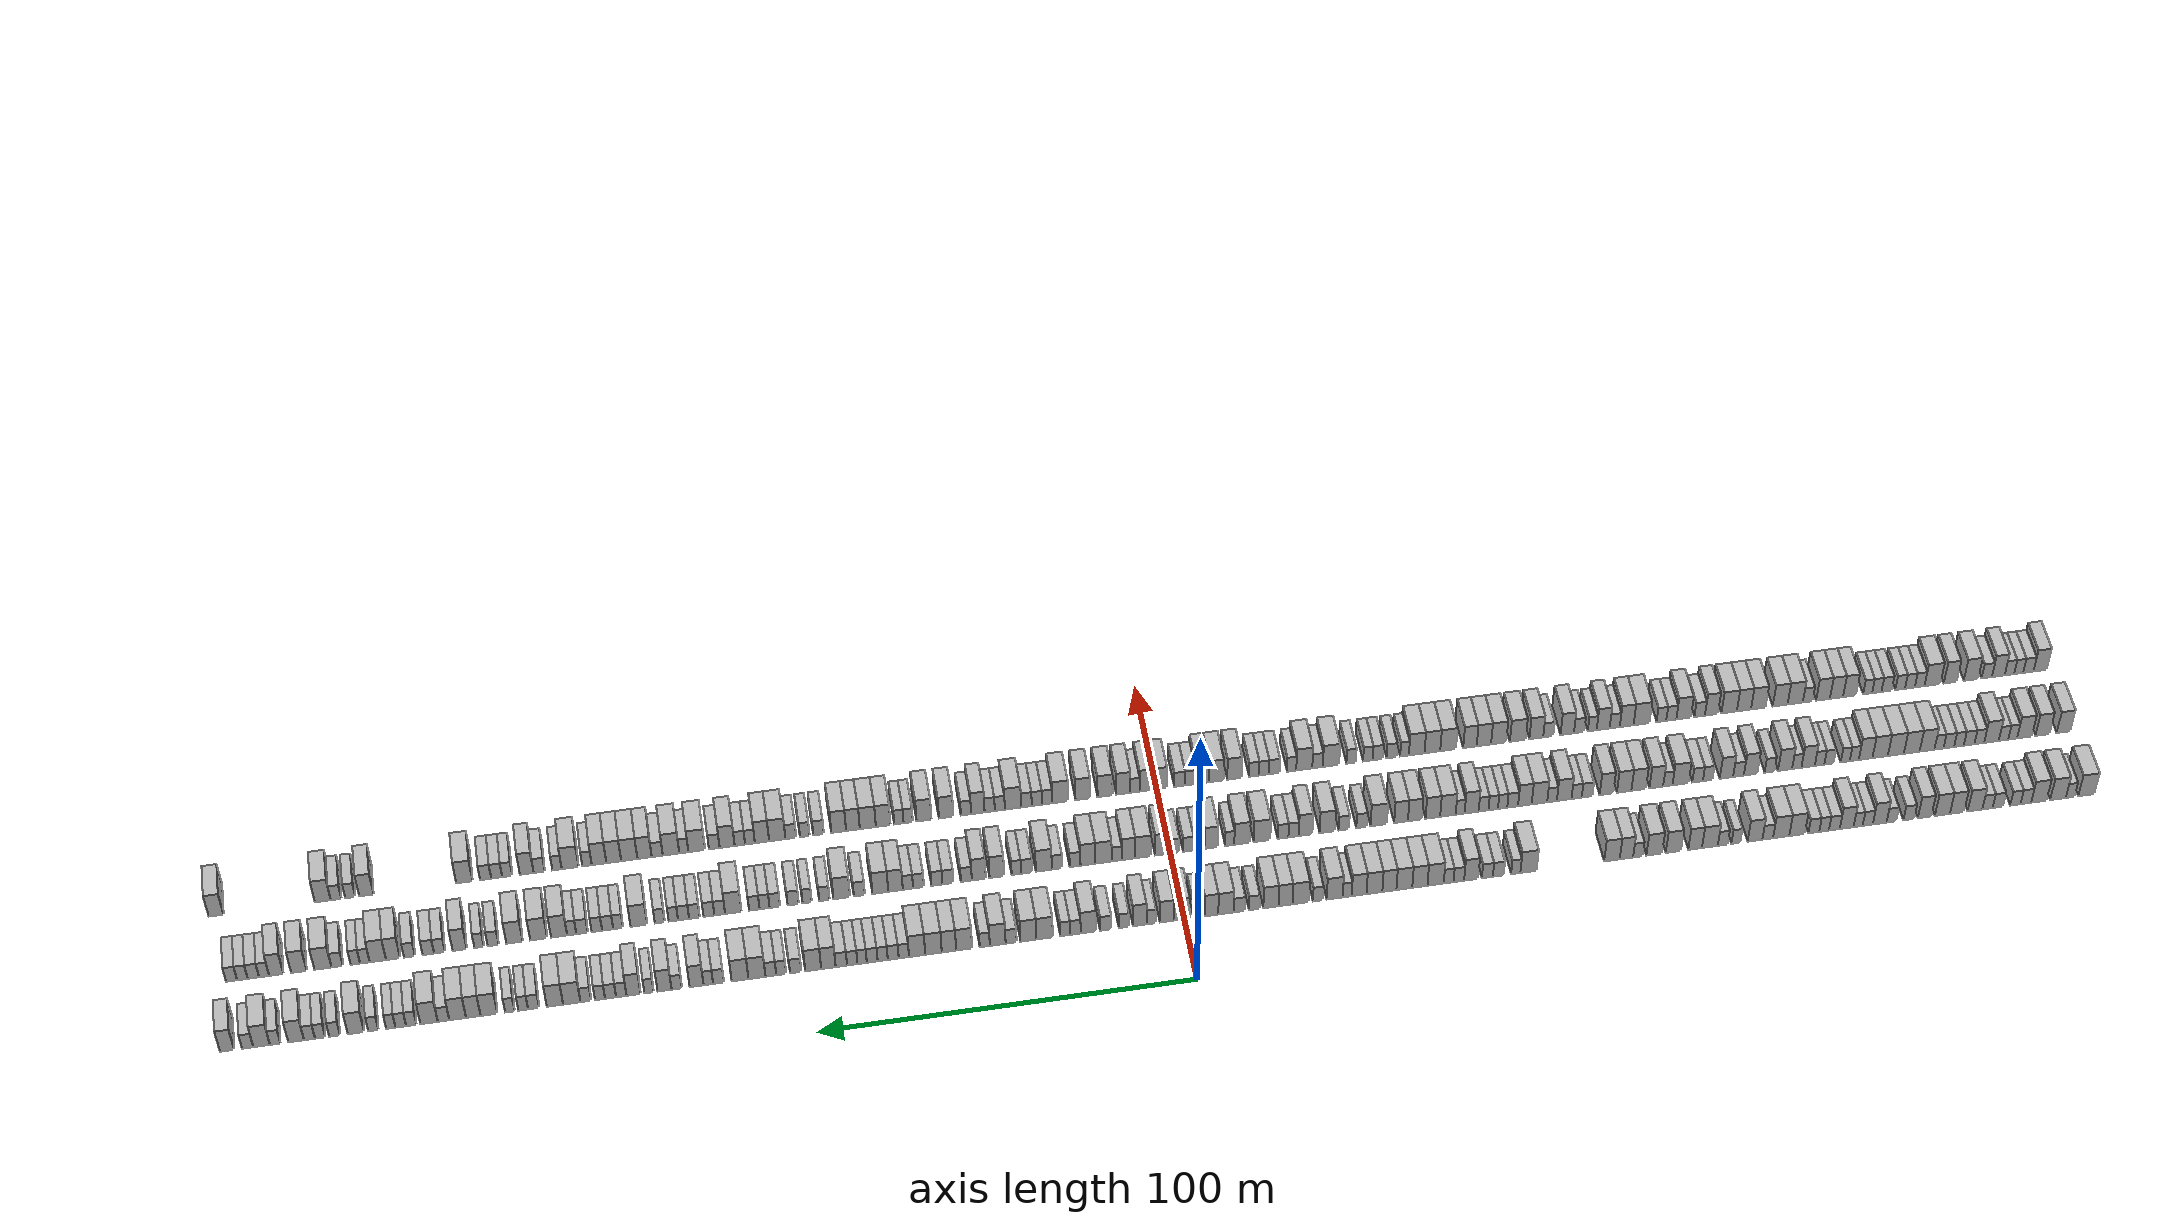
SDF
<sdf version="1.6">
 <world name="default">
  <scene>
   <sky><clouds><speed>12</speed></clouds></sky>
   <ambient>0.4 0.4 0.4 1</ambient>
   <background>0.7 0.7 0.7 1</background>
   <shadows>1</shadows>
  </scene>
  <gravity>0 0 -9.8066</gravity>
  <magnetic_field>6e-06 2.3e-05 -4.2e-05</magnetic_field>
  <physics default="0" name="default_physics" type="ode">
   <ode>
    <solver>
     <type>quick</type>
     <iters>10</iters>
     <sor>1.0</sor>
     <use_dynamic_moi_rescaling>0</use_dynamic_moi_rescaling>
    </solver>
    <constraints>
     <cfm>0</cfm>
     <erp>0.2</erp>
     <contact_max_correcting_vel>100</contact_max_correcting_vel>
     <contact_surface_layer>0.001</contact_surface_layer>
    </constraints>
   </ode>
   <max_step_size>0.004</max_step_size>
   <real_time_factor>1</real_time_factor>
   <real_time_update_rate>250</real_time_update_rate>
  </physics>
  <light name="sun" type="directional">
   <pose>0 0 10 0 0 0</pose>
   <diffuse>0.8 0.8 0.8 1</diffuse>
   <specular>0.2 0.2 0.2 1</specular>
   <attenuation>
    <range>1000</range>
    <constant>0.9</constant>
    <linear>0.01</linear>
    <quadratic>0.001</quadratic>
   </attenuation>
   <direction>-0.5 0.1 -0.9</direction>
  </light>
  <model name="building_1">
   <static>1</static>
   <pose>25.0000 -245.7570 0 0.000000 0.000000 0.000000</pose>
   <link name="link">
    <pose>0 0 4.50 0 0 0</pose>
    <collision name="collision"><geometry><box><size>10.0000 4.4859 9.0000</size></box></geometry></collision>
    <visual name="visual">
     <cast_shadows>0</cast_shadows>
     <geometry><box><size>10.0000 4.4859 9.0000</size></box></geometry>
     <material>
      <script>
       <uri>model://HANNAS_wall/materials/scripts</uri>
       <uri>model://HANNAS_wall/materials/textures</uri>
       <name>vrc/HANNAS_wall</name>
      </script>
     </material>
    </visual>
   </link>
  </model>
  <model name="building_2">
   <static>1</static>
   <pose>25.0000 -241.2803 0 0.000000 0.000000 0.000000</pose>
   <link name="link">
    <pose>0 0 3.00 0 0 0</pose>
    <collision name="collision"><geometry><box><size>10.0000 2.4675 6.0000</size></box></geometry></collision>
    <visual name="visual">
     <cast_shadows>0</cast_shadows>
     <geometry><box><size>10.0000 2.4675 6.0000</size></box></geometry>
     <material>
      <script>
       <uri>model://HANNAS_wall/materials/scripts</uri>
       <uri>model://HANNAS_wall/materials/textures</uri>
       <name>vrc/HANNAS_wall</name>
      </script>
     </material>
    </visual>
   </link>
  </model>
  <model name="building_3">
   <static>1</static>
   <pose>25.0000 -237.8687 0 0.000000 0.000000 0.000000</pose>
   <link name="link">
    <pose>0 0 4.50 0 0 0</pose>
    <collision name="collision"><geometry><box><size>10.0000 4.3557 9.0000</size></box></geometry></collision>
    <visual name="visual">
     <cast_shadows>0</cast_shadows>
     <geometry><box><size>10.0000 4.3557 9.0000</size></box></geometry>
     <material>
      <script>
       <uri>model://HANNAS_wall/materials/scripts</uri>
       <uri>model://HANNAS_wall/materials/textures</uri>
       <name>vrc/HANNAS_wall</name>
      </script>
     </material>
    </visual>
   </link>
  </model>
  <model name="building_4">
   <static>1</static>
   <pose>25.0000 -232.5526 0 0.000000 0.000000 0.000000</pose>
   <link name="link">
    <pose>0 0 4.50 0 0 0</pose>
    <collision name="collision"><geometry><box><size>10.0000 4.2767 9.0000</size></box></geometry></collision>
    <visual name="visual">
     <cast_shadows>0</cast_shadows>
     <geometry><box><size>10.0000 4.2767 9.0000</size></box></geometry>
     <material>
      <script>
       <uri>model://HANNAS_wall/materials/scripts</uri>
       <uri>model://HANNAS_wall/materials/textures</uri>
       <name>vrc/HANNAS_wall</name>
      </script>
     </material>
    </visual>
   </link>
  </model>
  <model name="building_5">
   <static>1</static>
   <pose>25.0000 -228.9279 0 0.000000 0.000000 0.000000</pose>
   <link name="link">
    <pose>0 0 3.00 0 0 0</pose>
    <collision name="collision"><geometry><box><size>10.0000 2.9727 6.0000</size></box></geometry></collision>
    <visual name="visual">
     <cast_shadows>0</cast_shadows>
     <geometry><box><size>10.0000 2.9727 6.0000</size></box></geometry>
     <material>
      <script>
       <uri>model://HANNAS_wall/materials/scripts</uri>
       <uri>model://HANNAS_wall/materials/textures</uri>
       <name>vrc/HANNAS_wall</name>
      </script>
     </material>
    </visual>
   </link>
  </model>
  <model name="building_6">
   <static>1</static>
   <pose>25.0000 -226.0034 0 0.000000 0.000000 0.000000</pose>
   <link name="link">
    <pose>0 0 3.00 0 0 0</pose>
    <collision name="collision"><geometry><box><size>10.0000 2.8763 6.0000</size></box></geometry></collision>
    <visual name="visual">
     <cast_shadows>0</cast_shadows>
     <geometry><box><size>10.0000 2.8763 6.0000</size></box></geometry>
     <material>
      <script>
       <uri>model://HANNAS_wall/materials/scripts</uri>
       <uri>model://HANNAS_wall/materials/textures</uri>
       <name>vrc/HANNAS_wall</name>
      </script>
     </material>
    </visual>
   </link>
  </model>
  <model name="building_7">
   <static>1</static>
   <pose>25.0000 -221.1476 0 0.000000 0.000000 0.000000</pose>
   <link name="link">
    <pose>0 0 3.00 0 0 0</pose>
    <collision name="collision"><geometry><box><size>10.0000 2.8353 6.0000</size></box></geometry></collision>
    <visual name="visual">
     <cast_shadows>0</cast_shadows>
     <geometry><box><size>10.0000 2.8353 6.0000</size></box></geometry>
     <material>
      <script>
       <uri>model://HANNAS_wall/materials/scripts</uri>
       <uri>model://HANNAS_wall/materials/textures</uri>
       <name>vrc/HANNAS_wall</name>
      </script>
     </material>
    </visual>
   </link>
  </model>
  <model name="building_8">
   <static>1</static>
   <pose>25.0000 -218.2944 0 0.000000 0.000000 0.000000</pose>
   <link name="link">
    <pose>0 0 3.00 0 0 0</pose>
    <collision name="collision"><geometry><box><size>10.0000 2.8711 6.0000</size></box></geometry></collision>
    <visual name="visual">
     <cast_shadows>0</cast_shadows>
     <geometry><box><size>10.0000 2.8711 6.0000</size></box></geometry>
     <material>
      <script>
       <uri>model://HANNAS_wall/materials/scripts</uri>
       <uri>model://HANNAS_wall/materials/textures</uri>
       <name>vrc/HANNAS_wall</name>
      </script>
     </material>
    </visual>
   </link>
  </model>
  <model name="building_9">
   <static>1</static>
   <pose>25.0000 -214.8184 0 0.000000 0.000000 0.000000</pose>
   <link name="link">
    <pose>0 0 4.50 0 0 0</pose>
    <collision name="collision"><geometry><box><size>10.0000 4.0810 9.0000</size></box></geometry></collision>
    <visual name="visual">
     <cast_shadows>0</cast_shadows>
     <geometry><box><size>10.0000 4.0810 9.0000</size></box></geometry>
     <material>
      <script>
       <uri>model://HANNAS_wall/materials/scripts</uri>
       <uri>model://HANNAS_wall/materials/textures</uri>
       <name>vrc/HANNAS_wall</name>
      </script>
     </material>
    </visual>
   </link>
  </model>
  <model name="building_10">
   <static>1</static>
   <pose>25.0000 -209.8260 0 0.000000 0.000000 0.000000</pose>
   <link name="link">
    <pose>0 0 4.50 0 0 0</pose>
    <collision name="collision"><geometry><box><size>10.0000 3.9037 9.0000</size></box></geometry></collision>
    <visual name="visual">
     <cast_shadows>0</cast_shadows>
     <geometry><box><size>10.0000 3.9037 9.0000</size></box></geometry>
     <material>
      <script>
       <uri>model://HANNAS_wall/materials/scripts</uri>
       <uri>model://HANNAS_wall/materials/textures</uri>
       <name>vrc/HANNAS_wall</name>
      </script>
     </material>
    </visual>
   </link>
  </model>
  <model name="building_11">
   <static>1</static>
   <pose>25.0000 -205.7910 0 0.000000 0.000000 0.000000</pose>
   <link name="link">
    <pose>0 0 4.50 0 0 0</pose>
    <collision name="collision"><geometry><box><size>10.0000 4.1664 9.0000</size></box></geometry></collision>
    <visual name="visual">
     <cast_shadows>0</cast_shadows>
     <geometry><box><size>10.0000 4.1664 9.0000</size></box></geometry>
     <material>
      <script>
       <uri>model://HANNAS_wall/materials/scripts</uri>
       <uri>model://HANNAS_wall/materials/textures</uri>
       <name>vrc/HANNAS_wall</name>
      </script>
     </material>
    </visual>
   </link>
  </model>
  <model name="building_12">
   <static>1</static>
   <pose>25.0000 -200.8387 0 0.000000 0.000000 0.000000</pose>
   <link name="link">
    <pose>0 0 4.50 0 0 0</pose>
    <collision name="collision"><geometry><box><size>10.0000 3.7381 9.0000</size></box></geometry></collision>
    <visual name="visual">
     <cast_shadows>0</cast_shadows>
     <geometry><box><size>10.0000 3.7381 9.0000</size></box></geometry>
     <material>
      <script>
       <uri>model://HANNAS_wall/materials/scripts</uri>
       <uri>model://HANNAS_wall/materials/textures</uri>
       <name>vrc/HANNAS_wall</name>
      </script>
     </material>
    </visual>
   </link>
  </model>
  <model name="building_13">
   <static>1</static>
   <pose>25.0000 -196.4818 0 0.000000 0.000000 0.000000</pose>
   <link name="link">
    <pose>0 0 3.00 0 0 0</pose>
    <collision name="collision"><geometry><box><size>10.0000 2.9758 6.0000</size></box></geometry></collision>
    <visual name="visual">
     <cast_shadows>0</cast_shadows>
     <geometry><box><size>10.0000 2.9758 6.0000</size></box></geometry>
     <material>
      <script>
       <uri>model://HANNAS_wall/materials/scripts</uri>
       <uri>model://HANNAS_wall/materials/textures</uri>
       <name>vrc/HANNAS_wall</name>
      </script>
     </material>
    </visual>
   </link>
  </model>
  <model name="building_14">
   <static>1</static>
   <pose>25.0000 -191.6625 0 0.000000 0.000000 0.000000</pose>
   <link name="link">
    <pose>0 0 3.00 0 0 0</pose>
    <collision name="collision"><geometry><box><size>10.0000 2.6628 6.0000</size></box></geometry></collision>
    <visual name="visual">
     <cast_shadows>0</cast_shadows>
     <geometry><box><size>10.0000 2.6628 6.0000</size></box></geometry>
     <material>
      <script>
       <uri>model://HANNAS_wall/materials/scripts</uri>
       <uri>model://HANNAS_wall/materials/textures</uri>
       <name>vrc/HANNAS_wall</name>
      </script>
     </material>
    </visual>
   </link>
  </model>
  <model name="building_15">
   <static>1</static>
   <pose>25.0000 -188.4330 0 0.000000 0.000000 0.000000</pose>
   <link name="link">
    <pose>0 0 4.50 0 0 0</pose>
    <collision name="collision"><geometry><box><size>10.0000 3.7962 9.0000</size></box></geometry></collision>
    <visual name="visual">
     <cast_shadows>0</cast_shadows>
     <geometry><box><size>10.0000 3.7962 9.0000</size></box></geometry>
     <material>
      <script>
       <uri>model://HANNAS_wall/materials/scripts</uri>
       <uri>model://HANNAS_wall/materials/textures</uri>
       <name>vrc/HANNAS_wall</name>
      </script>
     </material>
    </visual>
   </link>
  </model>
  <model name="building_16">
   <static>1</static>
   <pose>25.0000 -185.1406 0 0.000000 0.000000 0.000000</pose>
   <link name="link">
    <pose>0 0 3.00 0 0 0</pose>
    <collision name="collision"><geometry><box><size>10.0000 2.7887 6.0000</size></box></geometry></collision>
    <visual name="visual">
     <cast_shadows>0</cast_shadows>
     <geometry><box><size>10.0000 2.7887 6.0000</size></box></geometry>
     <material>
      <script>
       <uri>model://HANNAS_wall/materials/scripts</uri>
       <uri>model://HANNAS_wall/materials/textures</uri>
       <name>vrc/HANNAS_wall</name>
      </script>
     </material>
    </visual>
   </link>
  </model>
  <model name="building_17">
   <static>1</static>
   <pose>25.0000 -182.4966 0 0.000000 0.000000 0.000000</pose>
   <link name="link">
    <pose>0 0 3.00 0 0 0</pose>
    <collision name="collision"><geometry><box><size>10.0000 2.4991 6.0000</size></box></geometry></collision>
    <visual name="visual">
     <cast_shadows>0</cast_shadows>
     <geometry><box><size>10.0000 2.4991 6.0000</size></box></geometry>
     <material>
      <script>
       <uri>model://HANNAS_wall/materials/scripts</uri>
       <uri>model://HANNAS_wall/materials/textures</uri>
       <name>vrc/HANNAS_wall</name>
      </script>
     </material>
    </visual>
   </link>
  </model>
  <model name="building_18">
   <static>1</static>
   <pose>25.0000 -179.3472 0 0.000000 0.000000 0.000000</pose>
   <link name="link">
    <pose>0 0 4.50 0 0 0</pose>
    <collision name="collision"><geometry><box><size>10.0000 3.7998 9.0000</size></box></geometry></collision>
    <visual name="visual">
     <cast_shadows>0</cast_shadows>
     <geometry><box><size>10.0000 3.7998 9.0000</size></box></geometry>
     <material>
      <script>
       <uri>model://HANNAS_wall/materials/scripts</uri>
       <uri>model://HANNAS_wall/materials/textures</uri>
       <name>vrc/HANNAS_wall</name>
      </script>
     </material>
    </visual>
   </link>
  </model>
  <model name="building_19">
   <static>1</static>
   <pose>25.0000 -175.9523 0 0.000000 0.000000 0.000000</pose>
   <link name="link">
    <pose>0 0 3.00 0 0 0</pose>
    <collision name="collision"><geometry><box><size>10.0000 2.9900 6.0000</size></box></geometry></collision>
    <visual name="visual">
     <cast_shadows>0</cast_shadows>
     <geometry><box><size>10.0000 2.9900 6.0000</size></box></geometry>
     <material>
      <script>
       <uri>model://HANNAS_wall/materials/scripts</uri>
       <uri>model://HANNAS_wall/materials/textures</uri>
       <name>vrc/HANNAS_wall</name>
      </script>
     </material>
    </visual>
   </link>
  </model>
  <model name="building_20">
   <static>1</static>
   <pose>25.0000 -173.1057 0 0.000000 0.000000 0.000000</pose>
   <link name="link">
    <pose>0 0 3.00 0 0 0</pose>
    <collision name="collision"><geometry><box><size>10.0000 2.7034 6.0000</size></box></geometry></collision>
    <visual name="visual">
     <cast_shadows>0</cast_shadows>
     <geometry><box><size>10.0000 2.7034 6.0000</size></box></geometry>
     <material>
      <script>
       <uri>model://HANNAS_wall/materials/scripts</uri>
       <uri>model://HANNAS_wall/materials/textures</uri>
       <name>vrc/HANNAS_wall</name>
      </script>
     </material>
    </visual>
   </link>
  </model>
  <model name="building_21">
   <static>1</static>
   <pose>25.0000 -170.2709 0 0.000000 0.000000 0.000000</pose>
   <link name="link">
    <pose>0 0 3.00 0 0 0</pose>
    <collision name="collision"><geometry><box><size>10.0000 2.9663 6.0000</size></box></geometry></collision>
    <visual name="visual">
     <cast_shadows>0</cast_shadows>
     <geometry><box><size>10.0000 2.9663 6.0000</size></box></geometry>
     <material>
      <script>
       <uri>model://HANNAS_wall/materials/scripts</uri>
       <uri>model://HANNAS_wall/materials/textures</uri>
       <name>vrc/HANNAS_wall</name>
      </script>
     </material>
    </visual>
   </link>
  </model>
  <model name="building_22">
   <static>1</static>
   <pose>25.0000 -165.6557 0 0.000000 0.000000 0.000000</pose>
   <link name="link">
    <pose>0 0 4.50 0 0 0</pose>
    <collision name="collision"><geometry><box><size>10.0000 4.2640 9.0000</size></box></geometry></collision>
    <visual name="visual">
     <cast_shadows>0</cast_shadows>
     <geometry><box><size>10.0000 4.2640 9.0000</size></box></geometry>
     <material>
      <script>
       <uri>model://HANNAS_wall/materials/scripts</uri>
       <uri>model://HANNAS_wall/materials/textures</uri>
       <name>vrc/HANNAS_wall</name>
      </script>
     </material>
    </visual>
   </link>
  </model>
  <model name="building_23">
   <static>1</static>
   <pose>25.0000 -161.3009 0 0.000000 0.000000 0.000000</pose>
   <link name="link">
    <pose>0 0 4.50 0 0 0</pose>
    <collision name="collision"><geometry><box><size>10.0000 4.4455 9.0000</size></box></geometry></collision>
    <visual name="visual">
     <cast_shadows>0</cast_shadows>
     <geometry><box><size>10.0000 4.4455 9.0000</size></box></geometry>
     <material>
      <script>
       <uri>model://HANNAS_wall/materials/scripts</uri>
       <uri>model://HANNAS_wall/materials/textures</uri>
       <name>vrc/HANNAS_wall</name>
      </script>
     </material>
    </visual>
   </link>
  </model>
  <model name="building_24">
   <static>1</static>
   <pose>25.0000 -157.6015 0 0.000000 0.000000 0.000000</pose>
   <link name="link">
    <pose>0 0 3.00 0 0 0</pose>
    <collision name="collision"><geometry><box><size>10.0000 2.9533 6.0000</size></box></geometry></collision>
    <visual name="visual">
     <cast_shadows>0</cast_shadows>
     <geometry><box><size>10.0000 2.9533 6.0000</size></box></geometry>
     <material>
      <script>
       <uri>model://HANNAS_wall/materials/scripts</uri>
       <uri>model://HANNAS_wall/materials/textures</uri>
       <name>vrc/HANNAS_wall</name>
      </script>
     </material>
    </visual>
   </link>
  </model>
  <model name="building_25">
   <static>1</static>
   <pose>25.0000 -154.0993 0 0.000000 0.000000 0.000000</pose>
   <link name="link">
    <pose>0 0 4.50 0 0 0</pose>
    <collision name="collision"><geometry><box><size>10.0000 4.0511 9.0000</size></box></geometry></collision>
    <visual name="visual">
     <cast_shadows>0</cast_shadows>
     <geometry><box><size>10.0000 4.0511 9.0000</size></box></geometry>
     <material>
      <script>
       <uri>model://HANNAS_wall/materials/scripts</uri>
       <uri>model://HANNAS_wall/materials/textures</uri>
       <name>vrc/HANNAS_wall</name>
      </script>
     </material>
    </visual>
   </link>
  </model>
  <model name="building_26">
   <static>1</static>
   <pose>25.0000 -148.8517 0 0.000000 0.000000 0.000000</pose>
   <link name="link">
    <pose>0 0 3.00 0 0 0</pose>
    <collision name="collision"><geometry><box><size>10.0000 2.4440 6.0000</size></box></geometry></collision>
    <visual name="visual">
     <cast_shadows>0</cast_shadows>
     <geometry><box><size>10.0000 2.4440 6.0000</size></box></geometry>
     <material>
      <script>
       <uri>model://HANNAS_wall/materials/scripts</uri>
       <uri>model://HANNAS_wall/materials/textures</uri>
       <name>vrc/HANNAS_wall</name>
      </script>
     </material>
    </visual>
   </link>
  </model>
  <model name="building_27">
   <static>1</static>
   <pose>25.0000 -145.2663 0 0.000000 0.000000 0.000000</pose>
   <link name="link">
    <pose>0 0 3.00 0 0 0</pose>
    <collision name="collision"><geometry><box><size>10.0000 2.7268 6.0000</size></box></geometry></collision>
    <visual name="visual">
     <cast_shadows>0</cast_shadows>
     <geometry><box><size>10.0000 2.7268 6.0000</size></box></geometry>
     <material>
      <script>
       <uri>model://HANNAS_wall/materials/scripts</uri>
       <uri>model://HANNAS_wall/materials/textures</uri>
       <name>vrc/HANNAS_wall</name>
      </script>
     </material>
    </visual>
   </link>
  </model>
  <model name="building_28">
   <static>1</static>
   <pose>25.0000 -141.7348 0 0.000000 0.000000 0.000000</pose>
   <link name="link">
    <pose>0 0 4.50 0 0 0</pose>
    <collision name="collision"><geometry><box><size>10.0000 4.3362 9.0000</size></box></geometry></collision>
    <visual name="visual">
     <cast_shadows>0</cast_shadows>
     <geometry><box><size>10.0000 4.3362 9.0000</size></box></geometry>
     <material>
      <script>
       <uri>model://HANNAS_wall/materials/scripts</uri>
       <uri>model://HANNAS_wall/materials/textures</uri>
       <name>vrc/HANNAS_wall</name>
      </script>
     </material>
    </visual>
   </link>
  </model>
  <model name="building_29">
   <static>1</static>
   <pose>25.0000 -137.6974 0 0.000000 0.000000 0.000000</pose>
   <link name="link">
    <pose>0 0 4.50 0 0 0</pose>
    <collision name="collision"><geometry><box><size>10.0000 3.7385 9.0000</size></box></geometry></collision>
    <visual name="visual">
     <cast_shadows>0</cast_shadows>
     <geometry><box><size>10.0000 3.7385 9.0000</size></box></geometry>
     <material>
      <script>
       <uri>model://HANNAS_wall/materials/scripts</uri>
       <uri>model://HANNAS_wall/materials/textures</uri>
       <name>vrc/HANNAS_wall</name>
      </script>
     </material>
    </visual>
   </link>
  </model>
  <model name="building_30">
   <static>1</static>
   <pose>25.0000 -131.7441 0 0.000000 0.000000 0.000000</pose>
   <link name="link">
    <pose>0 0 4.50 0 0 0</pose>
    <collision name="collision"><geometry><box><size>10.0000 4.1682 9.0000</size></box></geometry></collision>
    <visual name="visual">
     <cast_shadows>0</cast_shadows>
     <geometry><box><size>10.0000 4.1682 9.0000</size></box></geometry>
     <material>
      <script>
       <uri>model://HANNAS_wall/materials/scripts</uri>
       <uri>model://HANNAS_wall/materials/textures</uri>
       <name>vrc/HANNAS_wall</name>
      </script>
     </material>
    </visual>
   </link>
  </model>
  <model name="building_31">
   <static>1</static>
   <pose>25.0000 -126.5214 0 0.000000 0.000000 0.000000</pose>
   <link name="link">
    <pose>0 0 4.50 0 0 0</pose>
    <collision name="collision"><geometry><box><size>10.0000 4.2772 9.0000</size></box></geometry></collision>
    <visual name="visual">
     <cast_shadows>0</cast_shadows>
     <geometry><box><size>10.0000 4.2772 9.0000</size></box></geometry>
     <material>
      <script>
       <uri>model://HANNAS_wall/materials/scripts</uri>
       <uri>model://HANNAS_wall/materials/textures</uri>
       <name>vrc/HANNAS_wall</name>
      </script>
     </material>
    </visual>
   </link>
  </model>
  <model name="building_32">
   <static>1</static>
   <pose>25.0000 -122.0662 0 0.000000 0.000000 0.000000</pose>
   <link name="link">
    <pose>0 0 3.00 0 0 0</pose>
    <collision name="collision"><geometry><box><size>10.0000 2.6332 6.0000</size></box></geometry></collision>
    <visual name="visual">
     <cast_shadows>0</cast_shadows>
     <geometry><box><size>10.0000 2.6332 6.0000</size></box></geometry>
     <material>
      <script>
       <uri>model://HANNAS_wall/materials/scripts</uri>
       <uri>model://HANNAS_wall/materials/textures</uri>
       <name>vrc/HANNAS_wall</name>
      </script>
     </material>
    </visual>
   </link>
  </model>
  <model name="building_33">
   <static>1</static>
   <pose>25.0000 -118.9241 0 0.000000 0.000000 0.000000</pose>
   <link name="link">
    <pose>0 0 4.50 0 0 0</pose>
    <collision name="collision"><geometry><box><size>10.0000 3.6510 9.0000</size></box></geometry></collision>
    <visual name="visual">
     <cast_shadows>0</cast_shadows>
     <geometry><box><size>10.0000 3.6510 9.0000</size></box></geometry>
     <material>
      <script>
       <uri>model://HANNAS_wall/materials/scripts</uri>
       <uri>model://HANNAS_wall/materials/textures</uri>
       <name>vrc/HANNAS_wall</name>
      </script>
     </material>
    </visual>
   </link>
  </model>
  <model name="building_34">
   <static>1</static>
   <pose>25.0000 -114.9840 0 0.000000 0.000000 0.000000</pose>
   <link name="link">
    <pose>0 0 4.50 0 0 0</pose>
    <collision name="collision"><geometry><box><size>10.0000 4.2292 9.0000</size></box></geometry></collision>
    <visual name="visual">
     <cast_shadows>0</cast_shadows>
     <geometry><box><size>10.0000 4.2292 9.0000</size></box></geometry>
     <material>
      <script>
       <uri>model://HANNAS_wall/materials/scripts</uri>
       <uri>model://HANNAS_wall/materials/textures</uri>
       <name>vrc/HANNAS_wall</name>
      </script>
     </material>
    </visual>
   </link>
  </model>
  <model name="building_35">
   <static>1</static>
   <pose>25.0000 -92.2837 0 0.000000 0.000000 0.000000</pose>
   <link name="link">
    <pose>0 0 4.50 0 0 0</pose>
    <collision name="collision"><geometry><box><size>10.0000 4.3905 9.0000</size></box></geometry></collision>
    <visual name="visual">
     <cast_shadows>0</cast_shadows>
     <geometry><box><size>10.0000 4.3905 9.0000</size></box></geometry>
     <material>
      <script>
       <uri>model://HANNAS_wall/materials/scripts</uri>
       <uri>model://HANNAS_wall/materials/textures</uri>
       <name>vrc/HANNAS_wall</name>
      </script>
     </material>
    </visual>
   </link>
  </model>
  <model name="building_36">
   <static>1</static>
   <pose>25.0000 -88.8265 0 0.000000 0.000000 0.000000</pose>
   <link name="link">
    <pose>0 0 3.00 0 0 0</pose>
    <collision name="collision"><geometry><box><size>10.0000 2.5239 6.0000</size></box></geometry></collision>
    <visual name="visual">
     <cast_shadows>0</cast_shadows>
     <geometry><box><size>10.0000 2.5239 6.0000</size></box></geometry>
     <material>
      <script>
       <uri>model://HANNAS_wall/materials/scripts</uri>
       <uri>model://HANNAS_wall/materials/textures</uri>
       <name>vrc/HANNAS_wall</name>
      </script>
     </material>
    </visual>
   </link>
  </model>
  <model name="building_37">
   <static>1</static>
   <pose>25.0000 -84.1011 0 0.000000 0.000000 0.000000</pose>
   <link name="link">
    <pose>0 0 3.00 0 0 0</pose>
    <collision name="collision"><geometry><box><size>10.0000 2.9268 6.0000</size></box></geometry></collision>
    <visual name="visual">
     <cast_shadows>0</cast_shadows>
     <geometry><box><size>10.0000 2.9268 6.0000</size></box></geometry>
     <material>
      <script>
       <uri>model://HANNAS_wall/materials/scripts</uri>
       <uri>model://HANNAS_wall/materials/textures</uri>
       <name>vrc/HANNAS_wall</name>
      </script>
     </material>
    </visual>
   </link>
  </model>
  <model name="building_38">
   <static>1</static>
   <pose>25.0000 -81.1424 0 0.000000 0.000000 0.000000</pose>
   <link name="link">
    <pose>0 0 3.00 0 0 0</pose>
    <collision name="collision"><geometry><box><size>10.0000 2.9907 6.0000</size></box></geometry></collision>
    <visual name="visual">
     <cast_shadows>0</cast_shadows>
     <geometry><box><size>10.0000 2.9907 6.0000</size></box></geometry>
     <material>
      <script>
       <uri>model://HANNAS_wall/materials/scripts</uri>
       <uri>model://HANNAS_wall/materials/textures</uri>
       <name>vrc/HANNAS_wall</name>
      </script>
     </material>
    </visual>
   </link>
  </model>
  <model name="building_39">
   <static>1</static>
   <pose>25.0000 -76.7437 0 0.000000 0.000000 0.000000</pose>
   <link name="link">
    <pose>0 0 4.50 0 0 0</pose>
    <collision name="collision"><geometry><box><size>10.0000 3.8066 9.0000</size></box></geometry></collision>
    <visual name="visual">
     <cast_shadows>0</cast_shadows>
     <geometry><box><size>10.0000 3.8066 9.0000</size></box></geometry>
     <material>
      <script>
       <uri>model://HANNAS_wall/materials/scripts</uri>
       <uri>model://HANNAS_wall/materials/textures</uri>
       <name>vrc/HANNAS_wall</name>
      </script>
     </material>
    </visual>
   </link>
  </model>
  <model name="building_40">
   <static>1</static>
   <pose>25.0000 -73.4082 0 0.000000 0.000000 0.000000</pose>
   <link name="link">
    <pose>0 0 3.00 0 0 0</pose>
    <collision name="collision"><geometry><box><size>10.0000 2.8644 6.0000</size></box></geometry></collision>
    <visual name="visual">
     <cast_shadows>0</cast_shadows>
     <geometry><box><size>10.0000 2.8644 6.0000</size></box></geometry>
     <material>
      <script>
       <uri>model://HANNAS_wall/materials/scripts</uri>
       <uri>model://HANNAS_wall/materials/textures</uri>
       <name>vrc/HANNAS_wall</name>
      </script>
     </material>
    </visual>
   </link>
  </model>
  <model name="building_41">
   <static>1</static>
   <pose>25.0000 -70.6567 0 0.000000 0.000000 0.000000</pose>
   <link name="link">
    <pose>0 0 3.00 0 0 0</pose>
    <collision name="collision"><geometry><box><size>10.0000 2.6385 6.0000</size></box></geometry></collision>
    <visual name="visual">
     <cast_shadows>0</cast_shadows>
     <geometry><box><size>10.0000 2.6385 6.0000</size></box></geometry>
     <material>
      <script>
       <uri>model://HANNAS_wall/materials/scripts</uri>
       <uri>model://HANNAS_wall/materials/textures</uri>
       <name>vrc/HANNAS_wall</name>
      </script>
     </material>
    </visual>
   </link>
  </model>
  <model name="building_42">
   <static>1</static>
   <pose>25.0000 -67.1344 0 0.000000 0.000000 0.000000</pose>
   <link name="link">
    <pose>0 0 4.50 0 0 0</pose>
    <collision name="collision"><geometry><box><size>10.0000 4.4061 9.0000</size></box></geometry></collision>
    <visual name="visual">
     <cast_shadows>0</cast_shadows>
     <geometry><box><size>10.0000 4.4061 9.0000</size></box></geometry>
     <material>
      <script>
       <uri>model://HANNAS_wall/materials/scripts</uri>
       <uri>model://HANNAS_wall/materials/textures</uri>
       <name>vrc/HANNAS_wall</name>
      </script>
     </material>
    </visual>
   </link>
  </model>
  <model name="building_43">
   <static>1</static>
   <pose>25.0000 -62.8742 0 0.000000 0.000000 0.000000</pose>
   <link name="link">
    <pose>0 0 4.50 0 0 0</pose>
    <collision name="collision"><geometry><box><size>10.0000 4.1144 9.0000</size></box></geometry></collision>
    <visual name="visual">
     <cast_shadows>0</cast_shadows>
     <geometry><box><size>10.0000 4.1144 9.0000</size></box></geometry>
     <material>
      <script>
       <uri>model://HANNAS_wall/materials/scripts</uri>
       <uri>model://HANNAS_wall/materials/textures</uri>
       <name>vrc/HANNAS_wall</name>
      </script>
     </material>
    </visual>
   </link>
  </model>
  <model name="building_44">
   <static>1</static>
   <pose>25.0000 -58.6829 0 0.000000 0.000000 0.000000</pose>
   <link name="link">
    <pose>0 0 4.50 0 0 0</pose>
    <collision name="collision"><geometry><box><size>10.0000 4.2681 9.0000</size></box></geometry></collision>
    <visual name="visual">
     <cast_shadows>0</cast_shadows>
     <geometry><box><size>10.0000 4.2681 9.0000</size></box></geometry>
     <material>
      <script>
       <uri>model://HANNAS_wall/materials/scripts</uri>
       <uri>model://HANNAS_wall/materials/textures</uri>
       <name>vrc/HANNAS_wall</name>
      </script>
     </material>
    </visual>
   </link>
  </model>
  <model name="building_45">
   <static>1</static>
   <pose>25.0000 -54.6478 0 0.000000 0.000000 0.000000</pose>
   <link name="link">
    <pose>0 0 4.50 0 0 0</pose>
    <collision name="collision"><geometry><box><size>10.0000 3.8021 9.0000</size></box></geometry></collision>
    <visual name="visual">
     <cast_shadows>0</cast_shadows>
     <geometry><box><size>10.0000 3.8021 9.0000</size></box></geometry>
     <material>
      <script>
       <uri>model://HANNAS_wall/materials/scripts</uri>
       <uri>model://HANNAS_wall/materials/textures</uri>
       <name>vrc/HANNAS_wall</name>
      </script>
     </material>
    </visual>
   </link>
  </model>
  <model name="building_46">
   <static>1</static>
   <pose>25.0000 -50.6157 0 0.000000 0.000000 0.000000</pose>
   <link name="link">
    <pose>0 0 4.50 0 0 0</pose>
    <collision name="collision"><geometry><box><size>10.0000 4.2620 9.0000</size></box></geometry></collision>
    <visual name="visual">
     <cast_shadows>0</cast_shadows>
     <geometry><box><size>10.0000 4.2620 9.0000</size></box></geometry>
     <material>
      <script>
       <uri>model://HANNAS_wall/materials/scripts</uri>
       <uri>model://HANNAS_wall/materials/textures</uri>
       <name>vrc/HANNAS_wall</name>
      </script>
     </material>
    </visual>
   </link>
  </model>
  <model name="building_47">
   <static>1</static>
   <pose>25.0000 -46.4929 0 0.000000 0.000000 0.000000</pose>
   <link name="link">
    <pose>0 0 4.50 0 0 0</pose>
    <collision name="collision"><geometry><box><size>10.0000 3.9836 9.0000</size></box></geometry></collision>
    <visual name="visual">
     <cast_shadows>0</cast_shadows>
     <geometry><box><size>10.0000 3.9836 9.0000</size></box></geometry>
     <material>
      <script>
       <uri>model://HANNAS_wall/materials/scripts</uri>
       <uri>model://HANNAS_wall/materials/textures</uri>
       <name>vrc/HANNAS_wall</name>
      </script>
     </material>
    </visual>
   </link>
  </model>
  <model name="building_48">
   <static>1</static>
   <pose>25.0000 -43.2947 0 0.000000 0.000000 0.000000</pose>
   <link name="link">
    <pose>0 0 3.00 0 0 0</pose>
    <collision name="collision"><geometry><box><size>10.0000 2.4129 6.0000</size></box></geometry></collision>
    <visual name="visual">
     <cast_shadows>0</cast_shadows>
     <geometry><box><size>10.0000 2.4129 6.0000</size></box></geometry>
     <material>
      <script>
       <uri>model://HANNAS_wall/materials/scripts</uri>
       <uri>model://HANNAS_wall/materials/textures</uri>
       <name>vrc/HANNAS_wall</name>
      </script>
     </material>
    </visual>
   </link>
  </model>
  <model name="building_49">
   <static>1</static>
   <pose>25.0000 -39.9360 0 0.000000 0.000000 0.000000</pose>
   <link name="link">
    <pose>0 0 4.50 0 0 0</pose>
    <collision name="collision"><geometry><box><size>10.0000 4.3044 9.0000</size></box></geometry></collision>
    <visual name="visual">
     <cast_shadows>0</cast_shadows>
     <geometry><box><size>10.0000 4.3044 9.0000</size></box></geometry>
     <material>
      <script>
       <uri>model://HANNAS_wall/materials/scripts</uri>
       <uri>model://HANNAS_wall/materials/textures</uri>
       <name>vrc/HANNAS_wall</name>
      </script>
     </material>
    </visual>
   </link>
  </model>
  <model name="building_50">
   <static>1</static>
   <pose>25.0000 -35.4360 0 0.000000 0.000000 0.000000</pose>
   <link name="link">
    <pose>0 0 3.00 0 0 0</pose>
    <collision name="collision"><geometry><box><size>10.0000 2.6955 6.0000</size></box></geometry></collision>
    <visual name="visual">
     <cast_shadows>0</cast_shadows>
     <geometry><box><size>10.0000 2.6955 6.0000</size></box></geometry>
     <material>
      <script>
       <uri>model://HANNAS_wall/materials/scripts</uri>
       <uri>model://HANNAS_wall/materials/textures</uri>
       <name>vrc/HANNAS_wall</name>
      </script>
     </material>
    </visual>
   </link>
  </model>
  <model name="building_51">
   <static>1</static>
   <pose>25.0000 -30.8599 0 0.000000 0.000000 0.000000</pose>
   <link name="link">
    <pose>0 0 4.50 0 0 0</pose>
    <collision name="collision"><geometry><box><size>10.0000 4.4568 9.0000</size></box></geometry></collision>
    <visual name="visual">
     <cast_shadows>0</cast_shadows>
     <geometry><box><size>10.0000 4.4568 9.0000</size></box></geometry>
     <material>
      <script>
       <uri>model://HANNAS_wall/materials/scripts</uri>
       <uri>model://HANNAS_wall/materials/textures</uri>
       <name>vrc/HANNAS_wall</name>
      </script>
     </material>
    </visual>
   </link>
  </model>
  <model name="building_52">
   <static>1</static>
   <pose>25.0000 -26.7289 0 0.000000 0.000000 0.000000</pose>
   <link name="link">
    <pose>0 0 4.50 0 0 0</pose>
    <collision name="collision"><geometry><box><size>10.0000 3.8052 9.0000</size></box></geometry></collision>
    <visual name="visual">
     <cast_shadows>0</cast_shadows>
     <geometry><box><size>10.0000 3.8052 9.0000</size></box></geometry>
     <material>
      <script>
       <uri>model://HANNAS_wall/materials/scripts</uri>
       <uri>model://HANNAS_wall/materials/textures</uri>
       <name>vrc/HANNAS_wall</name>
      </script>
     </material>
    </visual>
   </link>
  </model>
  <model name="building_53">
   <static>1</static>
   <pose>25.0000 -22.7991 0 0.000000 0.000000 0.000000</pose>
   <link name="link">
    <pose>0 0 4.50 0 0 0</pose>
    <collision name="collision"><geometry><box><size>10.0000 4.0543 9.0000</size></box></geometry></collision>
    <visual name="visual">
     <cast_shadows>0</cast_shadows>
     <geometry><box><size>10.0000 4.0543 9.0000</size></box></geometry>
     <material>
      <script>
       <uri>model://HANNAS_wall/materials/scripts</uri>
       <uri>model://HANNAS_wall/materials/textures</uri>
       <name>vrc/HANNAS_wall</name>
      </script>
     </material>
    </visual>
   </link>
  </model>
  <model name="building_54">
   <static>1</static>
   <pose>25.0000 -18.3393 0 0.000000 0.000000 0.000000</pose>
   <link name="link">
    <pose>0 0 3.00 0 0 0</pose>
    <collision name="collision"><geometry><box><size>10.0000 2.8654 6.0000</size></box></geometry></collision>
    <visual name="visual">
     <cast_shadows>0</cast_shadows>
     <geometry><box><size>10.0000 2.8654 6.0000</size></box></geometry>
     <material>
      <script>
       <uri>model://HANNAS_wall/materials/scripts</uri>
       <uri>model://HANNAS_wall/materials/textures</uri>
       <name>vrc/HANNAS_wall</name>
      </script>
     </material>
    </visual>
   </link>
  </model>
  <model name="building_55">
   <static>1</static>
   <pose>25.0000 -14.4096 0 0.000000 0.000000 0.000000</pose>
   <link name="link">
    <pose>0 0 3.00 0 0 0</pose>
    <collision name="collision"><geometry><box><size>10.0000 2.9939 6.0000</size></box></geometry></collision>
    <visual name="visual">
     <cast_shadows>0</cast_shadows>
     <geometry><box><size>10.0000 2.9939 6.0000</size></box></geometry>
     <material>
      <script>
       <uri>model://HANNAS_wall/materials/scripts</uri>
       <uri>model://HANNAS_wall/materials/textures</uri>
       <name>vrc/HANNAS_wall</name>
      </script>
     </material>
    </visual>
   </link>
  </model>
  <model name="building_56">
   <static>1</static>
   <pose>25.0000 -10.8188 0 0.000000 0.000000 0.000000</pose>
   <link name="link">
    <pose>0 0 4.50 0 0 0</pose>
    <collision name="collision"><geometry><box><size>10.0000 4.1877 9.0000</size></box></geometry></collision>
    <visual name="visual">
     <cast_shadows>0</cast_shadows>
     <geometry><box><size>10.0000 4.1877 9.0000</size></box></geometry>
     <material>
      <script>
       <uri>model://HANNAS_wall/materials/scripts</uri>
       <uri>model://HANNAS_wall/materials/textures</uri>
       <name>vrc/HANNAS_wall</name>
      </script>
     </material>
    </visual>
   </link>
  </model>
  <model name="building_57">
   <static>1</static>
   <pose>25.0000 -6.8836 0 0.000000 0.000000 0.000000</pose>
   <link name="link">
    <pose>0 0 4.50 0 0 0</pose>
    <collision name="collision"><geometry><box><size>10.0000 3.6826 9.0000</size></box></geometry></collision>
    <visual name="visual">
     <cast_shadows>0</cast_shadows>
     <geometry><box><size>10.0000 3.6826 9.0000</size></box></geometry>
     <material>
      <script>
       <uri>model://HANNAS_wall/materials/scripts</uri>
       <uri>model://HANNAS_wall/materials/textures</uri>
       <name>vrc/HANNAS_wall</name>
      </script>
     </material>
    </visual>
   </link>
  </model>
  <model name="building_58">
   <static>1</static>
   <pose>25.0000 -3.5515 0 0.000000 0.000000 0.000000</pose>
   <link name="link">
    <pose>0 0 3.00 0 0 0</pose>
    <collision name="collision"><geometry><box><size>10.0000 2.9817 6.0000</size></box></geometry></collision>
    <visual name="visual">
     <cast_shadows>0</cast_shadows>
     <geometry><box><size>10.0000 2.9817 6.0000</size></box></geometry>
     <material>
      <script>
       <uri>model://HANNAS_wall/materials/scripts</uri>
       <uri>model://HANNAS_wall/materials/textures</uri>
       <name>vrc/HANNAS_wall</name>
      </script>
     </material>
    </visual>
   </link>
  </model>
  <model name="building_59">
   <static>1</static>
   <pose>25.0000 1.0328 0 0.000000 0.000000 0.000000</pose>
   <link name="link">
    <pose>0 0 4.50 0 0 0</pose>
    <collision name="collision"><geometry><box><size>10.0000 4.1870 9.0000</size></box></geometry></collision>
    <visual name="visual">
     <cast_shadows>0</cast_shadows>
     <geometry><box><size>10.0000 4.1870 9.0000</size></box></geometry>
     <material>
      <script>
       <uri>model://HANNAS_wall/materials/scripts</uri>
       <uri>model://HANNAS_wall/materials/textures</uri>
       <name>vrc/HANNAS_wall</name>
      </script>
     </material>
    </visual>
   </link>
  </model>
  <model name="building_60">
   <static>1</static>
   <pose>25.0000 5.0197 0 0.000000 0.000000 0.000000</pose>
   <link name="link">
    <pose>0 0 4.50 0 0 0</pose>
    <collision name="collision"><geometry><box><size>10.0000 3.7867 9.0000</size></box></geometry></collision>
    <visual name="visual">
     <cast_shadows>0</cast_shadows>
     <geometry><box><size>10.0000 3.7867 9.0000</size></box></geometry>
     <material>
      <script>
       <uri>model://HANNAS_wall/materials/scripts</uri>
       <uri>model://HANNAS_wall/materials/textures</uri>
       <name>vrc/HANNAS_wall</name>
      </script>
     </material>
    </visual>
   </link>
  </model>
  <model name="building_61">
   <static>1</static>
   <pose>25.0000 9.1701 0 0.000000 0.000000 0.000000</pose>
   <link name="link">
    <pose>0 0 3.00 0 0 0</pose>
    <collision name="collision"><geometry><box><size>10.0000 2.5142 6.0000</size></box></geometry></collision>
    <visual name="visual">
     <cast_shadows>0</cast_shadows>
     <geometry><box><size>10.0000 2.5142 6.0000</size></box></geometry>
     <material>
      <script>
       <uri>model://HANNAS_wall/materials/scripts</uri>
       <uri>model://HANNAS_wall/materials/textures</uri>
       <name>vrc/HANNAS_wall</name>
      </script>
     </material>
    </visual>
   </link>
  </model>
  <model name="building_62">
   <static>1</static>
   <pose>25.0000 12.2522 0 0.000000 0.000000 0.000000</pose>
   <link name="link">
    <pose>0 0 4.50 0 0 0</pose>
    <collision name="collision"><geometry><box><size>10.0000 3.6499 9.0000</size></box></geometry></collision>
    <visual name="visual">
     <cast_shadows>0</cast_shadows>
     <geometry><box><size>10.0000 3.6499 9.0000</size></box></geometry>
     <material>
      <script>
       <uri>model://HANNAS_wall/materials/scripts</uri>
       <uri>model://HANNAS_wall/materials/textures</uri>
       <name>vrc/HANNAS_wall</name>
      </script>
     </material>
    </visual>
   </link>
  </model>
  <model name="building_63">
   <static>1</static>
   <pose>25.0000 16.4479 0 0.000000 0.000000 0.000000</pose>
   <link name="link">
    <pose>0 0 3.00 0 0 0</pose>
    <collision name="collision"><geometry><box><size>10.0000 2.7415 6.0000</size></box></geometry></collision>
    <visual name="visual">
     <cast_shadows>0</cast_shadows>
     <geometry><box><size>10.0000 2.7415 6.0000</size></box></geometry>
     <material>
      <script>
       <uri>model://HANNAS_wall/materials/scripts</uri>
       <uri>model://HANNAS_wall/materials/textures</uri>
       <name>vrc/HANNAS_wall</name>
      </script>
     </material>
    </visual>
   </link>
  </model>
  <model name="building_64">
   <static>1</static>
   <pose>25.0000 21.3149 0 0.000000 0.000000 0.000000</pose>
   <link name="link">
    <pose>0 0 3.00 0 0 0</pose>
    <collision name="collision"><geometry><box><size>10.0000 2.9923 6.0000</size></box></geometry></collision>
    <visual name="visual">
     <cast_shadows>0</cast_shadows>
     <geometry><box><size>10.0000 2.9923 6.0000</size></box></geometry>
     <material>
      <script>
       <uri>model://HANNAS_wall/materials/scripts</uri>
       <uri>model://HANNAS_wall/materials/textures</uri>
       <name>vrc/HANNAS_wall</name>
      </script>
     </material>
    </visual>
   </link>
  </model>
  <model name="building_65">
   <static>1</static>
   <pose>25.0000 25.8842 0 0.000000 0.000000 0.000000</pose>
   <link name="link">
    <pose>0 0 4.50 0 0 0</pose>
    <collision name="collision"><geometry><box><size>10.0000 4.1463 9.0000</size></box></geometry></collision>
    <visual name="visual">
     <cast_shadows>0</cast_shadows>
     <geometry><box><size>10.0000 4.1463 9.0000</size></box></geometry>
     <material>
      <script>
       <uri>model://HANNAS_wall/materials/scripts</uri>
       <uri>model://HANNAS_wall/materials/textures</uri>
       <name>vrc/HANNAS_wall</name>
      </script>
     </material>
    </visual>
   </link>
  </model>
  <model name="building_66">
   <static>1</static>
   <pose>25.0000 29.3774 0 0.000000 0.000000 0.000000</pose>
   <link name="link">
    <pose>0 0 3.00 0 0 0</pose>
    <collision name="collision"><geometry><box><size>10.0000 2.8401 6.0000</size></box></geometry></collision>
    <visual name="visual">
     <cast_shadows>0</cast_shadows>
     <geometry><box><size>10.0000 2.8401 6.0000</size></box></geometry>
     <material>
      <script>
       <uri>model://HANNAS_wall/materials/scripts</uri>
       <uri>model://HANNAS_wall/materials/textures</uri>
       <name>vrc/HANNAS_wall</name>
      </script>
     </material>
    </visual>
   </link>
  </model>
  <model name="building_67">
   <static>1</static>
   <pose>25.0000 32.0811 0 0.000000 0.000000 0.000000</pose>
   <link name="link">
    <pose>0 0 3.00 0 0 0</pose>
    <collision name="collision"><geometry><box><size>10.0000 2.5674 6.0000</size></box></geometry></collision>
    <visual name="visual">
     <cast_shadows>0</cast_shadows>
     <geometry><box><size>10.0000 2.5674 6.0000</size></box></geometry>
     <material>
      <script>
       <uri>model://HANNAS_wall/materials/scripts</uri>
       <uri>model://HANNAS_wall/materials/textures</uri>
       <name>vrc/HANNAS_wall</name>
      </script>
     </material>
    </visual>
   </link>
  </model>
  <model name="building_68">
   <static>1</static>
   <pose>25.0000 37.5372 0 0.000000 0.000000 0.000000</pose>
   <link name="link">
    <pose>0 0 4.50 0 0 0</pose>
    <collision name="collision"><geometry><box><size>10.0000 4.3449 9.0000</size></box></geometry></collision>
    <visual name="visual">
     <cast_shadows>0</cast_shadows>
     <geometry><box><size>10.0000 4.3449 9.0000</size></box></geometry>
     <material>
      <script>
       <uri>model://HANNAS_wall/materials/scripts</uri>
       <uri>model://HANNAS_wall/materials/textures</uri>
       <name>vrc/HANNAS_wall</name>
      </script>
     </material>
    </visual>
   </link>
  </model>
  <model name="building_69">
   <static>1</static>
   <pose>25.0000 41.8256 0 0.000000 0.000000 0.000000</pose>
   <link name="link">
    <pose>0 0 4.50 0 0 0</pose>
    <collision name="collision"><geometry><box><size>10.0000 4.2319 9.0000</size></box></geometry></collision>
    <visual name="visual">
     <cast_shadows>0</cast_shadows>
     <geometry><box><size>10.0000 4.2319 9.0000</size></box></geometry>
     <material>
      <script>
       <uri>model://HANNAS_wall/materials/scripts</uri>
       <uri>model://HANNAS_wall/materials/textures</uri>
       <name>vrc/HANNAS_wall</name>
      </script>
     </material>
    </visual>
   </link>
  </model>
  <model name="building_70">
   <static>1</static>
   <pose>25.0000 46.4046 0 0.000000 0.000000 0.000000</pose>
   <link name="link">
    <pose>0 0 3.00 0 0 0</pose>
    <collision name="collision"><geometry><box><size>10.0000 2.9260 6.0000</size></box></geometry></collision>
    <visual name="visual">
     <cast_shadows>0</cast_shadows>
     <geometry><box><size>10.0000 2.9260 6.0000</size></box></geometry>
     <material>
      <script>
       <uri>model://HANNAS_wall/materials/scripts</uri>
       <uri>model://HANNAS_wall/materials/textures</uri>
       <name>vrc/HANNAS_wall</name>
      </script>
     </material>
    </visual>
   </link>
  </model>
  <model name="building_71">
   <static>1</static>
   <pose>25.0000 49.9633 0 0.000000 0.000000 0.000000</pose>
   <link name="link">
    <pose>0 0 4.50 0 0 0</pose>
    <collision name="collision"><geometry><box><size>10.0000 4.1914 9.0000</size></box></geometry></collision>
    <visual name="visual">
     <cast_shadows>0</cast_shadows>
     <geometry><box><size>10.0000 4.1914 9.0000</size></box></geometry>
     <material>
      <script>
       <uri>model://HANNAS_wall/materials/scripts</uri>
       <uri>model://HANNAS_wall/materials/textures</uri>
       <name>vrc/HANNAS_wall</name>
      </script>
     </material>
    </visual>
   </link>
  </model>
  <model name="building_72">
   <static>1</static>
   <pose>25.0000 53.3934 0 0.000000 0.000000 0.000000</pose>
   <link name="link">
    <pose>0 0 3.00 0 0 0</pose>
    <collision name="collision"><geometry><box><size>10.0000 2.6688 6.0000</size></box></geometry></collision>
    <visual name="visual">
     <cast_shadows>0</cast_shadows>
     <geometry><box><size>10.0000 2.6688 6.0000</size></box></geometry>
     <material>
      <script>
       <uri>model://HANNAS_wall/materials/scripts</uri>
       <uri>model://HANNAS_wall/materials/textures</uri>
       <name>vrc/HANNAS_wall</name>
      </script>
     </material>
    </visual>
   </link>
  </model>
  <model name="building_73">
   <static>1</static>
   <pose>25.0000 58.8330 0 0.000000 0.000000 0.000000</pose>
   <link name="link">
    <pose>0 0 4.50 0 0 0</pose>
    <collision name="collision"><geometry><box><size>10.0000 4.2104 9.0000</size></box></geometry></collision>
    <visual name="visual">
     <cast_shadows>0</cast_shadows>
     <geometry><box><size>10.0000 4.2104 9.0000</size></box></geometry>
     <material>
      <script>
       <uri>model://HANNAS_wall/materials/scripts</uri>
       <uri>model://HANNAS_wall/materials/textures</uri>
       <name>vrc/HANNAS_wall</name>
      </script>
     </material>
    </visual>
   </link>
  </model>
  <model name="building_74">
   <static>1</static>
   <pose>25.0000 62.8414 0 0.000000 0.000000 0.000000</pose>
   <link name="link">
    <pose>0 0 4.50 0 0 0</pose>
    <collision name="collision"><geometry><box><size>10.0000 3.8063 9.0000</size></box></geometry></collision>
    <visual name="visual">
     <cast_shadows>0</cast_shadows>
     <geometry><box><size>10.0000 3.8063 9.0000</size></box></geometry>
     <material>
      <script>
       <uri>model://HANNAS_wall/materials/scripts</uri>
       <uri>model://HANNAS_wall/materials/textures</uri>
       <name>vrc/HANNAS_wall</name>
      </script>
     </material>
    </visual>
   </link>
  </model>
  <model name="building_75">
   <static>1</static>
   <pose>25.0000 66.9315 0 0.000000 0.000000 0.000000</pose>
   <link name="link">
    <pose>0 0 4.50 0 0 0</pose>
    <collision name="collision"><geometry><box><size>10.0000 4.3739 9.0000</size></box></geometry></collision>
    <visual name="visual">
     <cast_shadows>0</cast_shadows>
     <geometry><box><size>10.0000 4.3739 9.0000</size></box></geometry>
     <material>
      <script>
       <uri>model://HANNAS_wall/materials/scripts</uri>
       <uri>model://HANNAS_wall/materials/textures</uri>
       <name>vrc/HANNAS_wall</name>
      </script>
     </material>
    </visual>
   </link>
  </model>
  <model name="building_76">
   <static>1</static>
   <pose>25.0000 71.2553 0 0.000000 0.000000 0.000000</pose>
   <link name="link">
    <pose>0 0 4.50 0 0 0</pose>
    <collision name="collision"><geometry><box><size>10.0000 4.2737 9.0000</size></box></geometry></collision>
    <visual name="visual">
     <cast_shadows>0</cast_shadows>
     <geometry><box><size>10.0000 4.2737 9.0000</size></box></geometry>
     <material>
      <script>
       <uri>model://HANNAS_wall/materials/scripts</uri>
       <uri>model://HANNAS_wall/materials/textures</uri>
       <name>vrc/HANNAS_wall</name>
      </script>
     </material>
    </visual>
   </link>
  </model>
  <model name="building_77">
   <static>1</static>
   <pose>25.0000 74.7431 0 0.000000 0.000000 0.000000</pose>
   <link name="link">
    <pose>0 0 3.00 0 0 0</pose>
    <collision name="collision"><geometry><box><size>10.0000 2.7020 6.0000</size></box></geometry></collision>
    <visual name="visual">
     <cast_shadows>0</cast_shadows>
     <geometry><box><size>10.0000 2.7020 6.0000</size></box></geometry>
     <material>
      <script>
       <uri>model://HANNAS_wall/materials/scripts</uri>
       <uri>model://HANNAS_wall/materials/textures</uri>
       <name>vrc/HANNAS_wall</name>
      </script>
     </material>
    </visual>
   </link>
  </model>
  <model name="building_78">
   <static>1</static>
   <pose>25.0000 77.5304 0 0.000000 0.000000 0.000000</pose>
   <link name="link">
    <pose>0 0 3.00 0 0 0</pose>
    <collision name="collision"><geometry><box><size>10.0000 2.8726 6.0000</size></box></geometry></collision>
    <visual name="visual">
     <cast_shadows>0</cast_shadows>
     <geometry><box><size>10.0000 2.8726 6.0000</size></box></geometry>
     <material>
      <script>
       <uri>model://HANNAS_wall/materials/scripts</uri>
       <uri>model://HANNAS_wall/materials/textures</uri>
       <name>vrc/HANNAS_wall</name>
      </script>
     </material>
    </visual>
   </link>
  </model>
  <model name="building_79">
   <static>1</static>
   <pose>25.0000 80.3049 0 0.000000 0.000000 0.000000</pose>
   <link name="link">
    <pose>0 0 3.00 0 0 0</pose>
    <collision name="collision"><geometry><box><size>10.0000 2.6762 6.0000</size></box></geometry></collision>
    <visual name="visual">
     <cast_shadows>0</cast_shadows>
     <geometry><box><size>10.0000 2.6762 6.0000</size></box></geometry>
     <material>
      <script>
       <uri>model://HANNAS_wall/materials/scripts</uri>
       <uri>model://HANNAS_wall/materials/textures</uri>
       <name>vrc/HANNAS_wall</name>
      </script>
     </material>
    </visual>
   </link>
  </model>
  <model name="building_80">
   <static>1</static>
   <pose>25.0000 83.0721 0 0.000000 0.000000 0.000000</pose>
   <link name="link">
    <pose>0 0 3.00 0 0 0</pose>
    <collision name="collision"><geometry><box><size>10.0000 2.8583 6.0000</size></box></geometry></collision>
    <visual name="visual">
     <cast_shadows>0</cast_shadows>
     <geometry><box><size>10.0000 2.8583 6.0000</size></box></geometry>
     <material>
      <script>
       <uri>model://HANNAS_wall/materials/scripts</uri>
       <uri>model://HANNAS_wall/materials/textures</uri>
       <name>vrc/HANNAS_wall</name>
      </script>
     </material>
    </visual>
   </link>
  </model>
  <model name="building_81">
   <static>1</static>
   <pose>25.0000 85.7258 0 0.000000 0.000000 0.000000</pose>
   <link name="link">
    <pose>0 0 3.00 0 0 0</pose>
    <collision name="collision"><geometry><box><size>10.0000 2.4491 6.0000</size></box></geometry></collision>
    <visual name="visual">
     <cast_shadows>0</cast_shadows>
     <geometry><box><size>10.0000 2.4491 6.0000</size></box></geometry>
     <material>
      <script>
       <uri>model://HANNAS_wall/materials/scripts</uri>
       <uri>model://HANNAS_wall/materials/textures</uri>
       <name>vrc/HANNAS_wall</name>
      </script>
     </material>
    </visual>
   </link>
  </model>
  <model name="building_82">
   <static>1</static>
   <pose>25.0000 88.3203 0 0.000000 0.000000 0.000000</pose>
   <link name="link">
    <pose>0 0 3.00 0 0 0</pose>
    <collision name="collision"><geometry><box><size>10.0000 2.7400 6.0000</size></box></geometry></collision>
    <visual name="visual">
     <cast_shadows>0</cast_shadows>
     <geometry><box><size>10.0000 2.7400 6.0000</size></box></geometry>
     <material>
      <script>
       <uri>model://HANNAS_wall/materials/scripts</uri>
       <uri>model://HANNAS_wall/materials/textures</uri>
       <name>vrc/HANNAS_wall</name>
      </script>
     </material>
    </visual>
   </link>
  </model>
  <model name="building_83">
   <static>1</static>
   <pose>25.0000 91.1798 0 0.000000 0.000000 0.000000</pose>
   <link name="link">
    <pose>0 0 3.00 0 0 0</pose>
    <collision name="collision"><geometry><box><size>10.0000 2.9789 6.0000</size></box></geometry></collision>
    <visual name="visual">
     <cast_shadows>0</cast_shadows>
     <geometry><box><size>10.0000 2.9789 6.0000</size></box></geometry>
     <material>
      <script>
       <uri>model://HANNAS_wall/materials/scripts</uri>
       <uri>model://HANNAS_wall/materials/textures</uri>
       <name>vrc/HANNAS_wall</name>
      </script>
     </material>
    </visual>
   </link>
  </model>
  <model name="building_84">
   <static>1</static>
   <pose>25.0000 94.5702 0 0.000000 0.000000 0.000000</pose>
   <link name="link">
    <pose>0 0 4.50 0 0 0</pose>
    <collision name="collision"><geometry><box><size>10.0000 3.8020 9.0000</size></box></geometry></collision>
    <visual name="visual">
     <cast_shadows>0</cast_shadows>
     <geometry><box><size>10.0000 3.8020 9.0000</size></box></geometry>
     <material>
      <script>
       <uri>model://HANNAS_wall/materials/scripts</uri>
       <uri>model://HANNAS_wall/materials/textures</uri>
       <name>vrc/HANNAS_wall</name>
      </script>
     </material>
    </visual>
   </link>
  </model>
  <model name="building_85">
   <static>1</static>
   <pose>25.0000 98.5668 0 0.000000 0.000000 0.000000</pose>
   <link name="link">
    <pose>0 0 4.50 0 0 0</pose>
    <collision name="collision"><geometry><box><size>10.0000 4.1911 9.0000</size></box></geometry></collision>
    <visual name="visual">
     <cast_shadows>0</cast_shadows>
     <geometry><box><size>10.0000 4.1911 9.0000</size></box></geometry>
     <material>
      <script>
       <uri>model://HANNAS_wall/materials/scripts</uri>
       <uri>model://HANNAS_wall/materials/textures</uri>
       <name>vrc/HANNAS_wall</name>
      </script>
     </material>
    </visual>
   </link>
  </model>
  <model name="building_86">
   <static>1</static>
   <pose>25.0000 103.1557 0 0.000000 0.000000 0.000000</pose>
   <link name="link">
    <pose>0 0 3.00 0 0 0</pose>
    <collision name="collision"><geometry><box><size>10.0000 2.9868 6.0000</size></box></geometry></collision>
    <visual name="visual">
     <cast_shadows>0</cast_shadows>
     <geometry><box><size>10.0000 2.9868 6.0000</size></box></geometry>
     <material>
      <script>
       <uri>model://HANNAS_wall/materials/scripts</uri>
       <uri>model://HANNAS_wall/materials/textures</uri>
       <name>vrc/HANNAS_wall</name>
      </script>
     </material>
    </visual>
   </link>
  </model>
  <model name="building_87">
   <static>1</static>
   <pose>25.0000 106.9450 0 0.000000 0.000000 0.000000</pose>
   <link name="link">
    <pose>0 0 3.00 0 0 0</pose>
    <collision name="collision"><geometry><box><size>10.0000 2.5917 6.0000</size></box></geometry></collision>
    <visual name="visual">
     <cast_shadows>0</cast_shadows>
     <geometry><box><size>10.0000 2.5917 6.0000</size></box></geometry>
     <material>
      <script>
       <uri>model://HANNAS_wall/materials/scripts</uri>
       <uri>model://HANNAS_wall/materials/textures</uri>
       <name>vrc/HANNAS_wall</name>
      </script>
     </material>
    </visual>
   </link>
  </model>
  <model name="building_88">
   <static>1</static>
   <pose>25.0000 109.6598 0 0.000000 0.000000 0.000000</pose>
   <link name="link">
    <pose>0 0 3.00 0 0 0</pose>
    <collision name="collision"><geometry><box><size>10.0000 2.8379 6.0000</size></box></geometry></collision>
    <visual name="visual">
     <cast_shadows>0</cast_shadows>
     <geometry><box><size>10.0000 2.8379 6.0000</size></box></geometry>
     <material>
      <script>
       <uri>model://HANNAS_wall/materials/scripts</uri>
       <uri>model://HANNAS_wall/materials/textures</uri>
       <name>vrc/HANNAS_wall</name>
      </script>
     </material>
    </visual>
   </link>
  </model>
  <model name="building_89">
   <static>1</static>
   <pose>25.0000 113.3002 0 0.000000 0.000000 0.000000</pose>
   <link name="link">
    <pose>0 0 4.50 0 0 0</pose>
    <collision name="collision"><geometry><box><size>10.0000 4.4428 9.0000</size></box></geometry></collision>
    <visual name="visual">
     <cast_shadows>0</cast_shadows>
     <geometry><box><size>10.0000 4.4428 9.0000</size></box></geometry>
     <material>
      <script>
       <uri>model://HANNAS_wall/materials/scripts</uri>
       <uri>model://HANNAS_wall/materials/textures</uri>
       <name>vrc/HANNAS_wall</name>
      </script>
     </material>
    </visual>
   </link>
  </model>
  <model name="building_90">
   <static>1</static>
   <pose>25.0000 117.7229 0 0.000000 0.000000 0.000000</pose>
   <link name="link">
    <pose>0 0 4.50 0 0 0</pose>
    <collision name="collision"><geometry><box><size>10.0000 4.4026 9.0000</size></box></geometry></collision>
    <visual name="visual">
     <cast_shadows>0</cast_shadows>
     <geometry><box><size>10.0000 4.4026 9.0000</size></box></geometry>
     <material>
      <script>
       <uri>model://HANNAS_wall/materials/scripts</uri>
       <uri>model://HANNAS_wall/materials/textures</uri>
       <name>vrc/HANNAS_wall</name>
      </script>
     </material>
    </visual>
   </link>
  </model>
  <model name="building_91">
   <static>1</static>
   <pose>25.0000 123.3410 0 0.000000 0.000000 0.000000</pose>
   <link name="link">
    <pose>0 0 3.00 0 0 0</pose>
    <collision name="collision"><geometry><box><size>10.0000 2.8338 6.0000</size></box></geometry></collision>
    <visual name="visual">
     <cast_shadows>0</cast_shadows>
     <geometry><box><size>10.0000 2.8338 6.0000</size></box></geometry>
     <material>
      <script>
       <uri>model://HANNAS_wall/materials/scripts</uri>
       <uri>model://HANNAS_wall/materials/textures</uri>
       <name>vrc/HANNAS_wall</name>
      </script>
     </material>
    </visual>
   </link>
  </model>
  <model name="building_92">
   <static>1</static>
   <pose>25.0000 125.9949 0 0.000000 0.000000 0.000000</pose>
   <link name="link">
    <pose>0 0 3.00 0 0 0</pose>
    <collision name="collision"><geometry><box><size>10.0000 2.4739 6.0000</size></box></geometry></collision>
    <visual name="visual">
     <cast_shadows>0</cast_shadows>
     <geometry><box><size>10.0000 2.4739 6.0000</size></box></geometry>
     <material>
      <script>
       <uri>model://HANNAS_wall/materials/scripts</uri>
       <uri>model://HANNAS_wall/materials/textures</uri>
       <name>vrc/HANNAS_wall</name>
      </script>
     </material>
    </visual>
   </link>
  </model>
  <model name="building_93">
   <static>1</static>
   <pose>25.0000 129.0610 0 0.000000 0.000000 0.000000</pose>
   <link name="link">
    <pose>0 0 4.50 0 0 0</pose>
    <collision name="collision"><geometry><box><size>10.0000 3.6583 9.0000</size></box></geometry></collision>
    <visual name="visual">
     <cast_shadows>0</cast_shadows>
     <geometry><box><size>10.0000 3.6583 9.0000</size></box></geometry>
     <material>
      <script>
       <uri>model://HANNAS_wall/materials/scripts</uri>
       <uri>model://HANNAS_wall/materials/textures</uri>
       <name>vrc/HANNAS_wall</name>
      </script>
     </material>
    </visual>
   </link>
  </model>
  <model name="building_94">
   <static>1</static>
   <pose>25.0000 134.2347 0 0.000000 0.000000 0.000000</pose>
   <link name="link">
    <pose>0 0 3.00 0 0 0</pose>
    <collision name="collision"><geometry><box><size>10.0000 2.6890 6.0000</size></box></geometry></collision>
    <visual name="visual">
     <cast_shadows>0</cast_shadows>
     <geometry><box><size>10.0000 2.6890 6.0000</size></box></geometry>
     <material>
      <script>
       <uri>model://HANNAS_wall/materials/scripts</uri>
       <uri>model://HANNAS_wall/materials/textures</uri>
       <name>vrc/HANNAS_wall</name>
      </script>
     </material>
    </visual>
   </link>
  </model>
  <model name="building_95">
   <static>1</static>
   <pose>25.0000 137.4151 0 0.000000 0.000000 0.000000</pose>
   <link name="link">
    <pose>0 0 4.50 0 0 0</pose>
    <collision name="collision"><geometry><box><size>10.0000 3.6720 9.0000</size></box></geometry></collision>
    <visual name="visual">
     <cast_shadows>0</cast_shadows>
     <geometry><box><size>10.0000 3.6720 9.0000</size></box></geometry>
     <material>
      <script>
       <uri>model://HANNAS_wall/materials/scripts</uri>
       <uri>model://HANNAS_wall/materials/textures</uri>
       <name>vrc/HANNAS_wall</name>
      </script>
     </material>
    </visual>
   </link>
  </model>
  <model name="building_96">
   <static>1</static>
   <pose>25.0000 141.4545 0 0.000000 0.000000 0.000000</pose>
   <link name="link">
    <pose>0 0 3.00 0 0 0</pose>
    <collision name="collision"><geometry><box><size>10.0000 2.4067 6.0000</size></box></geometry></collision>
    <visual name="visual">
     <cast_shadows>0</cast_shadows>
     <geometry><box><size>10.0000 2.4067 6.0000</size></box></geometry>
     <material>
      <script>
       <uri>model://HANNAS_wall/materials/scripts</uri>
       <uri>model://HANNAS_wall/materials/textures</uri>
       <name>vrc/HANNAS_wall</name>
      </script>
     </material>
    </visual>
   </link>
  </model>
  <model name="building_97">
   <static>1</static>
   <pose>25.0000 145.4750 0 0.000000 0.000000 0.000000</pose>
   <link name="link">
    <pose>0 0 4.50 0 0 0</pose>
    <collision name="collision"><geometry><box><size>10.0000 3.6343 9.0000</size></box></geometry></collision>
    <visual name="visual">
     <cast_shadows>0</cast_shadows>
     <geometry><box><size>10.0000 3.6343 9.0000</size></box></geometry>
     <material>
      <script>
       <uri>model://HANNAS_wall/materials/scripts</uri>
       <uri>model://HANNAS_wall/materials/textures</uri>
       <name>vrc/HANNAS_wall</name>
      </script>
     </material>
    </visual>
   </link>
  </model>
  <model name="building_98">
   <static>1</static>
   <pose>25.0000 148.6591 0 0.000000 0.000000 0.000000</pose>
   <link name="link">
    <pose>0 0 3.00 0 0 0</pose>
    <collision name="collision"><geometry><box><size>10.0000 2.7338 6.0000</size></box></geometry></collision>
    <visual name="visual">
     <cast_shadows>0</cast_shadows>
     <geometry><box><size>10.0000 2.7338 6.0000</size></box></geometry>
     <material>
      <script>
       <uri>model://HANNAS_wall/materials/scripts</uri>
       <uri>model://HANNAS_wall/materials/textures</uri>
       <name>vrc/HANNAS_wall</name>
      </script>
     </material>
    </visual>
   </link>
  </model>
  <model name="building_99">
   <static>1</static>
   <pose>25.0000 151.4532 0 0.000000 0.000000 0.000000</pose>
   <link name="link">
    <pose>0 0 3.00 0 0 0</pose>
    <collision name="collision"><geometry><box><size>10.0000 2.8546 6.0000</size></box></geometry></collision>
    <visual name="visual">
     <cast_shadows>0</cast_shadows>
     <geometry><box><size>10.0000 2.8546 6.0000</size></box></geometry>
     <material>
      <script>
       <uri>model://HANNAS_wall/materials/scripts</uri>
       <uri>model://HANNAS_wall/materials/textures</uri>
       <name>vrc/HANNAS_wall</name>
      </script>
     </material>
    </visual>
   </link>
  </model>
  <model name="building_100">
   <static>1</static>
   <pose>25.0000 154.1930 0 0.000000 0.000000 0.000000</pose>
   <link name="link">
    <pose>0 0 3.00 0 0 0</pose>
    <collision name="collision"><geometry><box><size>10.0000 2.6249 6.0000</size></box></geometry></collision>
    <visual name="visual">
     <cast_shadows>0</cast_shadows>
     <geometry><box><size>10.0000 2.6249 6.0000</size></box></geometry>
     <material>
      <script>
       <uri>model://HANNAS_wall/materials/scripts</uri>
       <uri>model://HANNAS_wall/materials/textures</uri>
       <name>vrc/HANNAS_wall</name>
      </script>
     </material>
    </visual>
   </link>
  </model>
  <model name="building_101">
   <static>1</static>
   <pose>25.0000 157.8955 0 0.000000 0.000000 0.000000</pose>
   <link name="link">
    <pose>0 0 3.00 0 0 0</pose>
    <collision name="collision"><geometry><box><size>10.0000 2.7802 6.0000</size></box></geometry></collision>
    <visual name="visual">
     <cast_shadows>0</cast_shadows>
     <geometry><box><size>10.0000 2.7802 6.0000</size></box></geometry>
     <material>
      <script>
       <uri>model://HANNAS_wall/materials/scripts</uri>
       <uri>model://HANNAS_wall/materials/textures</uri>
       <name>vrc/HANNAS_wall</name>
      </script>
     </material>
    </visual>
   </link>
  </model>
  <model name="building_102">
   <static>1</static>
   <pose>25.0000 161.5338 0 0.000000 0.000000 0.000000</pose>
   <link name="link">
    <pose>0 0 4.50 0 0 0</pose>
    <collision name="collision"><geometry><box><size>10.0000 4.4964 9.0000</size></box></geometry></collision>
    <visual name="visual">
     <cast_shadows>0</cast_shadows>
     <geometry><box><size>10.0000 4.4964 9.0000</size></box></geometry>
     <material>
      <script>
       <uri>model://HANNAS_wall/materials/scripts</uri>
       <uri>model://HANNAS_wall/materials/textures</uri>
       <name>vrc/HANNAS_wall</name>
      </script>
     </material>
    </visual>
   </link>
  </model>
  <model name="building_103">
   <static>1</static>
   <pose>25.0000 165.8931 0 0.000000 0.000000 0.000000</pose>
   <link name="link">
    <pose>0 0 4.50 0 0 0</pose>
    <collision name="collision"><geometry><box><size>10.0000 4.2223 9.0000</size></box></geometry></collision>
    <visual name="visual">
     <cast_shadows>0</cast_shadows>
     <geometry><box><size>10.0000 4.2223 9.0000</size></box></geometry>
     <material>
      <script>
       <uri>model://HANNAS_wall/materials/scripts</uri>
       <uri>model://HANNAS_wall/materials/textures</uri>
       <name>vrc/HANNAS_wall</name>
      </script>
     </material>
    </visual>
   </link>
  </model>
  <model name="building_104">
   <static>1</static>
   <pose>25.0000 171.4389 0 0.000000 0.000000 0.000000</pose>
   <link name="link">
    <pose>0 0 3.00 0 0 0</pose>
    <collision name="collision"><geometry><box><size>10.0000 2.8694 6.0000</size></box></geometry></collision>
    <visual name="visual">
     <cast_shadows>0</cast_shadows>
     <geometry><box><size>10.0000 2.8694 6.0000</size></box></geometry>
     <material>
      <script>
       <uri>model://HANNAS_wall/materials/scripts</uri>
       <uri>model://HANNAS_wall/materials/textures</uri>
       <name>vrc/HANNAS_wall</name>
      </script>
     </material>
    </visual>
   </link>
  </model>
  <model name="building_105">
   <static>1</static>
   <pose>25.0000 174.1112 0 0.000000 0.000000 0.000000</pose>
   <link name="link">
    <pose>0 0 3.00 0 0 0</pose>
    <collision name="collision"><geometry><box><size>10.0000 2.4751 6.0000</size></box></geometry></collision>
    <visual name="visual">
     <cast_shadows>0</cast_shadows>
     <geometry><box><size>10.0000 2.4751 6.0000</size></box></geometry>
     <material>
      <script>
       <uri>model://HANNAS_wall/materials/scripts</uri>
       <uri>model://HANNAS_wall/materials/textures</uri>
       <name>vrc/HANNAS_wall</name>
      </script>
     </material>
    </visual>
   </link>
  </model>
  <model name="building_106">
   <static>1</static>
   <pose>25.0000 177.5749 0 0.000000 0.000000 0.000000</pose>
   <link name="link">
    <pose>0 0 3.00 0 0 0</pose>
    <collision name="collision"><geometry><box><size>10.0000 2.4523 6.0000</size></box></geometry></collision>
    <visual name="visual">
     <cast_shadows>0</cast_shadows>
     <geometry><box><size>10.0000 2.4523 6.0000</size></box></geometry>
     <material>
      <script>
       <uri>model://HANNAS_wall/materials/scripts</uri>
       <uri>model://HANNAS_wall/materials/textures</uri>
       <name>vrc/HANNAS_wall</name>
      </script>
     </material>
    </visual>
   </link>
  </model>
  <model name="building_107">
   <static>1</static>
   <pose>25.0000 182.9665 0 0.000000 0.000000 0.000000</pose>
   <link name="link">
    <pose>0 0 4.50 0 0 0</pose>
    <collision name="collision"><geometry><box><size>10.0000 4.3310 9.0000</size></box></geometry></collision>
    <visual name="visual">
     <cast_shadows>0</cast_shadows>
     <geometry><box><size>10.0000 4.3310 9.0000</size></box></geometry>
     <material>
      <script>
       <uri>model://HANNAS_wall/materials/scripts</uri>
       <uri>model://HANNAS_wall/materials/textures</uri>
       <name>vrc/HANNAS_wall</name>
      </script>
     </material>
    </visual>
   </link>
  </model>
  <model name="building_108">
   <static>1</static>
   <pose>25.0000 187.0088 0 0.000000 0.000000 0.000000</pose>
   <link name="link">
    <pose>0 0 4.50 0 0 0</pose>
    <collision name="collision"><geometry><box><size>10.0000 3.7535 9.0000</size></box></geometry></collision>
    <visual name="visual">
     <cast_shadows>0</cast_shadows>
     <geometry><box><size>10.0000 3.7535 9.0000</size></box></geometry>
     <material>
      <script>
       <uri>model://HANNAS_wall/materials/scripts</uri>
       <uri>model://HANNAS_wall/materials/textures</uri>
       <name>vrc/HANNAS_wall</name>
      </script>
     </material>
    </visual>
   </link>
  </model>
  <model name="building_109">
   <static>1</static>
   <pose>25.0000 191.0441 0 0.000000 0.000000 0.000000</pose>
   <link name="link">
    <pose>0 0 4.50 0 0 0</pose>
    <collision name="collision"><geometry><box><size>10.0000 4.3172 9.0000</size></box></geometry></collision>
    <visual name="visual">
     <cast_shadows>0</cast_shadows>
     <geometry><box><size>10.0000 4.3172 9.0000</size></box></geometry>
     <material>
      <script>
       <uri>model://HANNAS_wall/materials/scripts</uri>
       <uri>model://HANNAS_wall/materials/textures</uri>
       <name>vrc/HANNAS_wall</name>
      </script>
     </material>
    </visual>
   </link>
  </model>
  <model name="building_110">
   <static>1</static>
   <pose>25.0000 194.6917 0 0.000000 0.000000 0.000000</pose>
   <link name="link">
    <pose>0 0 3.00 0 0 0</pose>
    <collision name="collision"><geometry><box><size>10.0000 2.9779 6.0000</size></box></geometry></collision>
    <visual name="visual">
     <cast_shadows>0</cast_shadows>
     <geometry><box><size>10.0000 2.9779 6.0000</size></box></geometry>
     <material>
      <script>
       <uri>model://HANNAS_wall/materials/scripts</uri>
       <uri>model://HANNAS_wall/materials/textures</uri>
       <name>vrc/HANNAS_wall</name>
      </script>
     </material>
    </visual>
   </link>
  </model>
  <model name="building_111">
   <static>1</static>
   <pose>25.0000 198.4226 0 0.000000 0.000000 0.000000</pose>
   <link name="link">
    <pose>0 0 4.50 0 0 0</pose>
    <collision name="collision"><geometry><box><size>10.0000 4.4841 9.0000</size></box></geometry></collision>
    <visual name="visual">
     <cast_shadows>0</cast_shadows>
     <geometry><box><size>10.0000 4.4841 9.0000</size></box></geometry>
     <material>
      <script>
       <uri>model://HANNAS_wall/materials/scripts</uri>
       <uri>model://HANNAS_wall/materials/textures</uri>
       <name>vrc/HANNAS_wall</name>
      </script>
     </material>
    </visual>
   </link>
  </model>
  <model name="building_112">
   <static>1</static>
   <pose>25.0000 202.9848 0 0.000000 0.000000 0.000000</pose>
   <link name="link">
    <pose>0 0 3.00 0 0 0</pose>
    <collision name="collision"><geometry><box><size>10.0000 2.6403 6.0000</size></box></geometry></collision>
    <visual name="visual">
     <cast_shadows>0</cast_shadows>
     <geometry><box><size>10.0000 2.6403 6.0000</size></box></geometry>
     <material>
      <script>
       <uri>model://HANNAS_wall/materials/scripts</uri>
       <uri>model://HANNAS_wall/materials/textures</uri>
       <name>vrc/HANNAS_wall</name>
      </script>
     </material>
    </visual>
   </link>
  </model>
  <model name="building_113">
   <static>1</static>
   <pose>25.0000 205.6736 0 0.000000 0.000000 0.000000</pose>
   <link name="link">
    <pose>0 0 3.00 0 0 0</pose>
    <collision name="collision"><geometry><box><size>10.0000 2.7373 6.0000</size></box></geometry></collision>
    <visual name="visual">
     <cast_shadows>0</cast_shadows>
     <geometry><box><size>10.0000 2.7373 6.0000</size></box></geometry>
     <material>
      <script>
       <uri>model://HANNAS_wall/materials/scripts</uri>
       <uri>model://HANNAS_wall/materials/textures</uri>
       <name>vrc/HANNAS_wall</name>
      </script>
     </material>
    </visual>
   </link>
  </model>
  <model name="building_114">
   <static>1</static>
   <pose>25.0000 208.2463 0 0.000000 0.000000 0.000000</pose>
   <link name="link">
    <pose>0 0 3.00 0 0 0</pose>
    <collision name="collision"><geometry><box><size>10.0000 2.4081 6.0000</size></box></geometry></collision>
    <visual name="visual">
     <cast_shadows>0</cast_shadows>
     <geometry><box><size>10.0000 2.4081 6.0000</size></box></geometry>
     <material>
      <script>
       <uri>model://HANNAS_wall/materials/scripts</uri>
       <uri>model://HANNAS_wall/materials/textures</uri>
       <name>vrc/HANNAS_wall</name>
      </script>
     </material>
    </visual>
   </link>
  </model>
  <model name="building_115">
   <static>1</static>
   <pose>25.0000 212.7727 0 0.000000 0.000000 0.000000</pose>
   <link name="link">
    <pose>0 0 3.00 0 0 0</pose>
    <collision name="collision"><geometry><box><size>10.0000 2.6446 6.0000</size></box></geometry></collision>
    <visual name="visual">
     <cast_shadows>0</cast_shadows>
     <geometry><box><size>10.0000 2.6446 6.0000</size></box></geometry>
     <material>
      <script>
       <uri>model://HANNAS_wall/materials/scripts</uri>
       <uri>model://HANNAS_wall/materials/textures</uri>
       <name>vrc/HANNAS_wall</name>
      </script>
     </material>
    </visual>
   </link>
  </model>
  <model name="building_116">
   <static>1</static>
   <pose>25.0000 217.2119 0 0.000000 0.000000 0.000000</pose>
   <link name="link">
    <pose>0 0 4.50 0 0 0</pose>
    <collision name="collision"><geometry><box><size>10.0000 4.2339 9.0000</size></box></geometry></collision>
    <visual name="visual">
     <cast_shadows>0</cast_shadows>
     <geometry><box><size>10.0000 4.2339 9.0000</size></box></geometry>
     <material>
      <script>
       <uri>model://HANNAS_wall/materials/scripts</uri>
       <uri>model://HANNAS_wall/materials/textures</uri>
       <name>vrc/HANNAS_wall</name>
      </script>
     </material>
    </visual>
   </link>
  </model>
  <model name="building_117">
   <static>1</static>
   <pose>25.0000 222.7109 0 0.000000 0.000000 0.000000</pose>
   <link name="link">
    <pose>0 0 3.00 0 0 0</pose>
    <collision name="collision"><geometry><box><size>10.0000 2.7641 6.0000</size></box></geometry></collision>
    <visual name="visual">
     <cast_shadows>0</cast_shadows>
     <geometry><box><size>10.0000 2.7641 6.0000</size></box></geometry>
     <material>
      <script>
       <uri>model://HANNAS_wall/materials/scripts</uri>
       <uri>model://HANNAS_wall/materials/textures</uri>
       <name>vrc/HANNAS_wall</name>
      </script>
     </material>
    </visual>
   </link>
  </model>
  <model name="building_118">
   <static>1</static>
   <pose>25.0000 226.4050 0 0.000000 0.000000 0.000000</pose>
   <link name="link">
    <pose>0 0 3.00 0 0 0</pose>
    <collision name="collision"><geometry><box><size>10.0000 2.6240 6.0000</size></box></geometry></collision>
    <visual name="visual">
     <cast_shadows>0</cast_shadows>
     <geometry><box><size>10.0000 2.6240 6.0000</size></box></geometry>
     <material>
      <script>
       <uri>model://HANNAS_wall/materials/scripts</uri>
       <uri>model://HANNAS_wall/materials/textures</uri>
       <name>vrc/HANNAS_wall</name>
      </script>
     </material>
    </visual>
   </link>
  </model>
  <model name="building_119">
   <static>1</static>
   <pose>25.0000 229.1265 0 0.000000 0.000000 0.000000</pose>
   <link name="link">
    <pose>0 0 3.00 0 0 0</pose>
    <collision name="collision"><geometry><box><size>10.0000 2.8189 6.0000</size></box></geometry></collision>
    <visual name="visual">
     <cast_shadows>0</cast_shadows>
     <geometry><box><size>10.0000 2.8189 6.0000</size></box></geometry>
     <material>
      <script>
       <uri>model://HANNAS_wall/materials/scripts</uri>
       <uri>model://HANNAS_wall/materials/textures</uri>
       <name>vrc/HANNAS_wall</name>
      </script>
     </material>
    </visual>
   </link>
  </model>
  <model name="building_120">
   <static>1</static>
   <pose>25.0000 232.5615 0 0.000000 0.000000 0.000000</pose>
   <link name="link">
    <pose>0 0 4.50 0 0 0</pose>
    <collision name="collision"><geometry><box><size>10.0000 4.0511 9.0000</size></box></geometry></collision>
    <visual name="visual">
     <cast_shadows>0</cast_shadows>
     <geometry><box><size>10.0000 4.0511 9.0000</size></box></geometry>
     <material>
      <script>
       <uri>model://HANNAS_wall/materials/scripts</uri>
       <uri>model://HANNAS_wall/materials/textures</uri>
       <name>vrc/HANNAS_wall</name>
      </script>
     </material>
    </visual>
   </link>
  </model>
  <model name="building_121">
   <static>1</static>
   <pose>25.0000 237.9276 0 0.000000 0.000000 0.000000</pose>
   <link name="link">
    <pose>0 0 3.00 0 0 0</pose>
    <collision name="collision"><geometry><box><size>10.0000 2.6811 6.0000</size></box></geometry></collision>
    <visual name="visual">
     <cast_shadows>0</cast_shadows>
     <geometry><box><size>10.0000 2.6811 6.0000</size></box></geometry>
     <material>
      <script>
       <uri>model://HANNAS_wall/materials/scripts</uri>
       <uri>model://HANNAS_wall/materials/textures</uri>
       <name>vrc/HANNAS_wall</name>
      </script>
     </material>
    </visual>
   </link>
  </model>
  <model name="building_122">
   <static>1</static>
   <pose>25.0000 241.3985 0 0.000000 0.000000 0.000000</pose>
   <link name="link">
    <pose>0 0 4.50 0 0 0</pose>
    <collision name="collision"><geometry><box><size>10.0000 4.2606 9.0000</size></box></geometry></collision>
    <visual name="visual">
     <cast_shadows>0</cast_shadows>
     <geometry><box><size>10.0000 4.2606 9.0000</size></box></geometry>
     <material>
      <script>
       <uri>model://HANNAS_wall/materials/scripts</uri>
       <uri>model://HANNAS_wall/materials/textures</uri>
       <name>vrc/HANNAS_wall</name>
      </script>
     </material>
    </visual>
   </link>
  </model>
  <model name="building_123">
   <static>1</static>
   <pose>25.0000 244.9622 0 0.000000 0.000000 0.000000</pose>
   <link name="link">
    <pose>0 0 3.00 0 0 0</pose>
    <collision name="collision"><geometry><box><size>10.0000 2.8668 6.0000</size></box></geometry></collision>
    <visual name="visual">
     <cast_shadows>0</cast_shadows>
     <geometry><box><size>10.0000 2.8668 6.0000</size></box></geometry>
     <material>
      <script>
       <uri>model://HANNAS_wall/materials/scripts</uri>
       <uri>model://HANNAS_wall/materials/textures</uri>
       <name>vrc/HANNAS_wall</name>
      </script>
     </material>
    </visual>
   </link>
  </model>
  <model name="building_124">
   <static>1</static>
   <pose>25.0000 250.2155 0 0.000000 0.000000 0.000000</pose>
   <link name="link">
    <pose>0 0 4.50 0 0 0</pose>
    <collision name="collision"><geometry><box><size>10.0000 3.6399 9.0000</size></box></geometry></collision>
    <visual name="visual">
     <cast_shadows>0</cast_shadows>
     <geometry><box><size>10.0000 3.6399 9.0000</size></box></geometry>
     <material>
      <script>
       <uri>model://HANNAS_wall/materials/scripts</uri>
       <uri>model://HANNAS_wall/materials/textures</uri>
       <name>vrc/HANNAS_wall</name>
      </script>
     </material>
    </visual>
   </link>
  </model>
  <model name="building_125">
   <static>1</static>
   <pose>47.0000 -246.0812 0 0.000000 0.000000 0.000000</pose>
   <link name="link">
    <pose>0 0 4.50 0 0 0</pose>
    <collision name="collision"><geometry><box><size>10.0000 3.8375 9.0000</size></box></geometry></collision>
    <visual name="visual">
     <cast_shadows>0</cast_shadows>
     <geometry><box><size>10.0000 3.8375 9.0000</size></box></geometry>
     <material>
      <script>
       <uri>model://HANNAS_wall/materials/scripts</uri>
       <uri>model://HANNAS_wall/materials/textures</uri>
       <name>vrc/HANNAS_wall</name>
      </script>
     </material>
    </visual>
   </link>
  </model>
  <model name="building_126">
   <static>1</static>
   <pose>47.0000 -240.1711 0 0.000000 0.000000 0.000000</pose>
   <link name="link">
    <pose>0 0 4.50 0 0 0</pose>
    <collision name="collision"><geometry><box><size>10.0000 3.9828 9.0000</size></box></geometry></collision>
    <visual name="visual">
     <cast_shadows>0</cast_shadows>
     <geometry><box><size>10.0000 3.9828 9.0000</size></box></geometry>
     <material>
      <script>
       <uri>model://HANNAS_wall/materials/scripts</uri>
       <uri>model://HANNAS_wall/materials/textures</uri>
       <name>vrc/HANNAS_wall</name>
      </script>
     </material>
    </visual>
   </link>
  </model>
  <model name="building_127">
   <static>1</static>
   <pose>47.0000 -235.0983 0 0.000000 0.000000 0.000000</pose>
   <link name="link">
    <pose>0 0 4.50 0 0 0</pose>
    <collision name="collision"><geometry><box><size>10.0000 4.1626 9.0000</size></box></geometry></collision>
    <visual name="visual">
     <cast_shadows>0</cast_shadows>
     <geometry><box><size>10.0000 4.1626 9.0000</size></box></geometry>
     <material>
      <script>
       <uri>model://HANNAS_wall/materials/scripts</uri>
       <uri>model://HANNAS_wall/materials/textures</uri>
       <name>vrc/HANNAS_wall</name>
      </script>
     </material>
    </visual>
   </link>
  </model>
  <model name="building_128">
   <static>1</static>
   <pose>47.0000 -231.7778 0 0.000000 0.000000 0.000000</pose>
   <link name="link">
    <pose>0 0 3.00 0 0 0</pose>
    <collision name="collision"><geometry><box><size>10.0000 2.4783 6.0000</size></box></geometry></collision>
    <visual name="visual">
     <cast_shadows>0</cast_shadows>
     <geometry><box><size>10.0000 2.4783 6.0000</size></box></geometry>
     <material>
      <script>
       <uri>model://HANNAS_wall/materials/scripts</uri>
       <uri>model://HANNAS_wall/materials/textures</uri>
       <name>vrc/HANNAS_wall</name>
      </script>
     </material>
    </visual>
   </link>
  </model>
  <model name="building_129">
   <static>1</static>
   <pose>47.0000 -229.1989 0 0.000000 0.000000 0.000000</pose>
   <link name="link">
    <pose>0 0 3.00 0 0 0</pose>
    <collision name="collision"><geometry><box><size>10.0000 2.6796 6.0000</size></box></geometry></collision>
    <visual name="visual">
     <cast_shadows>0</cast_shadows>
     <geometry><box><size>10.0000 2.6796 6.0000</size></box></geometry>
     <material>
      <script>
       <uri>model://HANNAS_wall/materials/scripts</uri>
       <uri>model://HANNAS_wall/materials/textures</uri>
       <name>vrc/HANNAS_wall</name>
      </script>
     </material>
    </visual>
   </link>
  </model>
  <model name="building_130">
   <static>1</static>
   <pose>47.0000 -225.8157 0 0.000000 0.000000 0.000000</pose>
   <link name="link">
    <pose>0 0 4.50 0 0 0</pose>
    <collision name="collision"><geometry><box><size>10.0000 4.0868 9.0000</size></box></geometry></collision>
    <visual name="visual">
     <cast_shadows>0</cast_shadows>
     <geometry><box><size>10.0000 4.0868 9.0000</size></box></geometry>
     <material>
      <script>
       <uri>model://HANNAS_wall/materials/scripts</uri>
       <uri>model://HANNAS_wall/materials/textures</uri>
       <name>vrc/HANNAS_wall</name>
      </script>
     </material>
    </visual>
   </link>
  </model>
  <model name="building_131">
   <static>1</static>
   <pose>47.0000 -222.4098 0 0.000000 0.000000 0.000000</pose>
   <link name="link">
    <pose>0 0 3.00 0 0 0</pose>
    <collision name="collision"><geometry><box><size>10.0000 2.7250 6.0000</size></box></geometry></collision>
    <visual name="visual">
     <cast_shadows>0</cast_shadows>
     <geometry><box><size>10.0000 2.7250 6.0000</size></box></geometry>
     <material>
      <script>
       <uri>model://HANNAS_wall/materials/scripts</uri>
       <uri>model://HANNAS_wall/materials/textures</uri>
       <name>vrc/HANNAS_wall</name>
      </script>
     </material>
    </visual>
   </link>
  </model>
  <model name="building_132">
   <static>1</static>
   <pose>47.0000 -219.5492 0 0.000000 0.000000 0.000000</pose>
   <link name="link">
    <pose>0 0 3.00 0 0 0</pose>
    <collision name="collision"><geometry><box><size>10.0000 2.9961 6.0000</size></box></geometry></collision>
    <visual name="visual">
     <cast_shadows>0</cast_shadows>
     <geometry><box><size>10.0000 2.9961 6.0000</size></box></geometry>
     <material>
      <script>
       <uri>model://HANNAS_wall/materials/scripts</uri>
       <uri>model://HANNAS_wall/materials/textures</uri>
       <name>vrc/HANNAS_wall</name>
      </script>
     </material>
    </visual>
   </link>
  </model>
  <model name="building_133">
   <static>1</static>
   <pose>47.0000 -216.7021 0 0.000000 0.000000 0.000000</pose>
   <link name="link">
    <pose>0 0 3.00 0 0 0</pose>
    <collision name="collision"><geometry><box><size>10.0000 2.6981 6.0000</size></box></geometry></collision>
    <visual name="visual">
     <cast_shadows>0</cast_shadows>
     <geometry><box><size>10.0000 2.6981 6.0000</size></box></geometry>
     <material>
      <script>
       <uri>model://HANNAS_wall/materials/scripts</uri>
       <uri>model://HANNAS_wall/materials/textures</uri>
       <name>vrc/HANNAS_wall</name>
      </script>
     </material>
    </visual>
   </link>
  </model>
  <model name="building_134">
   <static>1</static>
   <pose>47.0000 -213.8755 0 0.000000 0.000000 0.000000</pose>
   <link name="link">
    <pose>0 0 3.00 0 0 0</pose>
    <collision name="collision"><geometry><box><size>10.0000 2.9553 6.0000</size></box></geometry></collision>
    <visual name="visual">
     <cast_shadows>0</cast_shadows>
     <geometry><box><size>10.0000 2.9553 6.0000</size></box></geometry>
     <material>
      <script>
       <uri>model://HANNAS_wall/materials/scripts</uri>
       <uri>model://HANNAS_wall/materials/textures</uri>
       <name>vrc/HANNAS_wall</name>
      </script>
     </material>
    </visual>
   </link>
  </model>
  <model name="building_135">
   <static>1</static>
   <pose>47.0000 -211.1190 0 0.000000 0.000000 0.000000</pose>
   <link name="link">
    <pose>0 0 3.00 0 0 0</pose>
    <collision name="collision"><geometry><box><size>10.0000 2.5577 6.0000</size></box></geometry></collision>
    <visual name="visual">
     <cast_shadows>0</cast_shadows>
     <geometry><box><size>10.0000 2.5577 6.0000</size></box></geometry>
     <material>
      <script>
       <uri>model://HANNAS_wall/materials/scripts</uri>
       <uri>model://HANNAS_wall/materials/textures</uri>
       <name>vrc/HANNAS_wall</name>
      </script>
     </material>
    </visual>
   </link>
  </model>
  <model name="building_136">
   <static>1</static>
   <pose>47.0000 -207.7666 0 0.000000 0.000000 0.000000</pose>
   <link name="link">
    <pose>0 0 4.50 0 0 0</pose>
    <collision name="collision"><geometry><box><size>10.0000 4.1471 9.0000</size></box></geometry></collision>
    <visual name="visual">
     <cast_shadows>0</cast_shadows>
     <geometry><box><size>10.0000 4.1471 9.0000</size></box></geometry>
     <material>
      <script>
       <uri>model://HANNAS_wall/materials/scripts</uri>
       <uri>model://HANNAS_wall/materials/textures</uri>
       <name>vrc/HANNAS_wall</name>
      </script>
     </material>
    </visual>
   </link>
  </model>
  <model name="building_137">
   <static>1</static>
   <pose>47.0000 -203.4831 0 0.000000 0.000000 0.000000</pose>
   <link name="link">
    <pose>0 0 4.50 0 0 0</pose>
    <collision name="collision"><geometry><box><size>10.0000 4.4199 9.0000</size></box></geometry></collision>
    <visual name="visual">
     <cast_shadows>0</cast_shadows>
     <geometry><box><size>10.0000 4.4199 9.0000</size></box></geometry>
     <material>
      <script>
       <uri>model://HANNAS_wall/materials/scripts</uri>
       <uri>model://HANNAS_wall/materials/textures</uri>
       <name>vrc/HANNAS_wall</name>
      </script>
     </material>
    </visual>
   </link>
  </model>
  <model name="building_138">
   <static>1</static>
   <pose>47.0000 -199.0333 0 0.000000 0.000000 0.000000</pose>
   <link name="link">
    <pose>0 0 4.50 0 0 0</pose>
    <collision name="collision"><geometry><box><size>10.0000 4.4798 9.0000</size></box></geometry></collision>
    <visual name="visual">
     <cast_shadows>0</cast_shadows>
     <geometry><box><size>10.0000 4.4798 9.0000</size></box></geometry>
     <material>
      <script>
       <uri>model://HANNAS_wall/materials/scripts</uri>
       <uri>model://HANNAS_wall/materials/textures</uri>
       <name>vrc/HANNAS_wall</name>
      </script>
     </material>
    </visual>
   </link>
  </model>
  <model name="building_139">
   <static>1</static>
   <pose>47.0000 -194.6422 0 0.000000 0.000000 0.000000</pose>
   <link name="link">
    <pose>0 0 4.50 0 0 0</pose>
    <collision name="collision"><geometry><box><size>10.0000 4.3023 9.0000</size></box></geometry></collision>
    <visual name="visual">
     <cast_shadows>0</cast_shadows>
     <geometry><box><size>10.0000 4.3023 9.0000</size></box></geometry>
     <material>
      <script>
       <uri>model://HANNAS_wall/materials/scripts</uri>
       <uri>model://HANNAS_wall/materials/textures</uri>
       <name>vrc/HANNAS_wall</name>
      </script>
     </material>
    </visual>
   </link>
  </model>
  <model name="building_140">
   <static>1</static>
   <pose>47.0000 -190.5920 0 0.000000 0.000000 0.000000</pose>
   <link name="link">
    <pose>0 0 4.50 0 0 0</pose>
    <collision name="collision"><geometry><box><size>10.0000 3.7982 9.0000</size></box></geometry></collision>
    <visual name="visual">
     <cast_shadows>0</cast_shadows>
     <geometry><box><size>10.0000 3.7982 9.0000</size></box></geometry>
     <material>
      <script>
       <uri>model://HANNAS_wall/materials/scripts</uri>
       <uri>model://HANNAS_wall/materials/textures</uri>
       <name>vrc/HANNAS_wall</name>
      </script>
     </material>
    </visual>
   </link>
  </model>
  <model name="building_141">
   <static>1</static>
   <pose>47.0000 -187.4322 0 0.000000 0.000000 0.000000</pose>
   <link name="link">
    <pose>0 0 3.00 0 0 0</pose>
    <collision name="collision"><geometry><box><size>10.0000 2.5213 6.0000</size></box></geometry></collision>
    <visual name="visual">
     <cast_shadows>0</cast_shadows>
     <geometry><box><size>10.0000 2.5213 6.0000</size></box></geometry>
     <material>
      <script>
       <uri>model://HANNAS_wall/materials/scripts</uri>
       <uri>model://HANNAS_wall/materials/textures</uri>
       <name>vrc/HANNAS_wall</name>
      </script>
     </material>
    </visual>
   </link>
  </model>
  <model name="building_142">
   <static>1</static>
   <pose>47.0000 -184.9079 0 0.000000 0.000000 0.000000</pose>
   <link name="link">
    <pose>0 0 3.00 0 0 0</pose>
    <collision name="collision"><geometry><box><size>10.0000 2.5274 6.0000</size></box></geometry></collision>
    <visual name="visual">
     <cast_shadows>0</cast_shadows>
     <geometry><box><size>10.0000 2.5274 6.0000</size></box></geometry>
     <material>
      <script>
       <uri>model://HANNAS_wall/materials/scripts</uri>
       <uri>model://HANNAS_wall/materials/textures</uri>
       <name>vrc/HANNAS_wall</name>
      </script>
     </material>
    </visual>
   </link>
  </model>
  <model name="building_143">
   <static>1</static>
   <pose>47.0000 -180.3499 0 0.000000 0.000000 0.000000</pose>
   <link name="link">
    <pose>0 0 3.00 0 0 0</pose>
    <collision name="collision"><geometry><box><size>10.0000 2.5887 6.0000</size></box></geometry></collision>
    <visual name="visual">
     <cast_shadows>0</cast_shadows>
     <geometry><box><size>10.0000 2.5887 6.0000</size></box></geometry>
     <material>
      <script>
       <uri>model://HANNAS_wall/materials/scripts</uri>
       <uri>model://HANNAS_wall/materials/textures</uri>
       <name>vrc/HANNAS_wall</name>
      </script>
     </material>
    </visual>
   </link>
  </model>
  <model name="building_144">
   <static>1</static>
   <pose>47.0000 -177.7322 0 0.000000 0.000000 0.000000</pose>
   <link name="link">
    <pose>0 0 3.00 0 0 0</pose>
    <collision name="collision"><geometry><box><size>10.0000 2.6468 6.0000</size></box></geometry></collision>
    <visual name="visual">
     <cast_shadows>0</cast_shadows>
     <geometry><box><size>10.0000 2.6468 6.0000</size></box></geometry>
     <material>
      <script>
       <uri>model://HANNAS_wall/materials/scripts</uri>
       <uri>model://HANNAS_wall/materials/textures</uri>
       <name>vrc/HANNAS_wall</name>
      </script>
     </material>
    </visual>
   </link>
  </model>
  <model name="building_145">
   <static>1</static>
   <pose>47.0000 -174.5449 0 0.000000 0.000000 0.000000</pose>
   <link name="link">
    <pose>0 0 4.50 0 0 0</pose>
    <collision name="collision"><geometry><box><size>10.0000 3.7277 9.0000</size></box></geometry></collision>
    <visual name="visual">
     <cast_shadows>0</cast_shadows>
     <geometry><box><size>10.0000 3.7277 9.0000</size></box></geometry>
     <material>
      <script>
       <uri>model://HANNAS_wall/materials/scripts</uri>
       <uri>model://HANNAS_wall/materials/textures</uri>
       <name>vrc/HANNAS_wall</name>
      </script>
     </material>
    </visual>
   </link>
  </model>
  <model name="building_146">
   <static>1</static>
   <pose>47.0000 -171.3803 0 0.000000 0.000000 0.000000</pose>
   <link name="link">
    <pose>0 0 3.00 0 0 0</pose>
    <collision name="collision"><geometry><box><size>10.0000 2.6017 6.0000</size></box></geometry></collision>
    <visual name="visual">
     <cast_shadows>0</cast_shadows>
     <geometry><box><size>10.0000 2.6017 6.0000</size></box></geometry>
     <material>
      <script>
       <uri>model://HANNAS_wall/materials/scripts</uri>
       <uri>model://HANNAS_wall/materials/textures</uri>
       <name>vrc/HANNAS_wall</name>
      </script>
     </material>
    </visual>
   </link>
  </model>
  <model name="building_147">
   <static>1</static>
   <pose>47.0000 -168.1170 0 0.000000 0.000000 0.000000</pose>
   <link name="link">
    <pose>0 0 4.50 0 0 0</pose>
    <collision name="collision"><geometry><box><size>10.0000 3.9248 9.0000</size></box></geometry></collision>
    <visual name="visual">
     <cast_shadows>0</cast_shadows>
     <geometry><box><size>10.0000 3.9248 9.0000</size></box></geometry>
     <material>
      <script>
       <uri>model://HANNAS_wall/materials/scripts</uri>
       <uri>model://HANNAS_wall/materials/textures</uri>
       <name>vrc/HANNAS_wall</name>
      </script>
     </material>
    </visual>
   </link>
  </model>
  <model name="building_148">
   <static>1</static>
   <pose>47.0000 -163.7934 0 0.000000 0.000000 0.000000</pose>
   <link name="link">
    <pose>0 0 3.00 0 0 0</pose>
    <collision name="collision"><geometry><box><size>10.0000 2.7223 6.0000</size></box></geometry></collision>
    <visual name="visual">
     <cast_shadows>0</cast_shadows>
     <geometry><box><size>10.0000 2.7223 6.0000</size></box></geometry>
     <material>
      <script>
       <uri>model://HANNAS_wall/materials/scripts</uri>
       <uri>model://HANNAS_wall/materials/textures</uri>
       <name>vrc/HANNAS_wall</name>
      </script>
     </material>
    </visual>
   </link>
  </model>
  <model name="building_149">
   <static>1</static>
   <pose>47.0000 -158.5637 0 0.000000 0.000000 0.000000</pose>
   <link name="link">
    <pose>0 0 4.50 0 0 0</pose>
    <collision name="collision"><geometry><box><size>10.0000 3.7370 9.0000</size></box></geometry></collision>
    <visual name="visual">
     <cast_shadows>0</cast_shadows>
     <geometry><box><size>10.0000 3.7370 9.0000</size></box></geometry>
     <material>
      <script>
       <uri>model://HANNAS_wall/materials/scripts</uri>
       <uri>model://HANNAS_wall/materials/textures</uri>
       <name>vrc/HANNAS_wall</name>
      </script>
     </material>
    </visual>
   </link>
  </model>
  <model name="building_150">
   <static>1</static>
   <pose>47.0000 -155.1970 0 0.000000 0.000000 0.000000</pose>
   <link name="link">
    <pose>0 0 3.00 0 0 0</pose>
    <collision name="collision"><geometry><box><size>10.0000 2.9965 6.0000</size></box></geometry></collision>
    <visual name="visual">
     <cast_shadows>0</cast_shadows>
     <geometry><box><size>10.0000 2.9965 6.0000</size></box></geometry>
     <material>
      <script>
       <uri>model://HANNAS_wall/materials/scripts</uri>
       <uri>model://HANNAS_wall/materials/textures</uri>
       <name>vrc/HANNAS_wall</name>
      </script>
     </material>
    </visual>
   </link>
  </model>
  <model name="building_151">
   <static>1</static>
   <pose>47.0000 -151.8366 0 0.000000 0.000000 0.000000</pose>
   <link name="link">
    <pose>0 0 4.50 0 0 0</pose>
    <collision name="collision"><geometry><box><size>10.0000 3.7243 9.0000</size></box></geometry></collision>
    <visual name="visual">
     <cast_shadows>0</cast_shadows>
     <geometry><box><size>10.0000 3.7243 9.0000</size></box></geometry>
     <material>
      <script>
       <uri>model://HANNAS_wall/materials/scripts</uri>
       <uri>model://HANNAS_wall/materials/textures</uri>
       <name>vrc/HANNAS_wall</name>
      </script>
     </material>
    </visual>
   </link>
  </model>
  <model name="building_152">
   <static>1</static>
   <pose>47.0000 -146.6524 0 0.000000 0.000000 0.000000</pose>
   <link name="link">
    <pose>0 0 3.00 0 0 0</pose>
    <collision name="collision"><geometry><box><size>10.0000 2.6441 6.0000</size></box></geometry></collision>
    <visual name="visual">
     <cast_shadows>0</cast_shadows>
     <geometry><box><size>10.0000 2.6441 6.0000</size></box></geometry>
     <material>
      <script>
       <uri>model://HANNAS_wall/materials/scripts</uri>
       <uri>model://HANNAS_wall/materials/textures</uri>
       <name>vrc/HANNAS_wall</name>
      </script>
     </material>
    </visual>
   </link>
  </model>
  <model name="building_153">
   <static>1</static>
   <pose>47.0000 -143.8539 0 0.000000 0.000000 0.000000</pose>
   <link name="link">
    <pose>0 0 3.00 0 0 0</pose>
    <collision name="collision"><geometry><box><size>10.0000 2.9528 6.0000</size></box></geometry></collision>
    <visual name="visual">
     <cast_shadows>0</cast_shadows>
     <geometry><box><size>10.0000 2.9528 6.0000</size></box></geometry>
     <material>
      <script>
       <uri>model://HANNAS_wall/materials/scripts</uri>
       <uri>model://HANNAS_wall/materials/textures</uri>
       <name>vrc/HANNAS_wall</name>
      </script>
     </material>
    </visual>
   </link>
  </model>
  <model name="building_154">
   <static>1</static>
   <pose>47.0000 -139.1490 0 0.000000 0.000000 0.000000</pose>
   <link name="link">
    <pose>0 0 4.50 0 0 0</pose>
    <collision name="collision"><geometry><box><size>10.0000 4.4570 9.0000</size></box></geometry></collision>
    <visual name="visual">
     <cast_shadows>0</cast_shadows>
     <geometry><box><size>10.0000 4.4570 9.0000</size></box></geometry>
     <material>
      <script>
       <uri>model://HANNAS_wall/materials/scripts</uri>
       <uri>model://HANNAS_wall/materials/textures</uri>
       <name>vrc/HANNAS_wall</name>
      </script>
     </material>
    </visual>
   </link>
  </model>
  <model name="building_155">
   <static>1</static>
   <pose>47.0000 -135.6207 0 0.000000 0.000000 0.000000</pose>
   <link name="link">
    <pose>0 0 3.00 0 0 0</pose>
    <collision name="collision"><geometry><box><size>10.0000 2.5997 6.0000</size></box></geometry></collision>
    <visual name="visual">
     <cast_shadows>0</cast_shadows>
     <geometry><box><size>10.0000 2.5997 6.0000</size></box></geometry>
     <material>
      <script>
       <uri>model://HANNAS_wall/materials/scripts</uri>
       <uri>model://HANNAS_wall/materials/textures</uri>
       <name>vrc/HANNAS_wall</name>
      </script>
     </material>
    </visual>
   </link>
  </model>
  <model name="building_156">
   <static>1</static>
   <pose>47.0000 -132.4308 0 0.000000 0.000000 0.000000</pose>
   <link name="link">
    <pose>0 0 4.50 0 0 0</pose>
    <collision name="collision"><geometry><box><size>10.0000 3.7799 9.0000</size></box></geometry></collision>
    <visual name="visual">
     <cast_shadows>0</cast_shadows>
     <geometry><box><size>10.0000 3.7799 9.0000</size></box></geometry>
     <material>
      <script>
       <uri>model://HANNAS_wall/materials/scripts</uri>
       <uri>model://HANNAS_wall/materials/textures</uri>
       <name>vrc/HANNAS_wall</name>
      </script>
     </material>
    </visual>
   </link>
  </model>
  <model name="building_157">
   <static>1</static>
   <pose>47.0000 -127.5508 0 0.000000 0.000000 0.000000</pose>
   <link name="link">
    <pose>0 0 4.50 0 0 0</pose>
    <collision name="collision"><geometry><box><size>10.0000 3.9802 9.0000</size></box></geometry></collision>
    <visual name="visual">
     <cast_shadows>0</cast_shadows>
     <geometry><box><size>10.0000 3.9802 9.0000</size></box></geometry>
     <material>
      <script>
       <uri>model://HANNAS_wall/materials/scripts</uri>
       <uri>model://HANNAS_wall/materials/textures</uri>
       <name>vrc/HANNAS_wall</name>
      </script>
     </material>
    </visual>
   </link>
  </model>
  <model name="building_158">
   <static>1</static>
   <pose>47.0000 -123.5592 0 0.000000 0.000000 0.000000</pose>
   <link name="link">
    <pose>0 0 4.50 0 0 0</pose>
    <collision name="collision"><geometry><box><size>10.0000 4.0028 9.0000</size></box></geometry></collision>
    <visual name="visual">
     <cast_shadows>0</cast_shadows>
     <geometry><box><size>10.0000 4.0028 9.0000</size></box></geometry>
     <material>
      <script>
       <uri>model://HANNAS_wall/materials/scripts</uri>
       <uri>model://HANNAS_wall/materials/textures</uri>
       <name>vrc/HANNAS_wall</name>
      </script>
     </material>
    </visual>
   </link>
  </model>
  <model name="building_159">
   <static>1</static>
   <pose>47.0000 -118.6787 0 0.000000 0.000000 0.000000</pose>
   <link name="link">
    <pose>0 0 4.50 0 0 0</pose>
    <collision name="collision"><geometry><box><size>10.0000 3.7582 9.0000</size></box></geometry></collision>
    <visual name="visual">
     <cast_shadows>0</cast_shadows>
     <geometry><box><size>10.0000 3.7582 9.0000</size></box></geometry>
     <material>
      <script>
       <uri>model://HANNAS_wall/materials/scripts</uri>
       <uri>model://HANNAS_wall/materials/textures</uri>
       <name>vrc/HANNAS_wall</name>
      </script>
     </material>
    </visual>
   </link>
  </model>
  <model name="building_160">
   <static>1</static>
   <pose>47.0000 -113.3315 0 0.000000 0.000000 0.000000</pose>
   <link name="link">
    <pose>0 0 3.00 0 0 0</pose>
    <collision name="collision"><geometry><box><size>10.0000 2.9361 6.0000</size></box></geometry></collision>
    <visual name="visual">
     <cast_shadows>0</cast_shadows>
     <geometry><box><size>10.0000 2.9361 6.0000</size></box></geometry>
     <material>
      <script>
       <uri>model://HANNAS_wall/materials/scripts</uri>
       <uri>model://HANNAS_wall/materials/textures</uri>
       <name>vrc/HANNAS_wall</name>
      </script>
     </material>
    </visual>
   </link>
  </model>
  <model name="building_161">
   <static>1</static>
   <pose>47.0000 -110.4583 0 0.000000 0.000000 0.000000</pose>
   <link name="link">
    <pose>0 0 3.00 0 0 0</pose>
    <collision name="collision"><geometry><box><size>10.0000 2.8103 6.0000</size></box></geometry></collision>
    <visual name="visual">
     <cast_shadows>0</cast_shadows>
     <geometry><box><size>10.0000 2.8103 6.0000</size></box></geometry>
     <material>
      <script>
       <uri>model://HANNAS_wall/materials/scripts</uri>
       <uri>model://HANNAS_wall/materials/textures</uri>
       <name>vrc/HANNAS_wall</name>
      </script>
     </material>
    </visual>
   </link>
  </model>
  <model name="building_162">
   <static>1</static>
   <pose>47.0000 -107.0343 0 0.000000 0.000000 0.000000</pose>
   <link name="link">
    <pose>0 0 4.50 0 0 0</pose>
    <collision name="collision"><geometry><box><size>10.0000 4.0378 9.0000</size></box></geometry></collision>
    <visual name="visual">
     <cast_shadows>0</cast_shadows>
     <geometry><box><size>10.0000 4.0378 9.0000</size></box></geometry>
     <material>
      <script>
       <uri>model://HANNAS_wall/materials/scripts</uri>
       <uri>model://HANNAS_wall/materials/textures</uri>
       <name>vrc/HANNAS_wall</name>
      </script>
     </material>
    </visual>
   </link>
  </model>
  <model name="building_163">
   <static>1</static>
   <pose>47.0000 -103.6843 0 0.000000 0.000000 0.000000</pose>
   <link name="link">
    <pose>0 0 3.00 0 0 0</pose>
    <collision name="collision"><geometry><box><size>10.0000 2.6621 6.0000</size></box></geometry></collision>
    <visual name="visual">
     <cast_shadows>0</cast_shadows>
     <geometry><box><size>10.0000 2.6621 6.0000</size></box></geometry>
     <material>
      <script>
       <uri>model://HANNAS_wall/materials/scripts</uri>
       <uri>model://HANNAS_wall/materials/textures</uri>
       <name>vrc/HANNAS_wall</name>
      </script>
     </material>
    </visual>
   </link>
  </model>
  <model name="building_164">
   <static>1</static>
   <pose>47.0000 -100.2167 0 0.000000 0.000000 0.000000</pose>
   <link name="link">
    <pose>0 0 4.50 0 0 0</pose>
    <collision name="collision"><geometry><box><size>10.0000 4.2731 9.0000</size></box></geometry></collision>
    <visual name="visual">
     <cast_shadows>0</cast_shadows>
     <geometry><box><size>10.0000 4.2731 9.0000</size></box></geometry>
     <material>
      <script>
       <uri>model://HANNAS_wall/materials/scripts</uri>
       <uri>model://HANNAS_wall/materials/textures</uri>
       <name>vrc/HANNAS_wall</name>
      </script>
     </material>
    </visual>
   </link>
  </model>
  <model name="building_165">
   <static>1</static>
   <pose>47.0000 -96.2127 0 0.000000 0.000000 0.000000</pose>
   <link name="link">
    <pose>0 0 4.50 0 0 0</pose>
    <collision name="collision"><geometry><box><size>10.0000 3.7349 9.0000</size></box></geometry></collision>
    <visual name="visual">
     <cast_shadows>0</cast_shadows>
     <geometry><box><size>10.0000 3.7349 9.0000</size></box></geometry>
     <material>
      <script>
       <uri>model://HANNAS_wall/materials/scripts</uri>
       <uri>model://HANNAS_wall/materials/textures</uri>
       <name>vrc/HANNAS_wall</name>
      </script>
     </material>
    </visual>
   </link>
  </model>
  <model name="building_166">
   <static>1</static>
   <pose>47.0000 -92.8691 0 0.000000 0.000000 0.000000</pose>
   <link name="link">
    <pose>0 0 3.00 0 0 0</pose>
    <collision name="collision"><geometry><box><size>10.0000 2.9523 6.0000</size></box></geometry></collision>
    <visual name="visual">
     <cast_shadows>0</cast_shadows>
     <geometry><box><size>10.0000 2.9523 6.0000</size></box></geometry>
     <material>
      <script>
       <uri>model://HANNAS_wall/materials/scripts</uri>
       <uri>model://HANNAS_wall/materials/textures</uri>
       <name>vrc/HANNAS_wall</name>
      </script>
     </material>
    </visual>
   </link>
  </model>
  <model name="building_167">
   <static>1</static>
   <pose>47.0000 -90.1194 0 0.000000 0.000000 0.000000</pose>
   <link name="link">
    <pose>0 0 3.00 0 0 0</pose>
    <collision name="collision"><geometry><box><size>10.0000 2.5470 6.0000</size></box></geometry></collision>
    <visual name="visual">
     <cast_shadows>0</cast_shadows>
     <geometry><box><size>10.0000 2.5470 6.0000</size></box></geometry>
     <material>
      <script>
       <uri>model://HANNAS_wall/materials/scripts</uri>
       <uri>model://HANNAS_wall/materials/textures</uri>
       <name>vrc/HANNAS_wall</name>
      </script>
     </material>
    </visual>
   </link>
  </model>
  <model name="building_168">
   <static>1</static>
   <pose>47.0000 -87.5420 0 0.000000 0.000000 0.000000</pose>
   <link name="link">
    <pose>0 0 3.00 0 0 0</pose>
    <collision name="collision"><geometry><box><size>10.0000 2.6078 6.0000</size></box></geometry></collision>
    <visual name="visual">
     <cast_shadows>0</cast_shadows>
     <geometry><box><size>10.0000 2.6078 6.0000</size></box></geometry>
     <material>
      <script>
       <uri>model://HANNAS_wall/materials/scripts</uri>
       <uri>model://HANNAS_wall/materials/textures</uri>
       <name>vrc/HANNAS_wall</name>
      </script>
     </material>
    </visual>
   </link>
  </model>
  <model name="building_169">
   <static>1</static>
   <pose>47.0000 -84.8999 0 0.000000 0.000000 0.000000</pose>
   <link name="link">
    <pose>0 0 3.00 0 0 0</pose>
    <collision name="collision"><geometry><box><size>10.0000 2.6764 6.0000</size></box></geometry></collision>
    <visual name="visual">
     <cast_shadows>0</cast_shadows>
     <geometry><box><size>10.0000 2.6764 6.0000</size></box></geometry>
     <material>
      <script>
       <uri>model://HANNAS_wall/materials/scripts</uri>
       <uri>model://HANNAS_wall/materials/textures</uri>
       <name>vrc/HANNAS_wall</name>
      </script>
     </material>
    </visual>
   </link>
  </model>
  <model name="building_170">
   <static>1</static>
   <pose>47.0000 -81.6261 0 0.000000 0.000000 0.000000</pose>
   <link name="link">
    <pose>0 0 4.50 0 0 0</pose>
    <collision name="collision"><geometry><box><size>10.0000 3.8712 9.0000</size></box></geometry></collision>
    <visual name="visual">
     <cast_shadows>0</cast_shadows>
     <geometry><box><size>10.0000 3.8712 9.0000</size></box></geometry>
     <material>
      <script>
       <uri>model://HANNAS_wall/materials/scripts</uri>
       <uri>model://HANNAS_wall/materials/textures</uri>
       <name>vrc/HANNAS_wall</name>
      </script>
     </material>
    </visual>
   </link>
  </model>
  <model name="building_171">
   <static>1</static>
   <pose>47.0000 -78.4745 0 0.000000 0.000000 0.000000</pose>
   <link name="link">
    <pose>0 0 3.00 0 0 0</pose>
    <collision name="collision"><geometry><box><size>10.0000 2.4320 6.0000</size></box></geometry></collision>
    <visual name="visual">
     <cast_shadows>0</cast_shadows>
     <geometry><box><size>10.0000 2.4320 6.0000</size></box></geometry>
     <material>
      <script>
       <uri>model://HANNAS_wall/materials/scripts</uri>
       <uri>model://HANNAS_wall/materials/textures</uri>
       <name>vrc/HANNAS_wall</name>
      </script>
     </material>
    </visual>
   </link>
  </model>
  <model name="building_172">
   <static>1</static>
   <pose>47.0000 -75.1305 0 0.000000 0.000000 0.000000</pose>
   <link name="link">
    <pose>0 0 4.50 0 0 0</pose>
    <collision name="collision"><geometry><box><size>10.0000 4.2559 9.0000</size></box></geometry></collision>
    <visual name="visual">
     <cast_shadows>0</cast_shadows>
     <geometry><box><size>10.0000 4.2559 9.0000</size></box></geometry>
     <material>
      <script>
       <uri>model://HANNAS_wall/materials/scripts</uri>
       <uri>model://HANNAS_wall/materials/textures</uri>
       <name>vrc/HANNAS_wall</name>
      </script>
     </material>
    </visual>
   </link>
  </model>
  <model name="building_173">
   <static>1</static>
   <pose>47.0000 -71.0062 0 0.000000 0.000000 0.000000</pose>
   <link name="link">
    <pose>0 0 4.50 0 0 0</pose>
    <collision name="collision"><geometry><box><size>10.0000 3.9927 9.0000</size></box></geometry></collision>
    <visual name="visual">
     <cast_shadows>0</cast_shadows>
     <geometry><box><size>10.0000 3.9927 9.0000</size></box></geometry>
     <material>
      <script>
       <uri>model://HANNAS_wall/materials/scripts</uri>
       <uri>model://HANNAS_wall/materials/textures</uri>
       <name>vrc/HANNAS_wall</name>
      </script>
     </material>
    </visual>
   </link>
  </model>
  <model name="building_174">
   <static>1</static>
   <pose>47.0000 -66.1067 0 0.000000 0.000000 0.000000</pose>
   <link name="link">
    <pose>0 0 4.50 0 0 0</pose>
    <collision name="collision"><geometry><box><size>10.0000 3.8064 9.0000</size></box></geometry></collision>
    <visual name="visual">
     <cast_shadows>0</cast_shadows>
     <geometry><box><size>10.0000 3.8064 9.0000</size></box></geometry>
     <material>
      <script>
       <uri>model://HANNAS_wall/materials/scripts</uri>
       <uri>model://HANNAS_wall/materials/textures</uri>
       <name>vrc/HANNAS_wall</name>
      </script>
     </material>
    </visual>
   </link>
  </model>
  <model name="building_175">
   <static>1</static>
   <pose>47.0000 -62.3251 0 0.000000 0.000000 0.000000</pose>
   <link name="link">
    <pose>0 0 4.50 0 0 0</pose>
    <collision name="collision"><geometry><box><size>10.0000 3.7568 9.0000</size></box></geometry></collision>
    <visual name="visual">
     <cast_shadows>0</cast_shadows>
     <geometry><box><size>10.0000 3.7568 9.0000</size></box></geometry>
     <material>
      <script>
       <uri>model://HANNAS_wall/materials/scripts</uri>
       <uri>model://HANNAS_wall/materials/textures</uri>
       <name>vrc/HANNAS_wall</name>
      </script>
     </material>
    </visual>
   </link>
  </model>
  <model name="building_176">
   <static>1</static>
   <pose>47.0000 -56.2225 0 0.000000 0.000000 0.000000</pose>
   <link name="link">
    <pose>0 0 4.50 0 0 0</pose>
    <collision name="collision"><geometry><box><size>10.0000 4.4483 9.0000</size></box></geometry></collision>
    <visual name="visual">
     <cast_shadows>0</cast_shadows>
     <geometry><box><size>10.0000 4.4483 9.0000</size></box></geometry>
     <material>
      <script>
       <uri>model://HANNAS_wall/materials/scripts</uri>
       <uri>model://HANNAS_wall/materials/textures</uri>
       <name>vrc/HANNAS_wall</name>
      </script>
     </material>
    </visual>
   </link>
  </model>
  <model name="building_177">
   <static>1</static>
   <pose>47.0000 -51.5618 0 0.000000 0.000000 0.000000</pose>
   <link name="link">
    <pose>0 0 3.00 0 0 0</pose>
    <collision name="collision"><geometry><box><size>10.0000 2.8732 6.0000</size></box></geometry></collision>
    <visual name="visual">
     <cast_shadows>0</cast_shadows>
     <geometry><box><size>10.0000 2.8732 6.0000</size></box></geometry>
     <material>
      <script>
       <uri>model://HANNAS_wall/materials/scripts</uri>
       <uri>model://HANNAS_wall/materials/textures</uri>
       <name>vrc/HANNAS_wall</name>
      </script>
     </material>
    </visual>
   </link>
  </model>
  <model name="building_178">
   <static>1</static>
   <pose>47.0000 -46.7230 0 0.000000 0.000000 0.000000</pose>
   <link name="link">
    <pose>0 0 3.00 0 0 0</pose>
    <collision name="collision"><geometry><box><size>10.0000 2.8044 6.0000</size></box></geometry></collision>
    <visual name="visual">
     <cast_shadows>0</cast_shadows>
     <geometry><box><size>10.0000 2.8044 6.0000</size></box></geometry>
     <material>
      <script>
       <uri>model://HANNAS_wall/materials/scripts</uri>
       <uri>model://HANNAS_wall/materials/textures</uri>
       <name>vrc/HANNAS_wall</name>
      </script>
     </material>
    </visual>
   </link>
  </model>
  <model name="building_179">
   <static>1</static>
   <pose>47.0000 -42.2359 0 0.000000 0.000000 0.000000</pose>
   <link name="link">
    <pose>0 0 4.50 0 0 0</pose>
    <collision name="collision"><geometry><box><size>10.0000 4.1699 9.0000</size></box></geometry></collision>
    <visual name="visual">
     <cast_shadows>0</cast_shadows>
     <geometry><box><size>10.0000 4.1699 9.0000</size></box></geometry>
     <material>
      <script>
       <uri>model://HANNAS_wall/materials/scripts</uri>
       <uri>model://HANNAS_wall/materials/textures</uri>
       <name>vrc/HANNAS_wall</name>
      </script>
     </material>
    </visual>
   </link>
  </model>
  <model name="building_180">
   <static>1</static>
   <pose>47.0000 -36.3183 0 0.000000 0.000000 0.000000</pose>
   <link name="link">
    <pose>0 0 4.50 0 0 0</pose>
    <collision name="collision"><geometry><box><size>10.0000 3.6653 9.0000</size></box></geometry></collision>
    <visual name="visual">
     <cast_shadows>0</cast_shadows>
     <geometry><box><size>10.0000 3.6653 9.0000</size></box></geometry>
     <material>
      <script>
       <uri>model://HANNAS_wall/materials/scripts</uri>
       <uri>model://HANNAS_wall/materials/textures</uri>
       <name>vrc/HANNAS_wall</name>
      </script>
     </material>
    </visual>
   </link>
  </model>
  <model name="building_181">
   <static>1</static>
   <pose>47.0000 -33.0735 0 0.000000 0.000000 0.000000</pose>
   <link name="link">
    <pose>0 0 3.00 0 0 0</pose>
    <collision name="collision"><geometry><box><size>10.0000 2.8243 6.0000</size></box></geometry></collision>
    <visual name="visual">
     <cast_shadows>0</cast_shadows>
     <geometry><box><size>10.0000 2.8243 6.0000</size></box></geometry>
     <material>
      <script>
       <uri>model://HANNAS_wall/materials/scripts</uri>
       <uri>model://HANNAS_wall/materials/textures</uri>
       <name>vrc/HANNAS_wall</name>
      </script>
     </material>
    </visual>
   </link>
  </model>
  <model name="building_182">
   <static>1</static>
   <pose>47.0000 -30.2008 0 0.000000 0.000000 0.000000</pose>
   <link name="link">
    <pose>0 0 3.00 0 0 0</pose>
    <collision name="collision"><geometry><box><size>10.0000 2.9211 6.0000</size></box></geometry></collision>
    <visual name="visual">
     <cast_shadows>0</cast_shadows>
     <geometry><box><size>10.0000 2.9211 6.0000</size></box></geometry>
     <material>
      <script>
       <uri>model://HANNAS_wall/materials/scripts</uri>
       <uri>model://HANNAS_wall/materials/textures</uri>
       <name>vrc/HANNAS_wall</name>
      </script>
     </material>
    </visual>
   </link>
  </model>
  <model name="building_183">
   <static>1</static>
   <pose>47.0000 -24.4907 0 0.000000 0.000000 0.000000</pose>
   <link name="link">
    <pose>0 0 4.50 0 0 0</pose>
    <collision name="collision"><geometry><box><size>10.0000 4.4991 9.0000</size></box></geometry></collision>
    <visual name="visual">
     <cast_shadows>0</cast_shadows>
     <geometry><box><size>10.0000 4.4991 9.0000</size></box></geometry>
     <material>
      <script>
       <uri>model://HANNAS_wall/materials/scripts</uri>
       <uri>model://HANNAS_wall/materials/textures</uri>
       <name>vrc/HANNAS_wall</name>
      </script>
     </material>
    </visual>
   </link>
  </model>
  <model name="building_184">
   <static>1</static>
   <pose>47.0000 -19.1173 0 0.000000 0.000000 0.000000</pose>
   <link name="link">
    <pose>0 0 4.50 0 0 0</pose>
    <collision name="collision"><geometry><box><size>10.0000 4.2477 9.0000</size></box></geometry></collision>
    <visual name="visual">
     <cast_shadows>0</cast_shadows>
     <geometry><box><size>10.0000 4.2477 9.0000</size></box></geometry>
     <material>
      <script>
       <uri>model://HANNAS_wall/materials/scripts</uri>
       <uri>model://HANNAS_wall/materials/textures</uri>
       <name>vrc/HANNAS_wall</name>
      </script>
     </material>
    </visual>
   </link>
  </model>
  <model name="building_185">
   <static>1</static>
   <pose>47.0000 -15.7662 0 0.000000 0.000000 0.000000</pose>
   <link name="link">
    <pose>0 0 3.00 0 0 0</pose>
    <collision name="collision"><geometry><box><size>10.0000 2.4545 6.0000</size></box></geometry></collision>
    <visual name="visual">
     <cast_shadows>0</cast_shadows>
     <geometry><box><size>10.0000 2.4545 6.0000</size></box></geometry>
     <material>
      <script>
       <uri>model://HANNAS_wall/materials/scripts</uri>
       <uri>model://HANNAS_wall/materials/textures</uri>
       <name>vrc/HANNAS_wall</name>
      </script>
     </material>
    </visual>
   </link>
  </model>
  <model name="building_186">
   <static>1</static>
   <pose>47.0000 -10.7228 0 0.000000 0.000000 0.000000</pose>
   <link name="link">
    <pose>0 0 4.50 0 0 0</pose>
    <collision name="collision"><geometry><box><size>10.0000 3.6322 9.0000</size></box></geometry></collision>
    <visual name="visual">
     <cast_shadows>0</cast_shadows>
     <geometry><box><size>10.0000 3.6322 9.0000</size></box></geometry>
     <material>
      <script>
       <uri>model://HANNAS_wall/materials/scripts</uri>
       <uri>model://HANNAS_wall/materials/textures</uri>
       <name>vrc/HANNAS_wall</name>
      </script>
     </material>
    </visual>
   </link>
  </model>
  <model name="building_187">
   <static>1</static>
   <pose>47.0000 -7.4313 0 0.000000 0.000000 0.000000</pose>
   <link name="link">
    <pose>0 0 3.00 0 0 0</pose>
    <collision name="collision"><geometry><box><size>10.0000 2.9509 6.0000</size></box></geometry></collision>
    <visual name="visual">
     <cast_shadows>0</cast_shadows>
     <geometry><box><size>10.0000 2.9509 6.0000</size></box></geometry>
     <material>
      <script>
       <uri>model://HANNAS_wall/materials/scripts</uri>
       <uri>model://HANNAS_wall/materials/textures</uri>
       <name>vrc/HANNAS_wall</name>
      </script>
     </material>
    </visual>
   </link>
  </model>
  <model name="building_188">
   <static>1</static>
   <pose>47.0000 -4.5357 0 0.000000 0.000000 0.000000</pose>
   <link name="link">
    <pose>0 0 3.00 0 0 0</pose>
    <collision name="collision"><geometry><box><size>10.0000 2.8403 6.0000</size></box></geometry></collision>
    <visual name="visual">
     <cast_shadows>0</cast_shadows>
     <geometry><box><size>10.0000 2.8403 6.0000</size></box></geometry>
     <material>
      <script>
       <uri>model://HANNAS_wall/materials/scripts</uri>
       <uri>model://HANNAS_wall/materials/textures</uri>
       <name>vrc/HANNAS_wall</name>
      </script>
     </material>
    </visual>
   </link>
  </model>
  <model name="building_189">
   <static>1</static>
   <pose>47.0000 -0.7223 0 0.000000 0.000000 0.000000</pose>
   <link name="link">
    <pose>0 0 3.00 0 0 0</pose>
    <collision name="collision"><geometry><box><size>10.0000 2.7866 6.0000</size></box></geometry></collision>
    <visual name="visual">
     <cast_shadows>0</cast_shadows>
     <geometry><box><size>10.0000 2.7866 6.0000</size></box></geometry>
     <material>
      <script>
       <uri>model://HANNAS_wall/materials/scripts</uri>
       <uri>model://HANNAS_wall/materials/textures</uri>
       <name>vrc/HANNAS_wall</name>
      </script>
     </material>
    </visual>
   </link>
  </model>
  <model name="building_190">
   <static>1</static>
   <pose>47.0000 2.5523 0 0.000000 0.000000 0.000000</pose>
   <link name="link">
    <pose>0 0 4.50 0 0 0</pose>
    <collision name="collision"><geometry><box><size>10.0000 3.7625 9.0000</size></box></geometry></collision>
    <visual name="visual">
     <cast_shadows>0</cast_shadows>
     <geometry><box><size>10.0000 3.7625 9.0000</size></box></geometry>
     <material>
      <script>
       <uri>model://HANNAS_wall/materials/scripts</uri>
       <uri>model://HANNAS_wall/materials/textures</uri>
       <name>vrc/HANNAS_wall</name>
      </script>
     </material>
    </visual>
   </link>
  </model>
  <model name="building_191">
   <static>1</static>
   <pose>47.0000 7.5736 0 0.000000 0.000000 0.000000</pose>
   <link name="link">
    <pose>0 0 4.50 0 0 0</pose>
    <collision name="collision"><geometry><box><size>10.0000 4.2803 9.0000</size></box></geometry></collision>
    <visual name="visual">
     <cast_shadows>0</cast_shadows>
     <geometry><box><size>10.0000 4.2803 9.0000</size></box></geometry>
     <material>
      <script>
       <uri>model://HANNAS_wall/materials/scripts</uri>
       <uri>model://HANNAS_wall/materials/textures</uri>
       <name>vrc/HANNAS_wall</name>
      </script>
     </material>
    </visual>
   </link>
  </model>
  <model name="building_192">
   <static>1</static>
   <pose>47.0000 11.5489 0 0.000000 0.000000 0.000000</pose>
   <link name="link">
    <pose>0 0 4.50 0 0 0</pose>
    <collision name="collision"><geometry><box><size>10.0000 3.6703 9.0000</size></box></geometry></collision>
    <visual name="visual">
     <cast_shadows>0</cast_shadows>
     <geometry><box><size>10.0000 3.6703 9.0000</size></box></geometry>
     <material>
      <script>
       <uri>model://HANNAS_wall/materials/scripts</uri>
       <uri>model://HANNAS_wall/materials/textures</uri>
       <name>vrc/HANNAS_wall</name>
      </script>
     </material>
    </visual>
   </link>
  </model>
  <model name="building_193">
   <static>1</static>
   <pose>47.0000 14.7496 0 0.000000 0.000000 0.000000</pose>
   <link name="link">
    <pose>0 0 3.00 0 0 0</pose>
    <collision name="collision"><geometry><box><size>10.0000 2.7311 6.0000</size></box></geometry></collision>
    <visual name="visual">
     <cast_shadows>0</cast_shadows>
     <geometry><box><size>10.0000 2.7311 6.0000</size></box></geometry>
     <material>
      <script>
       <uri>model://HANNAS_wall/materials/scripts</uri>
       <uri>model://HANNAS_wall/materials/textures</uri>
       <name>vrc/HANNAS_wall</name>
      </script>
     </material>
    </visual>
   </link>
  </model>
  <model name="building_194">
   <static>1</static>
   <pose>47.0000 18.3026 0 0.000000 0.000000 0.000000</pose>
   <link name="link">
    <pose>0 0 4.50 0 0 0</pose>
    <collision name="collision"><geometry><box><size>10.0000 4.3749 9.0000</size></box></geometry></collision>
    <visual name="visual">
     <cast_shadows>0</cast_shadows>
     <geometry><box><size>10.0000 4.3749 9.0000</size></box></geometry>
     <material>
      <script>
       <uri>model://HANNAS_wall/materials/scripts</uri>
       <uri>model://HANNAS_wall/materials/textures</uri>
       <name>vrc/HANNAS_wall</name>
      </script>
     </material>
    </visual>
   </link>
  </model>
  <model name="building_195">
   <static>1</static>
   <pose>47.0000 22.4997 0 0.000000 0.000000 0.000000</pose>
   <link name="link">
    <pose>0 0 4.50 0 0 0</pose>
    <collision name="collision"><geometry><box><size>10.0000 4.0193 9.0000</size></box></geometry></collision>
    <visual name="visual">
     <cast_shadows>0</cast_shadows>
     <geometry><box><size>10.0000 4.0193 9.0000</size></box></geometry>
     <material>
      <script>
       <uri>model://HANNAS_wall/materials/scripts</uri>
       <uri>model://HANNAS_wall/materials/textures</uri>
       <name>vrc/HANNAS_wall</name>
      </script>
     </material>
    </visual>
   </link>
  </model>
  <model name="building_196">
   <static>1</static>
   <pose>47.0000 25.9637 0 0.000000 0.000000 0.000000</pose>
   <link name="link">
    <pose>0 0 3.00 0 0 0</pose>
    <collision name="collision"><geometry><box><size>10.0000 2.9088 6.0000</size></box></geometry></collision>
    <visual name="visual">
     <cast_shadows>0</cast_shadows>
     <geometry><box><size>10.0000 2.9088 6.0000</size></box></geometry>
     <material>
      <script>
       <uri>model://HANNAS_wall/materials/scripts</uri>
       <uri>model://HANNAS_wall/materials/textures</uri>
       <name>vrc/HANNAS_wall</name>
      </script>
     </material>
    </visual>
   </link>
  </model>
  <model name="building_197">
   <static>1</static>
   <pose>47.0000 30.8108 0 0.000000 0.000000 0.000000</pose>
   <link name="link">
    <pose>0 0 3.00 0 0 0</pose>
    <collision name="collision"><geometry><box><size>10.0000 2.7855 6.0000</size></box></geometry></collision>
    <visual name="visual">
     <cast_shadows>0</cast_shadows>
     <geometry><box><size>10.0000 2.7855 6.0000</size></box></geometry>
     <material>
      <script>
       <uri>model://HANNAS_wall/materials/scripts</uri>
       <uri>model://HANNAS_wall/materials/textures</uri>
       <name>vrc/HANNAS_wall</name>
      </script>
     </material>
    </visual>
   </link>
  </model>
  <model name="building_198">
   <static>1</static>
   <pose>47.0000 34.3566 0 0.000000 0.000000 0.000000</pose>
   <link name="link">
    <pose>0 0 4.50 0 0 0</pose>
    <collision name="collision"><geometry><box><size>10.0000 4.3060 9.0000</size></box></geometry></collision>
    <visual name="visual">
     <cast_shadows>0</cast_shadows>
     <geometry><box><size>10.0000 4.3060 9.0000</size></box></geometry>
     <material>
      <script>
       <uri>model://HANNAS_wall/materials/scripts</uri>
       <uri>model://HANNAS_wall/materials/textures</uri>
       <name>vrc/HANNAS_wall</name>
      </script>
     </material>
    </visual>
   </link>
  </model>
  <model name="building_199">
   <static>1</static>
   <pose>47.0000 38.9921 0 0.000000 0.000000 0.000000</pose>
   <link name="link">
    <pose>0 0 3.00 0 0 0</pose>
    <collision name="collision"><geometry><box><size>10.0000 2.9650 6.0000</size></box></geometry></collision>
    <visual name="visual">
     <cast_shadows>0</cast_shadows>
     <geometry><box><size>10.0000 2.9650 6.0000</size></box></geometry>
     <material>
      <script>
       <uri>model://HANNAS_wall/materials/scripts</uri>
       <uri>model://HANNAS_wall/materials/textures</uri>
       <name>vrc/HANNAS_wall</name>
      </script>
     </material>
    </visual>
   </link>
  </model>
  <model name="building_200">
   <static>1</static>
   <pose>47.0000 41.7334 0 0.000000 0.000000 0.000000</pose>
   <link name="link">
    <pose>0 0 3.00 0 0 0</pose>
    <collision name="collision"><geometry><box><size>10.0000 2.5176 6.0000</size></box></geometry></collision>
    <visual name="visual">
     <cast_shadows>0</cast_shadows>
     <geometry><box><size>10.0000 2.5176 6.0000</size></box></geometry>
     <material>
      <script>
       <uri>model://HANNAS_wall/materials/scripts</uri>
       <uri>model://HANNAS_wall/materials/textures</uri>
       <name>vrc/HANNAS_wall</name>
      </script>
     </material>
    </visual>
   </link>
  </model>
  <model name="building_201">
   <static>1</static>
   <pose>47.0000 46.9475 0 0.000000 0.000000 0.000000</pose>
   <link name="link">
    <pose>0 0 4.50 0 0 0</pose>
    <collision name="collision"><geometry><box><size>10.0000 3.9105 9.0000</size></box></geometry></collision>
    <visual name="visual">
     <cast_shadows>0</cast_shadows>
     <geometry><box><size>10.0000 3.9105 9.0000</size></box></geometry>
     <material>
      <script>
       <uri>model://HANNAS_wall/materials/scripts</uri>
       <uri>model://HANNAS_wall/materials/textures</uri>
       <name>vrc/HANNAS_wall</name>
      </script>
     </material>
    </visual>
   </link>
  </model>
  <model name="building_202">
   <static>1</static>
   <pose>47.0000 51.7742 0 0.000000 0.000000 0.000000</pose>
   <link name="link">
    <pose>0 0 4.50 0 0 0</pose>
    <collision name="collision"><geometry><box><size>10.0000 3.7430 9.0000</size></box></geometry></collision>
    <visual name="visual">
     <cast_shadows>0</cast_shadows>
     <geometry><box><size>10.0000 3.7430 9.0000</size></box></geometry>
     <material>
      <script>
       <uri>model://HANNAS_wall/materials/scripts</uri>
       <uri>model://HANNAS_wall/materials/textures</uri>
       <name>vrc/HANNAS_wall</name>
      </script>
     </material>
    </visual>
   </link>
  </model>
  <model name="building_203">
   <static>1</static>
   <pose>47.0000 55.1108 0 0.000000 0.000000 0.000000</pose>
   <link name="link">
    <pose>0 0 3.00 0 0 0</pose>
    <collision name="collision"><geometry><box><size>10.0000 2.9302 6.0000</size></box></geometry></collision>
    <visual name="visual">
     <cast_shadows>0</cast_shadows>
     <geometry><box><size>10.0000 2.9302 6.0000</size></box></geometry>
     <material>
      <script>
       <uri>model://HANNAS_wall/materials/scripts</uri>
       <uri>model://HANNAS_wall/materials/textures</uri>
       <name>vrc/HANNAS_wall</name>
      </script>
     </material>
    </visual>
   </link>
  </model>
  <model name="building_204">
   <static>1</static>
   <pose>47.0000 60.0287 0 0.000000 0.000000 0.000000</pose>
   <link name="link">
    <pose>0 0 3.00 0 0 0</pose>
    <collision name="collision"><geometry><box><size>10.0000 2.9055 6.0000</size></box></geometry></collision>
    <visual name="visual">
     <cast_shadows>0</cast_shadows>
     <geometry><box><size>10.0000 2.9055 6.0000</size></box></geometry>
     <material>
      <script>
       <uri>model://HANNAS_wall/materials/scripts</uri>
       <uri>model://HANNAS_wall/materials/textures</uri>
       <name>vrc/HANNAS_wall</name>
      </script>
     </material>
    </visual>
   </link>
  </model>
  <model name="building_205">
   <static>1</static>
   <pose>47.0000 62.9613 0 0.000000 0.000000 0.000000</pose>
   <link name="link">
    <pose>0 0 3.00 0 0 0</pose>
    <collision name="collision"><geometry><box><size>10.0000 2.9596 6.0000</size></box></geometry></collision>
    <visual name="visual">
     <cast_shadows>0</cast_shadows>
     <geometry><box><size>10.0000 2.9596 6.0000</size></box></geometry>
     <material>
      <script>
       <uri>model://HANNAS_wall/materials/scripts</uri>
       <uri>model://HANNAS_wall/materials/textures</uri>
       <name>vrc/HANNAS_wall</name>
      </script>
     </material>
    </visual>
   </link>
  </model>
  <model name="building_206">
   <static>1</static>
   <pose>47.0000 67.8845 0 0.000000 0.000000 0.000000</pose>
   <link name="link">
    <pose>0 0 3.00 0 0 0</pose>
    <collision name="collision"><geometry><box><size>10.0000 2.8867 6.0000</size></box></geometry></collision>
    <visual name="visual">
     <cast_shadows>0</cast_shadows>
     <geometry><box><size>10.0000 2.8867 6.0000</size></box></geometry>
     <material>
      <script>
       <uri>model://HANNAS_wall/materials/scripts</uri>
       <uri>model://HANNAS_wall/materials/textures</uri>
       <name>vrc/HANNAS_wall</name>
      </script>
     </material>
    </visual>
   </link>
  </model>
  <model name="building_207">
   <static>1</static>
   <pose>47.0000 70.7009 0 0.000000 0.000000 0.000000</pose>
   <link name="link">
    <pose>0 0 3.00 0 0 0</pose>
    <collision name="collision"><geometry><box><size>10.0000 2.7460 6.0000</size></box></geometry></collision>
    <visual name="visual">
     <cast_shadows>0</cast_shadows>
     <geometry><box><size>10.0000 2.7460 6.0000</size></box></geometry>
     <material>
      <script>
       <uri>model://HANNAS_wall/materials/scripts</uri>
       <uri>model://HANNAS_wall/materials/textures</uri>
       <name>vrc/HANNAS_wall</name>
      </script>
     </material>
    </visual>
   </link>
  </model>
  <model name="building_208">
   <static>1</static>
   <pose>47.0000 74.0107 0 0.000000 0.000000 0.000000</pose>
   <link name="link">
    <pose>0 0 4.50 0 0 0</pose>
    <collision name="collision"><geometry><box><size>10.0000 3.8736 9.0000</size></box></geometry></collision>
    <visual name="visual">
     <cast_shadows>0</cast_shadows>
     <geometry><box><size>10.0000 3.8736 9.0000</size></box></geometry>
     <material>
      <script>
       <uri>model://HANNAS_wall/materials/scripts</uri>
       <uri>model://HANNAS_wall/materials/textures</uri>
       <name>vrc/HANNAS_wall</name>
      </script>
     </material>
    </visual>
   </link>
  </model>
  <model name="building_209">
   <static>1</static>
   <pose>47.0000 78.0562 0 0.000000 0.000000 0.000000</pose>
   <link name="link">
    <pose>0 0 4.50 0 0 0</pose>
    <collision name="collision"><geometry><box><size>10.0000 4.2174 9.0000</size></box></geometry></collision>
    <visual name="visual">
     <cast_shadows>0</cast_shadows>
     <geometry><box><size>10.0000 4.2174 9.0000</size></box></geometry>
     <material>
      <script>
       <uri>model://HANNAS_wall/materials/scripts</uri>
       <uri>model://HANNAS_wall/materials/textures</uri>
       <name>vrc/HANNAS_wall</name>
      </script>
     </material>
    </visual>
   </link>
  </model>
  <model name="building_210">
   <static>1</static>
   <pose>47.0000 83.6376 0 0.000000 0.000000 0.000000</pose>
   <link name="link">
    <pose>0 0 3.00 0 0 0</pose>
    <collision name="collision"><geometry><box><size>10.0000 2.9455 6.0000</size></box></geometry></collision>
    <visual name="visual">
     <cast_shadows>0</cast_shadows>
     <geometry><box><size>10.0000 2.9455 6.0000</size></box></geometry>
     <material>
      <script>
       <uri>model://HANNAS_wall/materials/scripts</uri>
       <uri>model://HANNAS_wall/materials/textures</uri>
       <name>vrc/HANNAS_wall</name>
      </script>
     </material>
    </visual>
   </link>
  </model>
  <model name="building_211">
   <static>1</static>
   <pose>47.0000 88.3221 0 0.000000 0.000000 0.000000</pose>
   <link name="link">
    <pose>0 0 4.50 0 0 0</pose>
    <collision name="collision"><geometry><box><size>10.0000 4.4234 9.0000</size></box></geometry></collision>
    <visual name="visual">
     <cast_shadows>0</cast_shadows>
     <geometry><box><size>10.0000 4.4234 9.0000</size></box></geometry>
     <material>
      <script>
       <uri>model://HANNAS_wall/materials/scripts</uri>
       <uri>model://HANNAS_wall/materials/textures</uri>
       <name>vrc/HANNAS_wall</name>
      </script>
     </material>
    </visual>
   </link>
  </model>
  <model name="building_212">
   <static>1</static>
   <pose>47.0000 92.9090 0 0.000000 0.000000 0.000000</pose>
   <link name="link">
    <pose>0 0 3.00 0 0 0</pose>
    <collision name="collision"><geometry><box><size>10.0000 2.7504 6.0000</size></box></geometry></collision>
    <visual name="visual">
     <cast_shadows>0</cast_shadows>
     <geometry><box><size>10.0000 2.7504 6.0000</size></box></geometry>
     <material>
      <script>
       <uri>model://HANNAS_wall/materials/scripts</uri>
       <uri>model://HANNAS_wall/materials/textures</uri>
       <name>vrc/HANNAS_wall</name>
      </script>
     </material>
    </visual>
   </link>
  </model>
  <model name="building_213">
   <static>1</static>
   <pose>47.0000 97.5053 0 0.000000 0.000000 0.000000</pose>
   <link name="link">
    <pose>0 0 3.00 0 0 0</pose>
    <collision name="collision"><geometry><box><size>10.0000 2.4422 6.0000</size></box></geometry></collision>
    <visual name="visual">
     <cast_shadows>0</cast_shadows>
     <geometry><box><size>10.0000 2.4422 6.0000</size></box></geometry>
     <material>
      <script>
       <uri>model://HANNAS_wall/materials/scripts</uri>
       <uri>model://HANNAS_wall/materials/textures</uri>
       <name>vrc/HANNAS_wall</name>
      </script>
     </material>
    </visual>
   </link>
  </model>
  <model name="building_214">
   <static>1</static>
   <pose>47.0000 101.2082 0 0.000000 0.000000 0.000000</pose>
   <link name="link">
    <pose>0 0 3.00 0 0 0</pose>
    <collision name="collision"><geometry><box><size>10.0000 2.9635 6.0000</size></box></geometry></collision>
    <visual name="visual">
     <cast_shadows>0</cast_shadows>
     <geometry><box><size>10.0000 2.9635 6.0000</size></box></geometry>
     <material>
      <script>
       <uri>model://HANNAS_wall/materials/scripts</uri>
       <uri>model://HANNAS_wall/materials/textures</uri>
       <name>vrc/HANNAS_wall</name>
      </script>
     </material>
    </visual>
   </link>
  </model>
  <model name="building_215">
   <static>1</static>
   <pose>47.0000 106.0768 0 0.000000 0.000000 0.000000</pose>
   <link name="link">
    <pose>0 0 3.00 0 0 0</pose>
    <collision name="collision"><geometry><box><size>10.0000 2.7738 6.0000</size></box></geometry></collision>
    <visual name="visual">
     <cast_shadows>0</cast_shadows>
     <geometry><box><size>10.0000 2.7738 6.0000</size></box></geometry>
     <material>
      <script>
       <uri>model://HANNAS_wall/materials/scripts</uri>
       <uri>model://HANNAS_wall/materials/textures</uri>
       <name>vrc/HANNAS_wall</name>
      </script>
     </material>
    </visual>
   </link>
  </model>
  <model name="building_216">
   <static>1</static>
   <pose>47.0000 108.7914 0 0.000000 0.000000 0.000000</pose>
   <link name="link">
    <pose>0 0 3.00 0 0 0</pose>
    <collision name="collision"><geometry><box><size>10.0000 2.6555 6.0000</size></box></geometry></collision>
    <visual name="visual">
     <cast_shadows>0</cast_shadows>
     <geometry><box><size>10.0000 2.6555 6.0000</size></box></geometry>
     <material>
      <script>
       <uri>model://HANNAS_wall/materials/scripts</uri>
       <uri>model://HANNAS_wall/materials/textures</uri>
       <name>vrc/HANNAS_wall</name>
      </script>
     </material>
    </visual>
   </link>
  </model>
  <model name="building_217">
   <static>1</static>
   <pose>47.0000 111.4999 0 0.000000 0.000000 0.000000</pose>
   <link name="link">
    <pose>0 0 3.00 0 0 0</pose>
    <collision name="collision"><geometry><box><size>10.0000 2.7614 6.0000</size></box></geometry></collision>
    <visual name="visual">
     <cast_shadows>0</cast_shadows>
     <geometry><box><size>10.0000 2.7614 6.0000</size></box></geometry>
     <material>
      <script>
       <uri>model://HANNAS_wall/materials/scripts</uri>
       <uri>model://HANNAS_wall/materials/textures</uri>
       <name>vrc/HANNAS_wall</name>
      </script>
     </material>
    </visual>
   </link>
  </model>
  <model name="building_218">
   <static>1</static>
   <pose>47.0000 117.0574 0 0.000000 0.000000 0.000000</pose>
   <link name="link">
    <pose>0 0 4.50 0 0 0</pose>
    <collision name="collision"><geometry><box><size>10.0000 4.3537 9.0000</size></box></geometry></collision>
    <visual name="visual">
     <cast_shadows>0</cast_shadows>
     <geometry><box><size>10.0000 4.3537 9.0000</size></box></geometry>
     <material>
      <script>
       <uri>model://HANNAS_wall/materials/scripts</uri>
       <uri>model://HANNAS_wall/materials/textures</uri>
       <name>vrc/HANNAS_wall</name>
      </script>
     </material>
    </visual>
   </link>
  </model>
  <model name="building_219">
   <static>1</static>
   <pose>47.0000 120.6484 0 0.000000 0.000000 0.000000</pose>
   <link name="link">
    <pose>0 0 3.00 0 0 0</pose>
    <collision name="collision"><geometry><box><size>10.0000 2.8281 6.0000</size></box></geometry></collision>
    <visual name="visual">
     <cast_shadows>0</cast_shadows>
     <geometry><box><size>10.0000 2.8281 6.0000</size></box></geometry>
     <material>
      <script>
       <uri>model://HANNAS_wall/materials/scripts</uri>
       <uri>model://HANNAS_wall/materials/textures</uri>
       <name>vrc/HANNAS_wall</name>
      </script>
     </material>
    </visual>
   </link>
  </model>
  <model name="building_220">
   <static>1</static>
   <pose>47.0000 123.4913 0 0.000000 0.000000 0.000000</pose>
   <link name="link">
    <pose>0 0 3.00 0 0 0</pose>
    <collision name="collision"><geometry><box><size>10.0000 2.8578 6.0000</size></box></geometry></collision>
    <visual name="visual">
     <cast_shadows>0</cast_shadows>
     <geometry><box><size>10.0000 2.8578 6.0000</size></box></geometry>
     <material>
      <script>
       <uri>model://HANNAS_wall/materials/scripts</uri>
       <uri>model://HANNAS_wall/materials/textures</uri>
       <name>vrc/HANNAS_wall</name>
      </script>
     </material>
    </visual>
   </link>
  </model>
  <model name="building_221">
   <static>1</static>
   <pose>47.0000 127.3237 0 0.000000 0.000000 0.000000</pose>
   <link name="link">
    <pose>0 0 3.00 0 0 0</pose>
    <collision name="collision"><geometry><box><size>10.0000 2.8071 6.0000</size></box></geometry></collision>
    <visual name="visual">
     <cast_shadows>0</cast_shadows>
     <geometry><box><size>10.0000 2.8071 6.0000</size></box></geometry>
     <material>
      <script>
       <uri>model://HANNAS_wall/materials/scripts</uri>
       <uri>model://HANNAS_wall/materials/textures</uri>
       <name>vrc/HANNAS_wall</name>
      </script>
     </material>
    </visual>
   </link>
  </model>
  <model name="building_222">
   <static>1</static>
   <pose>47.0000 130.1887 0 0.000000 0.000000 0.000000</pose>
   <link name="link">
    <pose>0 0 3.00 0 0 0</pose>
    <collision name="collision"><geometry><box><size>10.0000 2.9228 6.0000</size></box></geometry></collision>
    <visual name="visual">
     <cast_shadows>0</cast_shadows>
     <geometry><box><size>10.0000 2.9228 6.0000</size></box></geometry>
     <material>
      <script>
       <uri>model://HANNAS_wall/materials/scripts</uri>
       <uri>model://HANNAS_wall/materials/textures</uri>
       <name>vrc/HANNAS_wall</name>
      </script>
     </material>
    </visual>
   </link>
  </model>
  <model name="building_223">
   <static>1</static>
   <pose>47.0000 132.8919 0 0.000000 0.000000 0.000000</pose>
   <link name="link">
    <pose>0 0 3.00 0 0 0</pose>
    <collision name="collision"><geometry><box><size>10.0000 2.4835 6.0000</size></box></geometry></collision>
    <visual name="visual">
     <cast_shadows>0</cast_shadows>
     <geometry><box><size>10.0000 2.4835 6.0000</size></box></geometry>
     <material>
      <script>
       <uri>model://HANNAS_wall/materials/scripts</uri>
       <uri>model://HANNAS_wall/materials/textures</uri>
       <name>vrc/HANNAS_wall</name>
      </script>
     </material>
    </visual>
   </link>
  </model>
  <model name="building_224">
   <static>1</static>
   <pose>47.0000 136.4555 0 0.000000 0.000000 0.000000</pose>
   <link name="link">
    <pose>0 0 3.00 0 0 0</pose>
    <collision name="collision"><geometry><box><size>10.0000 2.6437 6.0000</size></box></geometry></collision>
    <visual name="visual">
     <cast_shadows>0</cast_shadows>
     <geometry><box><size>10.0000 2.6437 6.0000</size></box></geometry>
     <material>
      <script>
       <uri>model://HANNAS_wall/materials/scripts</uri>
       <uri>model://HANNAS_wall/materials/textures</uri>
       <name>vrc/HANNAS_wall</name>
      </script>
     </material>
    </visual>
   </link>
  </model>
  <model name="building_225">
   <static>1</static>
   <pose>47.0000 141.9700 0 0.000000 0.000000 0.000000</pose>
   <link name="link">
    <pose>0 0 4.50 0 0 0</pose>
    <collision name="collision"><geometry><box><size>10.0000 4.3853 9.0000</size></box></geometry></collision>
    <visual name="visual">
     <cast_shadows>0</cast_shadows>
     <geometry><box><size>10.0000 4.3853 9.0000</size></box></geometry>
     <material>
      <script>
       <uri>model://HANNAS_wall/materials/scripts</uri>
       <uri>model://HANNAS_wall/materials/textures</uri>
       <name>vrc/HANNAS_wall</name>
      </script>
     </material>
    </visual>
   </link>
  </model>
  <model name="building_226">
   <static>1</static>
   <pose>47.0000 147.4454 0 0.000000 0.000000 0.000000</pose>
   <link name="link">
    <pose>0 0 3.00 0 0 0</pose>
    <collision name="collision"><geometry><box><size>10.0000 2.5656 6.0000</size></box></geometry></collision>
    <visual name="visual">
     <cast_shadows>0</cast_shadows>
     <geometry><box><size>10.0000 2.5656 6.0000</size></box></geometry>
     <material>
      <script>
       <uri>model://HANNAS_wall/materials/scripts</uri>
       <uri>model://HANNAS_wall/materials/textures</uri>
       <name>vrc/HANNAS_wall</name>
      </script>
     </material>
    </visual>
   </link>
  </model>
  <model name="building_227">
   <static>1</static>
   <pose>47.0000 150.1865 0 0.000000 0.000000 0.000000</pose>
   <link name="link">
    <pose>0 0 3.00 0 0 0</pose>
    <collision name="collision"><geometry><box><size>10.0000 2.9166 6.0000</size></box></geometry></collision>
    <visual name="visual">
     <cast_shadows>0</cast_shadows>
     <geometry><box><size>10.0000 2.9166 6.0000</size></box></geometry>
     <material>
      <script>
       <uri>model://HANNAS_wall/materials/scripts</uri>
       <uri>model://HANNAS_wall/materials/textures</uri>
       <name>vrc/HANNAS_wall</name>
      </script>
     </material>
    </visual>
   </link>
  </model>
  <model name="building_228">
   <static>1</static>
   <pose>47.0000 153.0256 0 0.000000 0.000000 0.000000</pose>
   <link name="link">
    <pose>0 0 3.00 0 0 0</pose>
    <collision name="collision"><geometry><box><size>10.0000 2.7614 6.0000</size></box></geometry></collision>
    <visual name="visual">
     <cast_shadows>0</cast_shadows>
     <geometry><box><size>10.0000 2.7614 6.0000</size></box></geometry>
     <material>
      <script>
       <uri>model://HANNAS_wall/materials/scripts</uri>
       <uri>model://HANNAS_wall/materials/textures</uri>
       <name>vrc/HANNAS_wall</name>
      </script>
     </material>
    </visual>
   </link>
  </model>
  <model name="building_229">
   <static>1</static>
   <pose>47.0000 156.9061 0 0.000000 0.000000 0.000000</pose>
   <link name="link">
    <pose>0 0 3.00 0 0 0</pose>
    <collision name="collision"><geometry><box><size>10.0000 2.9998 6.0000</size></box></geometry></collision>
    <visual name="visual">
     <cast_shadows>0</cast_shadows>
     <geometry><box><size>10.0000 2.9998 6.0000</size></box></geometry>
     <material>
      <script>
       <uri>model://HANNAS_wall/materials/scripts</uri>
       <uri>model://HANNAS_wall/materials/textures</uri>
       <name>vrc/HANNAS_wall</name>
      </script>
     </material>
    </visual>
   </link>
  </model>
  <model name="building_230">
   <static>1</static>
   <pose>47.0000 159.6132 0 0.000000 0.000000 0.000000</pose>
   <link name="link">
    <pose>0 0 3.00 0 0 0</pose>
    <collision name="collision"><geometry><box><size>10.0000 2.4143 6.0000</size></box></geometry></collision>
    <visual name="visual">
     <cast_shadows>0</cast_shadows>
     <geometry><box><size>10.0000 2.4143 6.0000</size></box></geometry>
     <material>
      <script>
       <uri>model://HANNAS_wall/materials/scripts</uri>
       <uri>model://HANNAS_wall/materials/textures</uri>
       <name>vrc/HANNAS_wall</name>
      </script>
     </material>
    </visual>
   </link>
  </model>
  <model name="building_231">
   <static>1</static>
   <pose>47.0000 162.9348 0 0.000000 0.000000 0.000000</pose>
   <link name="link">
    <pose>0 0 4.50 0 0 0</pose>
    <collision name="collision"><geometry><box><size>10.0000 4.2290 9.0000</size></box></geometry></collision>
    <visual name="visual">
     <cast_shadows>0</cast_shadows>
     <geometry><box><size>10.0000 4.2290 9.0000</size></box></geometry>
     <material>
      <script>
       <uri>model://HANNAS_wall/materials/scripts</uri>
       <uri>model://HANNAS_wall/materials/textures</uri>
       <name>vrc/HANNAS_wall</name>
      </script>
     </material>
    </visual>
   </link>
  </model>
  <model name="building_232">
   <static>1</static>
   <pose>47.0000 168.2725 0 0.000000 0.000000 0.000000</pose>
   <link name="link">
    <pose>0 0 4.50 0 0 0</pose>
    <collision name="collision"><geometry><box><size>10.0000 4.4463 9.0000</size></box></geometry></collision>
    <visual name="visual">
     <cast_shadows>0</cast_shadows>
     <geometry><box><size>10.0000 4.4463 9.0000</size></box></geometry>
     <material>
      <script>
       <uri>model://HANNAS_wall/materials/scripts</uri>
       <uri>model://HANNAS_wall/materials/textures</uri>
       <name>vrc/HANNAS_wall</name>
      </script>
     </material>
    </visual>
   </link>
  </model>
  <model name="building_233">
   <static>1</static>
   <pose>47.0000 174.6285 0 0.000000 0.000000 0.000000</pose>
   <link name="link">
    <pose>0 0 4.50 0 0 0</pose>
    <collision name="collision"><geometry><box><size>10.0000 4.2658 9.0000</size></box></geometry></collision>
    <visual name="visual">
     <cast_shadows>0</cast_shadows>
     <geometry><box><size>10.0000 4.2658 9.0000</size></box></geometry>
     <material>
      <script>
       <uri>model://HANNAS_wall/materials/scripts</uri>
       <uri>model://HANNAS_wall/materials/textures</uri>
       <name>vrc/HANNAS_wall</name>
      </script>
     </material>
    </visual>
   </link>
  </model>
  <model name="building_234">
   <static>1</static>
   <pose>47.0000 180.1979 0 0.000000 0.000000 0.000000</pose>
   <link name="link">
    <pose>0 0 3.00 0 0 0</pose>
    <collision name="collision"><geometry><box><size>10.0000 2.8730 6.0000</size></box></geometry></collision>
    <visual name="visual">
     <cast_shadows>0</cast_shadows>
     <geometry><box><size>10.0000 2.8730 6.0000</size></box></geometry>
     <material>
      <script>
       <uri>model://HANNAS_wall/materials/scripts</uri>
       <uri>model://HANNAS_wall/materials/textures</uri>
       <name>vrc/HANNAS_wall</name>
      </script>
     </material>
    </visual>
   </link>
  </model>
  <model name="building_235">
   <static>1</static>
   <pose>47.0000 183.8692 0 0.000000 0.000000 0.000000</pose>
   <link name="link">
    <pose>0 0 3.00 0 0 0</pose>
    <collision name="collision"><geometry><box><size>10.0000 2.4695 6.0000</size></box></geometry></collision>
    <visual name="visual">
     <cast_shadows>0</cast_shadows>
     <geometry><box><size>10.0000 2.4695 6.0000</size></box></geometry>
     <material>
      <script>
       <uri>model://HANNAS_wall/materials/scripts</uri>
       <uri>model://HANNAS_wall/materials/textures</uri>
       <name>vrc/HANNAS_wall</name>
      </script>
     </material>
    </visual>
   </link>
  </model>
  <model name="building_236">
   <static>1</static>
   <pose>47.0000 188.9405 0 0.000000 0.000000 0.000000</pose>
   <link name="link">
    <pose>0 0 4.50 0 0 0</pose>
    <collision name="collision"><geometry><box><size>10.0000 3.6731 9.0000</size></box></geometry></collision>
    <visual name="visual">
     <cast_shadows>0</cast_shadows>
     <geometry><box><size>10.0000 3.6731 9.0000</size></box></geometry>
     <material>
      <script>
       <uri>model://HANNAS_wall/materials/scripts</uri>
       <uri>model://HANNAS_wall/materials/textures</uri>
       <name>vrc/HANNAS_wall</name>
      </script>
     </material>
    </visual>
   </link>
  </model>
  <model name="building_237">
   <static>1</static>
   <pose>47.0000 194.2044 0 0.000000 0.000000 0.000000</pose>
   <link name="link">
    <pose>0 0 3.00 0 0 0</pose>
    <collision name="collision"><geometry><box><size>10.0000 2.8547 6.0000</size></box></geometry></collision>
    <visual name="visual">
     <cast_shadows>0</cast_shadows>
     <geometry><box><size>10.0000 2.8547 6.0000</size></box></geometry>
     <material>
      <script>
       <uri>model://HANNAS_wall/materials/scripts</uri>
       <uri>model://HANNAS_wall/materials/textures</uri>
       <name>vrc/HANNAS_wall</name>
      </script>
     </material>
    </visual>
   </link>
  </model>
  <model name="building_238">
   <static>1</static>
   <pose>47.0000 197.1253 0 0.000000 0.000000 0.000000</pose>
   <link name="link">
    <pose>0 0 3.00 0 0 0</pose>
    <collision name="collision"><geometry><box><size>10.0000 2.9872 6.0000</size></box></geometry></collision>
    <visual name="visual">
     <cast_shadows>0</cast_shadows>
     <geometry><box><size>10.0000 2.9872 6.0000</size></box></geometry>
     <material>
      <script>
       <uri>model://HANNAS_wall/materials/scripts</uri>
       <uri>model://HANNAS_wall/materials/textures</uri>
       <name>vrc/HANNAS_wall</name>
      </script>
     </material>
    </visual>
   </link>
  </model>
  <model name="building_239">
   <static>1</static>
   <pose>47.0000 202.0454 0 0.000000 0.000000 0.000000</pose>
   <link name="link">
    <pose>0 0 3.00 0 0 0</pose>
    <collision name="collision"><geometry><box><size>10.0000 2.8529 6.0000</size></box></geometry></collision>
    <visual name="visual">
     <cast_shadows>0</cast_shadows>
     <geometry><box><size>10.0000 2.8529 6.0000</size></box></geometry>
     <material>
      <script>
       <uri>model://HANNAS_wall/materials/scripts</uri>
       <uri>model://HANNAS_wall/materials/textures</uri>
       <name>vrc/HANNAS_wall</name>
      </script>
     </material>
    </visual>
   </link>
  </model>
  <model name="building_240">
   <static>1</static>
   <pose>47.0000 206.2983 0 0.000000 0.000000 0.000000</pose>
   <link name="link">
    <pose>0 0 4.50 0 0 0</pose>
    <collision name="collision"><geometry><box><size>10.0000 3.6530 9.0000</size></box></geometry></collision>
    <visual name="visual">
     <cast_shadows>0</cast_shadows>
     <geometry><box><size>10.0000 3.6530 9.0000</size></box></geometry>
     <material>
      <script>
       <uri>model://HANNAS_wall/materials/scripts</uri>
       <uri>model://HANNAS_wall/materials/textures</uri>
       <name>vrc/HANNAS_wall</name>
      </script>
     </material>
    </visual>
   </link>
  </model>
  <model name="building_241">
   <static>1</static>
   <pose>47.0000 210.2507 0 0.000000 0.000000 0.000000</pose>
   <link name="link">
    <pose>0 0 4.50 0 0 0</pose>
    <collision name="collision"><geometry><box><size>10.0000 4.2517 9.0000</size></box></geometry></collision>
    <visual name="visual">
     <cast_shadows>0</cast_shadows>
     <geometry><box><size>10.0000 4.2517 9.0000</size></box></geometry>
     <material>
      <script>
       <uri>model://HANNAS_wall/materials/scripts</uri>
       <uri>model://HANNAS_wall/materials/textures</uri>
       <name>vrc/HANNAS_wall</name>
      </script>
     </material>
    </visual>
   </link>
  </model>
  <model name="building_242">
   <static>1</static>
   <pose>47.0000 213.6481 0 0.000000 0.000000 0.000000</pose>
   <link name="link">
    <pose>0 0 3.00 0 0 0</pose>
    <collision name="collision"><geometry><box><size>10.0000 2.5431 6.0000</size></box></geometry></collision>
    <visual name="visual">
     <cast_shadows>0</cast_shadows>
     <geometry><box><size>10.0000 2.5431 6.0000</size></box></geometry>
     <material>
      <script>
       <uri>model://HANNAS_wall/materials/scripts</uri>
       <uri>model://HANNAS_wall/materials/textures</uri>
       <name>vrc/HANNAS_wall</name>
      </script>
     </material>
    </visual>
   </link>
  </model>
  <model name="building_243">
   <static>1</static>
   <pose>47.0000 216.1459 0 0.000000 0.000000 0.000000</pose>
   <link name="link">
    <pose>0 0 3.00 0 0 0</pose>
    <collision name="collision"><geometry><box><size>10.0000 2.4525 6.0000</size></box></geometry></collision>
    <visual name="visual">
     <cast_shadows>0</cast_shadows>
     <geometry><box><size>10.0000 2.4525 6.0000</size></box></geometry>
     <material>
      <script>
       <uri>model://HANNAS_wall/materials/scripts</uri>
       <uri>model://HANNAS_wall/materials/textures</uri>
       <name>vrc/HANNAS_wall</name>
      </script>
     </material>
    </visual>
   </link>
  </model>
  <model name="building_244">
   <static>1</static>
   <pose>47.0000 220.8478 0 0.000000 0.000000 0.000000</pose>
   <link name="link">
    <pose>0 0 3.00 0 0 0</pose>
    <collision name="collision"><geometry><box><size>10.0000 2.9514 6.0000</size></box></geometry></collision>
    <visual name="visual">
     <cast_shadows>0</cast_shadows>
     <geometry><box><size>10.0000 2.9514 6.0000</size></box></geometry>
     <material>
      <script>
       <uri>model://HANNAS_wall/materials/scripts</uri>
       <uri>model://HANNAS_wall/materials/textures</uri>
       <name>vrc/HANNAS_wall</name>
      </script>
     </material>
    </visual>
   </link>
  </model>
  <model name="building_245">
   <static>1</static>
   <pose>47.0000 224.5428 0 0.000000 0.000000 0.000000</pose>
   <link name="link">
    <pose>0 0 4.50 0 0 0</pose>
    <collision name="collision"><geometry><box><size>10.0000 4.4386 9.0000</size></box></geometry></collision>
    <visual name="visual">
     <cast_shadows>0</cast_shadows>
     <geometry><box><size>10.0000 4.4386 9.0000</size></box></geometry>
     <material>
      <script>
       <uri>model://HANNAS_wall/materials/scripts</uri>
       <uri>model://HANNAS_wall/materials/textures</uri>
       <name>vrc/HANNAS_wall</name>
      </script>
     </material>
    </visual>
   </link>
  </model>
  <model name="building_246">
   <static>1</static>
   <pose>47.0000 230.7696 0 0.000000 0.000000 0.000000</pose>
   <link name="link">
    <pose>0 0 4.50 0 0 0</pose>
    <collision name="collision"><geometry><box><size>10.0000 4.0150 9.0000</size></box></geometry></collision>
    <visual name="visual">
     <cast_shadows>0</cast_shadows>
     <geometry><box><size>10.0000 4.0150 9.0000</size></box></geometry>
     <material>
      <script>
       <uri>model://HANNAS_wall/materials/scripts</uri>
       <uri>model://HANNAS_wall/materials/textures</uri>
       <name>vrc/HANNAS_wall</name>
      </script>
     </material>
    </visual>
   </link>
  </model>
  <model name="building_247">
   <static>1</static>
   <pose>47.0000 236.6250 0 0.000000 0.000000 0.000000</pose>
   <link name="link">
    <pose>0 0 4.50 0 0 0</pose>
    <collision name="collision"><geometry><box><size>10.0000 3.6958 9.0000</size></box></geometry></collision>
    <visual name="visual">
     <cast_shadows>0</cast_shadows>
     <geometry><box><size>10.0000 3.6958 9.0000</size></box></geometry>
     <material>
      <script>
       <uri>model://HANNAS_wall/materials/scripts</uri>
       <uri>model://HANNAS_wall/materials/textures</uri>
       <name>vrc/HANNAS_wall</name>
      </script>
     </material>
    </visual>
   </link>
  </model>
  <model name="building_248">
   <static>1</static>
   <pose>47.0000 239.7693 0 0.000000 0.000000 0.000000</pose>
   <link name="link">
    <pose>0 0 3.00 0 0 0</pose>
    <collision name="collision"><geometry><box><size>10.0000 2.5929 6.0000</size></box></geometry></collision>
    <visual name="visual">
     <cast_shadows>0</cast_shadows>
     <geometry><box><size>10.0000 2.5929 6.0000</size></box></geometry>
     <material>
      <script>
       <uri>model://HANNAS_wall/materials/scripts</uri>
       <uri>model://HANNAS_wall/materials/textures</uri>
       <name>vrc/HANNAS_wall</name>
      </script>
     </material>
    </visual>
   </link>
  </model>
  <model name="building_249">
   <static>1</static>
   <pose>47.0000 242.5412 0 0.000000 0.000000 0.000000</pose>
   <link name="link">
    <pose>0 0 3.00 0 0 0</pose>
    <collision name="collision"><geometry><box><size>10.0000 2.9508 6.0000</size></box></geometry></collision>
    <visual name="visual">
     <cast_shadows>0</cast_shadows>
     <geometry><box><size>10.0000 2.9508 6.0000</size></box></geometry>
     <material>
      <script>
       <uri>model://HANNAS_wall/materials/scripts</uri>
       <uri>model://HANNAS_wall/materials/textures</uri>
       <name>vrc/HANNAS_wall</name>
      </script>
     </material>
    </visual>
   </link>
  </model>
  <model name="building_250">
   <static>1</static>
   <pose>47.0000 245.3782 0 0.000000 0.000000 0.000000</pose>
   <link name="link">
    <pose>0 0 3.00 0 0 0</pose>
    <collision name="collision"><geometry><box><size>10.0000 2.7232 6.0000</size></box></geometry></collision>
    <visual name="visual">
     <cast_shadows>0</cast_shadows>
     <geometry><box><size>10.0000 2.7232 6.0000</size></box></geometry>
     <material>
      <script>
       <uri>model://HANNAS_wall/materials/scripts</uri>
       <uri>model://HANNAS_wall/materials/textures</uri>
       <name>vrc/HANNAS_wall</name>
      </script>
     </material>
    </visual>
   </link>
  </model>
  <model name="building_251">
   <static>1</static>
   <pose>47.0000 248.1744 0 0.000000 0.000000 0.000000</pose>
   <link name="link">
    <pose>0 0 3.00 0 0 0</pose>
    <collision name="collision"><geometry><box><size>10.0000 2.8693 6.0000</size></box></geometry></collision>
    <visual name="visual">
     <cast_shadows>0</cast_shadows>
     <geometry><box><size>10.0000 2.8693 6.0000</size></box></geometry>
     <material>
      <script>
       <uri>model://HANNAS_wall/materials/scripts</uri>
       <uri>model://HANNAS_wall/materials/textures</uri>
       <name>vrc/HANNAS_wall</name>
      </script>
     </material>
    </visual>
   </link>
  </model>
  <model name="building_252">
   <static>1</static>
   <pose>69.0000 -246.1108 0 0.000000 0.000000 0.000000</pose>
   <link name="link">
    <pose>0 0 4.50 0 0 0</pose>
    <collision name="collision"><geometry><box><size>10.0000 3.7783 9.0000</size></box></geometry></collision>
    <visual name="visual">
     <cast_shadows>0</cast_shadows>
     <geometry><box><size>10.0000 3.7783 9.0000</size></box></geometry>
     <material>
      <script>
       <uri>model://HANNAS_wall/materials/scripts</uri>
       <uri>model://HANNAS_wall/materials/textures</uri>
       <name>vrc/HANNAS_wall</name>
      </script>
     </material>
    </visual>
   </link>
  </model>
  <model name="building_253">
   <static>1</static>
   <pose>69.0000 -242.7650 0 0.000000 0.000000 0.000000</pose>
   <link name="link">
    <pose>0 0 3.00 0 0 0</pose>
    <collision name="collision"><geometry><box><size>10.0000 2.9133 6.0000</size></box></geometry></collision>
    <visual name="visual">
     <cast_shadows>0</cast_shadows>
     <geometry><box><size>10.0000 2.9133 6.0000</size></box></geometry>
     <material>
      <script>
       <uri>model://HANNAS_wall/materials/scripts</uri>
       <uri>model://HANNAS_wall/materials/textures</uri>
       <name>vrc/HANNAS_wall</name>
      </script>
     </material>
    </visual>
   </link>
  </model>
  <model name="building_254">
   <static>1</static>
   <pose>69.0000 -240.0039 0 0.000000 0.000000 0.000000</pose>
   <link name="link">
    <pose>0 0 3.00 0 0 0</pose>
    <collision name="collision"><geometry><box><size>10.0000 2.6090 6.0000</size></box></geometry></collision>
    <visual name="visual">
     <cast_shadows>0</cast_shadows>
     <geometry><box><size>10.0000 2.6090 6.0000</size></box></geometry>
     <material>
      <script>
       <uri>model://HANNAS_wall/materials/scripts</uri>
       <uri>model://HANNAS_wall/materials/textures</uri>
       <name>vrc/HANNAS_wall</name>
      </script>
     </material>
    </visual>
   </link>
  </model>
  <model name="building_255">
   <static>1</static>
   <pose>69.0000 -237.3704 0 0.000000 0.000000 0.000000</pose>
   <link name="link">
    <pose>0 0 3.00 0 0 0</pose>
    <collision name="collision"><geometry><box><size>10.0000 2.6579 6.0000</size></box></geometry></collision>
    <visual name="visual">
     <cast_shadows>0</cast_shadows>
     <geometry><box><size>10.0000 2.6579 6.0000</size></box></geometry>
     <material>
      <script>
       <uri>model://HANNAS_wall/materials/scripts</uri>
       <uri>model://HANNAS_wall/materials/textures</uri>
       <name>vrc/HANNAS_wall</name>
      </script>
     </material>
    </visual>
   </link>
  </model>
  <model name="building_256">
   <static>1</static>
   <pose>69.0000 -234.2207 0 0.000000 0.000000 0.000000</pose>
   <link name="link">
    <pose>0 0 4.50 0 0 0</pose>
    <collision name="collision"><geometry><box><size>10.0000 3.6414 9.0000</size></box></geometry></collision>
    <visual name="visual">
     <cast_shadows>0</cast_shadows>
     <geometry><box><size>10.0000 3.6414 9.0000</size></box></geometry>
     <material>
      <script>
       <uri>model://HANNAS_wall/materials/scripts</uri>
       <uri>model://HANNAS_wall/materials/textures</uri>
       <name>vrc/HANNAS_wall</name>
      </script>
     </material>
    </visual>
   </link>
  </model>
  <model name="building_257">
   <static>1</static>
   <pose>69.0000 -230.9368 0 0.000000 0.000000 0.000000</pose>
   <link name="link">
    <pose>0 0 3.00 0 0 0</pose>
    <collision name="collision"><geometry><box><size>10.0000 2.9265 6.0000</size></box></geometry></collision>
    <visual name="visual">
     <cast_shadows>0</cast_shadows>
     <geometry><box><size>10.0000 2.9265 6.0000</size></box></geometry>
     <material>
      <script>
       <uri>model://HANNAS_wall/materials/scripts</uri>
       <uri>model://HANNAS_wall/materials/textures</uri>
       <name>vrc/HANNAS_wall</name>
      </script>
     </material>
    </visual>
   </link>
  </model>
  <model name="building_258">
   <static>1</static>
   <pose>69.0000 -226.4354 0 0.000000 0.000000 0.000000</pose>
   <link name="link">
    <pose>0 0 4.50 0 0 0</pose>
    <collision name="collision"><geometry><box><size>10.0000 4.0762 9.0000</size></box></geometry></collision>
    <visual name="visual">
     <cast_shadows>0</cast_shadows>
     <geometry><box><size>10.0000 4.0762 9.0000</size></box></geometry>
     <material>
      <script>
       <uri>model://HANNAS_wall/materials/scripts</uri>
       <uri>model://HANNAS_wall/materials/textures</uri>
       <name>vrc/HANNAS_wall</name>
      </script>
     </material>
    </visual>
   </link>
  </model>
  <model name="building_259">
   <static>1</static>
   <pose>69.0000 -220.5723 0 0.000000 0.000000 0.000000</pose>
   <link name="link">
    <pose>0 0 4.50 0 0 0</pose>
    <collision name="collision"><geometry><box><size>10.0000 3.6501 9.0000</size></box></geometry></collision>
    <visual name="visual">
     <cast_shadows>0</cast_shadows>
     <geometry><box><size>10.0000 3.6501 9.0000</size></box></geometry>
     <material>
      <script>
       <uri>model://HANNAS_wall/materials/scripts</uri>
       <uri>model://HANNAS_wall/materials/textures</uri>
       <name>vrc/HANNAS_wall</name>
      </script>
     </material>
    </visual>
   </link>
  </model>
  <model name="building_260">
   <static>1</static>
   <pose>69.0000 -215.5030 0 0.000000 0.000000 0.000000</pose>
   <link name="link">
    <pose>0 0 4.50 0 0 0</pose>
    <collision name="collision"><geometry><box><size>10.0000 4.4885 9.0000</size></box></geometry></collision>
    <visual name="visual">
     <cast_shadows>0</cast_shadows>
     <geometry><box><size>10.0000 4.4885 9.0000</size></box></geometry>
     <material>
      <script>
       <uri>model://HANNAS_wall/materials/scripts</uri>
       <uri>model://HANNAS_wall/materials/textures</uri>
       <name>vrc/HANNAS_wall</name>
      </script>
     </material>
    </visual>
   </link>
  </model>
  <model name="building_261">
   <static>1</static>
   <pose>69.0000 -211.8990 0 0.000000 0.000000 0.000000</pose>
   <link name="link">
    <pose>0 0 3.00 0 0 0</pose>
    <collision name="collision"><geometry><box><size>10.0000 2.7195 6.0000</size></box></geometry></collision>
    <visual name="visual">
     <cast_shadows>0</cast_shadows>
     <geometry><box><size>10.0000 2.7195 6.0000</size></box></geometry>
     <material>
      <script>
       <uri>model://HANNAS_wall/materials/scripts</uri>
       <uri>model://HANNAS_wall/materials/textures</uri>
       <name>vrc/HANNAS_wall</name>
      </script>
     </material>
    </visual>
   </link>
  </model>
  <model name="building_262">
   <static>1</static>
   <pose>69.0000 -209.1536 0 0.000000 0.000000 0.000000</pose>
   <link name="link">
    <pose>0 0 3.00 0 0 0</pose>
    <collision name="collision"><geometry><box><size>10.0000 2.7715 6.0000</size></box></geometry></collision>
    <visual name="visual">
     <cast_shadows>0</cast_shadows>
     <geometry><box><size>10.0000 2.7715 6.0000</size></box></geometry>
     <material>
      <script>
       <uri>model://HANNAS_wall/materials/scripts</uri>
       <uri>model://HANNAS_wall/materials/textures</uri>
       <name>vrc/HANNAS_wall</name>
      </script>
     </material>
    </visual>
   </link>
  </model>
  <model name="building_263">
   <static>1</static>
   <pose>69.0000 -206.3792 0 0.000000 0.000000 0.000000</pose>
   <link name="link">
    <pose>0 0 3.00 0 0 0</pose>
    <collision name="collision"><geometry><box><size>10.0000 2.7772 6.0000</size></box></geometry></collision>
    <visual name="visual">
     <cast_shadows>0</cast_shadows>
     <geometry><box><size>10.0000 2.7772 6.0000</size></box></geometry>
     <material>
      <script>
       <uri>model://HANNAS_wall/materials/scripts</uri>
       <uri>model://HANNAS_wall/materials/textures</uri>
       <name>vrc/HANNAS_wall</name>
      </script>
     </material>
    </visual>
   </link>
  </model>
  <model name="building_264">
   <static>1</static>
   <pose>69.0000 -202.5434 0 0.000000 0.000000 0.000000</pose>
   <link name="link">
    <pose>0 0 3.00 0 0 0</pose>
    <collision name="collision"><geometry><box><size>10.0000 2.8944 6.0000</size></box></geometry></collision>
    <visual name="visual">
     <cast_shadows>0</cast_shadows>
     <geometry><box><size>10.0000 2.8944 6.0000</size></box></geometry>
     <material>
      <script>
       <uri>model://HANNAS_wall/materials/scripts</uri>
       <uri>model://HANNAS_wall/materials/textures</uri>
       <name>vrc/HANNAS_wall</name>
      </script>
     </material>
    </visual>
   </link>
  </model>
  <model name="building_265">
   <static>1</static>
   <pose>69.0000 -199.7743 0 0.000000 0.000000 0.000000</pose>
   <link name="link">
    <pose>0 0 3.00 0 0 0</pose>
    <collision name="collision"><geometry><box><size>10.0000 2.6438 6.0000</size></box></geometry></collision>
    <visual name="visual">
     <cast_shadows>0</cast_shadows>
     <geometry><box><size>10.0000 2.6438 6.0000</size></box></geometry>
     <material>
      <script>
       <uri>model://HANNAS_wall/materials/scripts</uri>
       <uri>model://HANNAS_wall/materials/textures</uri>
       <name>vrc/HANNAS_wall</name>
      </script>
     </material>
    </visual>
   </link>
  </model>
  <model name="building_266">
   <static>1</static>
   <pose>69.0000 -197.1812 0 0.000000 0.000000 0.000000</pose>
   <link name="link">
    <pose>0 0 3.00 0 0 0</pose>
    <collision name="collision"><geometry><box><size>10.0000 2.5425 6.0000</size></box></geometry></collision>
    <visual name="visual">
     <cast_shadows>0</cast_shadows>
     <geometry><box><size>10.0000 2.5425 6.0000</size></box></geometry>
     <material>
      <script>
       <uri>model://HANNAS_wall/materials/scripts</uri>
       <uri>model://HANNAS_wall/materials/textures</uri>
       <name>vrc/HANNAS_wall</name>
      </script>
     </material>
    </visual>
   </link>
  </model>
  <model name="building_267">
   <static>1</static>
   <pose>69.0000 -192.0670 0 0.000000 0.000000 0.000000</pose>
   <link name="link">
    <pose>0 0 4.50 0 0 0</pose>
    <collision name="collision"><geometry><box><size>10.0000 3.6859 9.0000</size></box></geometry></collision>
    <visual name="visual">
     <cast_shadows>0</cast_shadows>
     <geometry><box><size>10.0000 3.6859 9.0000</size></box></geometry>
     <material>
      <script>
       <uri>model://HANNAS_wall/materials/scripts</uri>
       <uri>model://HANNAS_wall/materials/textures</uri>
       <name>vrc/HANNAS_wall</name>
      </script>
     </material>
    </visual>
   </link>
  </model>
  <model name="building_268">
   <static>1</static>
   <pose>69.0000 -188.3819 0 0.000000 0.000000 0.000000</pose>
   <link name="link">
    <pose>0 0 4.50 0 0 0</pose>
    <collision name="collision"><geometry><box><size>10.0000 3.6845 9.0000</size></box></geometry></collision>
    <visual name="visual">
     <cast_shadows>0</cast_shadows>
     <geometry><box><size>10.0000 3.6845 9.0000</size></box></geometry>
     <material>
      <script>
       <uri>model://HANNAS_wall/materials/scripts</uri>
       <uri>model://HANNAS_wall/materials/textures</uri>
       <name>vrc/HANNAS_wall</name>
      </script>
     </material>
    </visual>
   </link>
  </model>
  <model name="building_269">
   <static>1</static>
   <pose>69.0000 -184.5934 0 0.000000 0.000000 0.000000</pose>
   <link name="link">
    <pose>0 0 4.50 0 0 0</pose>
    <collision name="collision"><geometry><box><size>10.0000 3.8924 9.0000</size></box></geometry></collision>
    <visual name="visual">
     <cast_shadows>0</cast_shadows>
     <geometry><box><size>10.0000 3.8924 9.0000</size></box></geometry>
     <material>
      <script>
       <uri>model://HANNAS_wall/materials/scripts</uri>
       <uri>model://HANNAS_wall/materials/textures</uri>
       <name>vrc/HANNAS_wall</name>
      </script>
     </material>
    </visual>
   </link>
  </model>
  <model name="building_270">
   <static>1</static>
   <pose>69.0000 -180.2693 0 0.000000 0.000000 0.000000</pose>
   <link name="link">
    <pose>0 0 3.00 0 0 0</pose>
    <collision name="collision"><geometry><box><size>10.0000 2.7558 6.0000</size></box></geometry></collision>
    <visual name="visual">
     <cast_shadows>0</cast_shadows>
     <geometry><box><size>10.0000 2.7558 6.0000</size></box></geometry>
     <material>
      <script>
       <uri>model://HANNAS_wall/materials/scripts</uri>
       <uri>model://HANNAS_wall/materials/textures</uri>
       <name>vrc/HANNAS_wall</name>
      </script>
     </material>
    </visual>
   </link>
  </model>
  <model name="building_271">
   <static>1</static>
   <pose>69.0000 -176.7482 0 0.000000 0.000000 0.000000</pose>
   <link name="link">
    <pose>0 0 4.50 0 0 0</pose>
    <collision name="collision"><geometry><box><size>10.0000 4.2864 9.0000</size></box></geometry></collision>
    <visual name="visual">
     <cast_shadows>0</cast_shadows>
     <geometry><box><size>10.0000 4.2864 9.0000</size></box></geometry>
     <material>
      <script>
       <uri>model://HANNAS_wall/materials/scripts</uri>
       <uri>model://HANNAS_wall/materials/textures</uri>
       <name>vrc/HANNAS_wall</name>
      </script>
     </material>
    </visual>
   </link>
  </model>
  <model name="building_272">
   <static>1</static>
   <pose>69.0000 -172.5126 0 0.000000 0.000000 0.000000</pose>
   <link name="link">
    <pose>0 0 4.50 0 0 0</pose>
    <collision name="collision"><geometry><box><size>10.0000 4.1848 9.0000</size></box></geometry></collision>
    <visual name="visual">
     <cast_shadows>0</cast_shadows>
     <geometry><box><size>10.0000 4.1848 9.0000</size></box></geometry>
     <material>
      <script>
       <uri>model://HANNAS_wall/materials/scripts</uri>
       <uri>model://HANNAS_wall/materials/textures</uri>
       <name>vrc/HANNAS_wall</name>
      </script>
     </material>
    </visual>
   </link>
  </model>
  <model name="building_273">
   <static>1</static>
   <pose>69.0000 -166.3773 0 0.000000 0.000000 0.000000</pose>
   <link name="link">
    <pose>0 0 4.50 0 0 0</pose>
    <collision name="collision"><geometry><box><size>10.0000 4.0856 9.0000</size></box></geometry></collision>
    <visual name="visual">
     <cast_shadows>0</cast_shadows>
     <geometry><box><size>10.0000 4.0856 9.0000</size></box></geometry>
     <material>
      <script>
       <uri>model://HANNAS_wall/materials/scripts</uri>
       <uri>model://HANNAS_wall/materials/textures</uri>
       <name>vrc/HANNAS_wall</name>
      </script>
     </material>
    </visual>
   </link>
  </model>
  <model name="building_274">
   <static>1</static>
   <pose>69.0000 -162.3591 0 0.000000 0.000000 0.000000</pose>
   <link name="link">
    <pose>0 0 4.50 0 0 0</pose>
    <collision name="collision"><geometry><box><size>10.0000 3.9508 9.0000</size></box></geometry></collision>
    <visual name="visual">
     <cast_shadows>0</cast_shadows>
     <geometry><box><size>10.0000 3.9508 9.0000</size></box></geometry>
     <material>
      <script>
       <uri>model://HANNAS_wall/materials/scripts</uri>
       <uri>model://HANNAS_wall/materials/textures</uri>
       <name>vrc/HANNAS_wall</name>
      </script>
     </material>
    </visual>
   </link>
  </model>
  <model name="building_275">
   <static>1</static>
   <pose>69.0000 -158.1984 0 0.000000 0.000000 0.000000</pose>
   <link name="link">
    <pose>0 0 4.50 0 0 0</pose>
    <collision name="collision"><geometry><box><size>10.0000 4.3707 9.0000</size></box></geometry></collision>
    <visual name="visual">
     <cast_shadows>0</cast_shadows>
     <geometry><box><size>10.0000 4.3707 9.0000</size></box></geometry>
     <material>
      <script>
       <uri>model://HANNAS_wall/materials/scripts</uri>
       <uri>model://HANNAS_wall/materials/textures</uri>
       <name>vrc/HANNAS_wall</name>
      </script>
     </material>
    </visual>
   </link>
  </model>
  <model name="building_276">
   <static>1</static>
   <pose>69.0000 -153.2070 0 0.000000 0.000000 0.000000</pose>
   <link name="link">
    <pose>0 0 4.50 0 0 0</pose>
    <collision name="collision"><geometry><box><size>10.0000 3.6123 9.0000</size></box></geometry></collision>
    <visual name="visual">
     <cast_shadows>0</cast_shadows>
     <geometry><box><size>10.0000 3.6123 9.0000</size></box></geometry>
     <material>
      <script>
       <uri>model://HANNAS_wall/materials/scripts</uri>
       <uri>model://HANNAS_wall/materials/textures</uri>
       <name>vrc/HANNAS_wall</name>
      </script>
     </material>
    </visual>
   </link>
  </model>
  <model name="building_277">
   <static>1</static>
   <pose>69.0000 -149.9252 0 0.000000 0.000000 0.000000</pose>
   <link name="link">
    <pose>0 0 3.00 0 0 0</pose>
    <collision name="collision"><geometry><box><size>10.0000 2.9514 6.0000</size></box></geometry></collision>
    <visual name="visual">
     <cast_shadows>0</cast_shadows>
     <geometry><box><size>10.0000 2.9514 6.0000</size></box></geometry>
     <material>
      <script>
       <uri>model://HANNAS_wall/materials/scripts</uri>
       <uri>model://HANNAS_wall/materials/textures</uri>
       <name>vrc/HANNAS_wall</name>
      </script>
     </material>
    </visual>
   </link>
  </model>
  <model name="building_278">
   <static>1</static>
   <pose>69.0000 -145.4168 0 0.000000 0.000000 0.000000</pose>
   <link name="link">
    <pose>0 0 4.50 0 0 0</pose>
    <collision name="collision"><geometry><box><size>10.0000 4.0654 9.0000</size></box></geometry></collision>
    <visual name="visual">
     <cast_shadows>0</cast_shadows>
     <geometry><box><size>10.0000 4.0654 9.0000</size></box></geometry>
     <material>
      <script>
       <uri>model://HANNAS_wall/materials/scripts</uri>
       <uri>model://HANNAS_wall/materials/textures</uri>
       <name>vrc/HANNAS_wall</name>
      </script>
     </material>
    </visual>
   </link>
  </model>
  <model name="building_279">
   <static>1</static>
   <pose>69.0000 -141.9734 0 0.000000 0.000000 0.000000</pose>
   <link name="link">
    <pose>0 0 3.00 0 0 0</pose>
    <collision name="collision"><geometry><box><size>10.0000 2.8213 6.0000</size></box></geometry></collision>
    <visual name="visual">
     <cast_shadows>0</cast_shadows>
     <geometry><box><size>10.0000 2.8213 6.0000</size></box></geometry>
     <material>
      <script>
       <uri>model://HANNAS_wall/materials/scripts</uri>
       <uri>model://HANNAS_wall/materials/textures</uri>
       <name>vrc/HANNAS_wall</name>
      </script>
     </material>
    </visual>
   </link>
  </model>
  <model name="building_280">
   <static>1</static>
   <pose>69.0000 -139.2209 0 0.000000 0.000000 0.000000</pose>
   <link name="link">
    <pose>0 0 3.00 0 0 0</pose>
    <collision name="collision"><geometry><box><size>10.0000 2.6836 6.0000</size></box></geometry></collision>
    <visual name="visual">
     <cast_shadows>0</cast_shadows>
     <geometry><box><size>10.0000 2.6836 6.0000</size></box></geometry>
     <material>
      <script>
       <uri>model://HANNAS_wall/materials/scripts</uri>
       <uri>model://HANNAS_wall/materials/textures</uri>
       <name>vrc/HANNAS_wall</name>
      </script>
     </material>
    </visual>
   </link>
  </model>
  <model name="building_281">
   <static>1</static>
   <pose>69.0000 -133.6529 0 0.000000 0.000000 0.000000</pose>
   <link name="link">
    <pose>0 0 4.50 0 0 0</pose>
    <collision name="collision"><geometry><box><size>10.0000 4.4523 9.0000</size></box></geometry></collision>
    <visual name="visual">
     <cast_shadows>0</cast_shadows>
     <geometry><box><size>10.0000 4.4523 9.0000</size></box></geometry>
     <material>
      <script>
       <uri>model://HANNAS_wall/materials/scripts</uri>
       <uri>model://HANNAS_wall/materials/textures</uri>
       <name>vrc/HANNAS_wall</name>
      </script>
     </material>
    </visual>
   </link>
  </model>
  <model name="building_282">
   <static>1</static>
   <pose>69.0000 -129.4990 0 0.000000 0.000000 0.000000</pose>
   <link name="link">
    <pose>0 0 4.50 0 0 0</pose>
    <collision name="collision"><geometry><box><size>10.0000 3.8555 9.0000</size></box></geometry></collision>
    <visual name="visual">
     <cast_shadows>0</cast_shadows>
     <geometry><box><size>10.0000 3.8555 9.0000</size></box></geometry>
     <material>
      <script>
       <uri>model://HANNAS_wall/materials/scripts</uri>
       <uri>model://HANNAS_wall/materials/textures</uri>
       <name>vrc/HANNAS_wall</name>
      </script>
     </material>
    </visual>
   </link>
  </model>
  <model name="building_283">
   <static>1</static>
   <pose>69.0000 -126.1673 0 0.000000 0.000000 0.000000</pose>
   <link name="link">
    <pose>0 0 3.00 0 0 0</pose>
    <collision name="collision"><geometry><box><size>10.0000 2.8080 6.0000</size></box></geometry></collision>
    <visual name="visual">
     <cast_shadows>0</cast_shadows>
     <geometry><box><size>10.0000 2.8080 6.0000</size></box></geometry>
     <material>
      <script>
       <uri>model://HANNAS_wall/materials/scripts</uri>
       <uri>model://HANNAS_wall/materials/textures</uri>
       <name>vrc/HANNAS_wall</name>
      </script>
     </material>
    </visual>
   </link>
  </model>
  <model name="building_284">
   <static>1</static>
   <pose>69.0000 -122.9547 0 0.000000 0.000000 0.000000</pose>
   <link name="link">
    <pose>0 0 4.50 0 0 0</pose>
    <collision name="collision"><geometry><box><size>10.0000 3.6173 9.0000</size></box></geometry></collision>
    <visual name="visual">
     <cast_shadows>0</cast_shadows>
     <geometry><box><size>10.0000 3.6173 9.0000</size></box></geometry>
     <material>
      <script>
       <uri>model://HANNAS_wall/materials/scripts</uri>
       <uri>model://HANNAS_wall/materials/textures</uri>
       <name>vrc/HANNAS_wall</name>
      </script>
     </material>
    </visual>
   </link>
  </model>
  <model name="building_285">
   <static>1</static>
   <pose>69.0000 -119.9005 0 0.000000 0.000000 0.000000</pose>
   <link name="link">
    <pose>0 0 3.00 0 0 0</pose>
    <collision name="collision"><geometry><box><size>10.0000 2.4911 6.0000</size></box></geometry></collision>
    <visual name="visual">
     <cast_shadows>0</cast_shadows>
     <geometry><box><size>10.0000 2.4911 6.0000</size></box></geometry>
     <material>
      <script>
       <uri>model://HANNAS_wall/materials/scripts</uri>
       <uri>model://HANNAS_wall/materials/textures</uri>
       <name>vrc/HANNAS_wall</name>
      </script>
     </material>
    </visual>
   </link>
  </model>
  <model name="building_286">
   <static>1</static>
   <pose>69.0000 -116.2302 0 0.000000 0.000000 0.000000</pose>
   <link name="link">
    <pose>0 0 3.00 0 0 0</pose>
    <collision name="collision"><geometry><box><size>10.0000 2.8496 6.0000</size></box></geometry></collision>
    <visual name="visual">
     <cast_shadows>0</cast_shadows>
     <geometry><box><size>10.0000 2.8496 6.0000</size></box></geometry>
     <material>
      <script>
       <uri>model://HANNAS_wall/materials/scripts</uri>
       <uri>model://HANNAS_wall/materials/textures</uri>
       <name>vrc/HANNAS_wall</name>
      </script>
     </material>
    </visual>
   </link>
  </model>
  <model name="building_287">
   <static>1</static>
   <pose>69.0000 -112.9275 0 0.000000 0.000000 0.000000</pose>
   <link name="link">
    <pose>0 0 4.50 0 0 0</pose>
    <collision name="collision"><geometry><box><size>10.0000 3.7557 9.0000</size></box></geometry></collision>
    <visual name="visual">
     <cast_shadows>0</cast_shadows>
     <geometry><box><size>10.0000 3.7557 9.0000</size></box></geometry>
     <material>
      <script>
       <uri>model://HANNAS_wall/materials/scripts</uri>
       <uri>model://HANNAS_wall/materials/textures</uri>
       <name>vrc/HANNAS_wall</name>
      </script>
     </material>
    </visual>
   </link>
  </model>
  <model name="building_288">
   <static>1</static>
   <pose>69.0000 -107.6530 0 0.000000 0.000000 0.000000</pose>
   <link name="link">
    <pose>0 0 3.00 0 0 0</pose>
    <collision name="collision"><geometry><box><size>10.0000 2.7933 6.0000</size></box></geometry></collision>
    <visual name="visual">
     <cast_shadows>0</cast_shadows>
     <geometry><box><size>10.0000 2.7933 6.0000</size></box></geometry>
     <material>
      <script>
       <uri>model://HANNAS_wall/materials/scripts</uri>
       <uri>model://HANNAS_wall/materials/textures</uri>
       <name>vrc/HANNAS_wall</name>
      </script>
     </material>
    </visual>
   </link>
  </model>
  <model name="building_289">
   <static>1</static>
   <pose>69.0000 -104.3206 0 0.000000 0.000000 0.000000</pose>
   <link name="link">
    <pose>0 0 4.50 0 0 0</pose>
    <collision name="collision"><geometry><box><size>10.0000 3.8717 9.0000</size></box></geometry></collision>
    <visual name="visual">
     <cast_shadows>0</cast_shadows>
     <geometry><box><size>10.0000 3.8717 9.0000</size></box></geometry>
     <material>
      <script>
       <uri>model://HANNAS_wall/materials/scripts</uri>
       <uri>model://HANNAS_wall/materials/textures</uri>
       <name>vrc/HANNAS_wall</name>
      </script>
     </material>
    </visual>
   </link>
  </model>
  <model name="building_290">
   <static>1</static>
   <pose>69.0000 -99.1796 0 0.000000 0.000000 0.000000</pose>
   <link name="link">
    <pose>0 0 4.50 0 0 0</pose>
    <collision name="collision"><geometry><box><size>10.0000 4.4102 9.0000</size></box></geometry></collision>
    <visual name="visual">
     <cast_shadows>0</cast_shadows>
     <geometry><box><size>10.0000 4.4102 9.0000</size></box></geometry>
     <material>
      <script>
       <uri>model://HANNAS_wall/materials/scripts</uri>
       <uri>model://HANNAS_wall/materials/textures</uri>
       <name>vrc/HANNAS_wall</name>
      </script>
     </material>
    </visual>
   </link>
  </model>
  <model name="building_291">
   <static>1</static>
   <pose>69.0000 -93.8702 0 0.000000 0.000000 0.000000</pose>
   <link name="link">
    <pose>0 0 4.50 0 0 0</pose>
    <collision name="collision"><geometry><box><size>10.0000 4.2086 9.0000</size></box></geometry></collision>
    <visual name="visual">
     <cast_shadows>0</cast_shadows>
     <geometry><box><size>10.0000 4.2086 9.0000</size></box></geometry>
     <material>
      <script>
       <uri>model://HANNAS_wall/materials/scripts</uri>
       <uri>model://HANNAS_wall/materials/textures</uri>
       <name>vrc/HANNAS_wall</name>
      </script>
     </material>
    </visual>
   </link>
  </model>
  <model name="building_292">
   <static>1</static>
   <pose>69.0000 -89.7718 0 0.000000 0.000000 0.000000</pose>
   <link name="link">
    <pose>0 0 4.50 0 0 0</pose>
    <collision name="collision"><geometry><box><size>10.0000 3.9882 9.0000</size></box></geometry></collision>
    <visual name="visual">
     <cast_shadows>0</cast_shadows>
     <geometry><box><size>10.0000 3.9882 9.0000</size></box></geometry>
     <material>
      <script>
       <uri>model://HANNAS_wall/materials/scripts</uri>
       <uri>model://HANNAS_wall/materials/textures</uri>
       <name>vrc/HANNAS_wall</name>
      </script>
     </material>
    </visual>
   </link>
  </model>
  <model name="building_293">
   <static>1</static>
   <pose>69.0000 -85.9055 0 0.000000 0.000000 0.000000</pose>
   <link name="link">
    <pose>0 0 4.50 0 0 0</pose>
    <collision name="collision"><geometry><box><size>10.0000 3.7445 9.0000</size></box></geometry></collision>
    <visual name="visual">
     <cast_shadows>0</cast_shadows>
     <geometry><box><size>10.0000 3.7445 9.0000</size></box></geometry>
     <material>
      <script>
       <uri>model://HANNAS_wall/materials/scripts</uri>
       <uri>model://HANNAS_wall/materials/textures</uri>
       <name>vrc/HANNAS_wall</name>
      </script>
     </material>
    </visual>
   </link>
  </model>
  <model name="building_294">
   <static>1</static>
   <pose>69.0000 -79.8546 0 0.000000 0.000000 0.000000</pose>
   <link name="link">
    <pose>0 0 4.50 0 0 0</pose>
    <collision name="collision"><geometry><box><size>10.0000 4.3573 9.0000</size></box></geometry></collision>
    <visual name="visual">
     <cast_shadows>0</cast_shadows>
     <geometry><box><size>10.0000 4.3573 9.0000</size></box></geometry>
     <material>
      <script>
       <uri>model://HANNAS_wall/materials/scripts</uri>
       <uri>model://HANNAS_wall/materials/textures</uri>
       <name>vrc/HANNAS_wall</name>
      </script>
     </material>
    </visual>
   </link>
  </model>
  <model name="building_295">
   <static>1</static>
   <pose>69.0000 -75.5011 0 0.000000 0.000000 0.000000</pose>
   <link name="link">
    <pose>0 0 4.50 0 0 0</pose>
    <collision name="collision"><geometry><box><size>10.0000 4.3498 9.0000</size></box></geometry></collision>
    <visual name="visual">
     <cast_shadows>0</cast_shadows>
     <geometry><box><size>10.0000 4.3498 9.0000</size></box></geometry>
     <material>
      <script>
       <uri>model://HANNAS_wall/materials/scripts</uri>
       <uri>model://HANNAS_wall/materials/textures</uri>
       <name>vrc/HANNAS_wall</name>
      </script>
     </material>
    </visual>
   </link>
  </model>
  <model name="building_296">
   <static>1</static>
   <pose>69.0000 -71.1664 0 0.000000 0.000000 0.000000</pose>
   <link name="link">
    <pose>0 0 4.50 0 0 0</pose>
    <collision name="collision"><geometry><box><size>10.0000 4.3196 9.0000</size></box></geometry></collision>
    <visual name="visual">
     <cast_shadows>0</cast_shadows>
     <geometry><box><size>10.0000 4.3196 9.0000</size></box></geometry>
     <material>
      <script>
       <uri>model://HANNAS_wall/materials/scripts</uri>
       <uri>model://HANNAS_wall/materials/textures</uri>
       <name>vrc/HANNAS_wall</name>
      </script>
     </material>
    </visual>
   </link>
  </model>
  <model name="building_297">
   <static>1</static>
   <pose>69.0000 -67.8052 0 0.000000 0.000000 0.000000</pose>
   <link name="link">
    <pose>0 0 3.00 0 0 0</pose>
    <collision name="collision"><geometry><box><size>10.0000 2.4028 6.0000</size></box></geometry></collision>
    <visual name="visual">
     <cast_shadows>0</cast_shadows>
     <geometry><box><size>10.0000 2.4028 6.0000</size></box></geometry>
     <material>
      <script>
       <uri>model://HANNAS_wall/materials/scripts</uri>
       <uri>model://HANNAS_wall/materials/textures</uri>
       <name>vrc/HANNAS_wall</name>
      </script>
     </material>
    </visual>
   </link>
  </model>
  <model name="building_298">
   <static>1</static>
   <pose>69.0000 -64.2219 0 0.000000 0.000000 0.000000</pose>
   <link name="link">
    <pose>0 0 3.00 0 0 0</pose>
    <collision name="collision"><geometry><box><size>10.0000 2.7637 6.0000</size></box></geometry></collision>
    <visual name="visual">
     <cast_shadows>0</cast_shadows>
     <geometry><box><size>10.0000 2.7637 6.0000</size></box></geometry>
     <material>
      <script>
       <uri>model://HANNAS_wall/materials/scripts</uri>
       <uri>model://HANNAS_wall/materials/textures</uri>
       <name>vrc/HANNAS_wall</name>
      </script>
     </material>
    </visual>
   </link>
  </model>
  <model name="building_299">
   <static>1</static>
   <pose>69.0000 -60.4416 0 0.000000 0.000000 0.000000</pose>
   <link name="link">
    <pose>0 0 3.00 0 0 0</pose>
    <collision name="collision"><geometry><box><size>10.0000 2.7970 6.0000</size></box></geometry></collision>
    <visual name="visual">
     <cast_shadows>0</cast_shadows>
     <geometry><box><size>10.0000 2.7970 6.0000</size></box></geometry>
     <material>
      <script>
       <uri>model://HANNAS_wall/materials/scripts</uri>
       <uri>model://HANNAS_wall/materials/textures</uri>
       <name>vrc/HANNAS_wall</name>
      </script>
     </material>
    </visual>
   </link>
  </model>
  <model name="building_300">
   <static>1</static>
   <pose>69.0000 -57.7120 0 0.000000 0.000000 0.000000</pose>
   <link name="link">
    <pose>0 0 3.00 0 0 0</pose>
    <collision name="collision"><geometry><box><size>10.0000 2.6622 6.0000</size></box></geometry></collision>
    <visual name="visual">
     <cast_shadows>0</cast_shadows>
     <geometry><box><size>10.0000 2.6622 6.0000</size></box></geometry>
     <material>
      <script>
       <uri>model://HANNAS_wall/materials/scripts</uri>
       <uri>model://HANNAS_wall/materials/textures</uri>
       <name>vrc/HANNAS_wall</name>
      </script>
     </material>
    </visual>
   </link>
  </model>
  <model name="building_301">
   <static>1</static>
   <pose>69.0000 -53.0737 0 0.000000 0.000000 0.000000</pose>
   <link name="link">
    <pose>0 0 3.00 0 0 0</pose>
    <collision name="collision"><geometry><box><size>10.0000 2.6144 6.0000</size></box></geometry></collision>
    <visual name="visual">
     <cast_shadows>0</cast_shadows>
     <geometry><box><size>10.0000 2.6144 6.0000</size></box></geometry>
     <material>
      <script>
       <uri>model://HANNAS_wall/materials/scripts</uri>
       <uri>model://HANNAS_wall/materials/textures</uri>
       <name>vrc/HANNAS_wall</name>
      </script>
     </material>
    </visual>
   </link>
  </model>
  <model name="building_302">
   <static>1</static>
   <pose>69.0000 -47.5303 0 0.000000 0.000000 0.000000</pose>
   <link name="link">
    <pose>0 0 4.50 0 0 0</pose>
    <collision name="collision"><geometry><box><size>10.0000 4.4722 9.0000</size></box></geometry></collision>
    <visual name="visual">
     <cast_shadows>0</cast_shadows>
     <geometry><box><size>10.0000 4.4722 9.0000</size></box></geometry>
     <material>
      <script>
       <uri>model://HANNAS_wall/materials/scripts</uri>
       <uri>model://HANNAS_wall/materials/textures</uri>
       <name>vrc/HANNAS_wall</name>
      </script>
     </material>
    </visual>
   </link>
  </model>
  <model name="building_303">
   <static>1</static>
   <pose>69.0000 -43.8414 0 0.000000 0.000000 0.000000</pose>
   <link name="link">
    <pose>0 0 3.00 0 0 0</pose>
    <collision name="collision"><geometry><box><size>10.0000 2.9057 6.0000</size></box></geometry></collision>
    <visual name="visual">
     <cast_shadows>0</cast_shadows>
     <geometry><box><size>10.0000 2.9057 6.0000</size></box></geometry>
     <material>
      <script>
       <uri>model://HANNAS_wall/materials/scripts</uri>
       <uri>model://HANNAS_wall/materials/textures</uri>
       <name>vrc/HANNAS_wall</name>
      </script>
     </material>
    </visual>
   </link>
  </model>
  <model name="building_304">
   <static>1</static>
   <pose>69.0000 -40.1818 0 0.000000 0.000000 0.000000</pose>
   <link name="link">
    <pose>0 0 4.50 0 0 0</pose>
    <collision name="collision"><geometry><box><size>10.0000 4.4135 9.0000</size></box></geometry></collision>
    <visual name="visual">
     <cast_shadows>0</cast_shadows>
     <geometry><box><size>10.0000 4.4135 9.0000</size></box></geometry>
     <material>
      <script>
       <uri>model://HANNAS_wall/materials/scripts</uri>
       <uri>model://HANNAS_wall/materials/textures</uri>
       <name>vrc/HANNAS_wall</name>
      </script>
     </material>
    </visual>
   </link>
  </model>
  <model name="building_305">
   <static>1</static>
   <pose>69.0000 -36.7113 0 0.000000 0.000000 0.000000</pose>
   <link name="link">
    <pose>0 0 3.00 0 0 0</pose>
    <collision name="collision"><geometry><box><size>10.0000 2.5274 6.0000</size></box></geometry></collision>
    <visual name="visual">
     <cast_shadows>0</cast_shadows>
     <geometry><box><size>10.0000 2.5274 6.0000</size></box></geometry>
     <material>
      <script>
       <uri>model://HANNAS_wall/materials/scripts</uri>
       <uri>model://HANNAS_wall/materials/textures</uri>
       <name>vrc/HANNAS_wall</name>
      </script>
     </material>
    </visual>
   </link>
  </model>
  <model name="building_306">
   <static>1</static>
   <pose>69.0000 -31.9676 0 0.000000 0.000000 0.000000</pose>
   <link name="link">
    <pose>0 0 3.00 0 0 0</pose>
    <collision name="collision"><geometry><box><size>10.0000 2.9601 6.0000</size></box></geometry></collision>
    <visual name="visual">
     <cast_shadows>0</cast_shadows>
     <geometry><box><size>10.0000 2.9601 6.0000</size></box></geometry>
     <material>
      <script>
       <uri>model://HANNAS_wall/materials/scripts</uri>
       <uri>model://HANNAS_wall/materials/textures</uri>
       <name>vrc/HANNAS_wall</name>
      </script>
     </material>
    </visual>
   </link>
  </model>
  <model name="building_307">
   <static>1</static>
   <pose>69.0000 -29.1367 0 0.000000 0.000000 0.000000</pose>
   <link name="link">
    <pose>0 0 3.00 0 0 0</pose>
    <collision name="collision"><geometry><box><size>10.0000 2.7016 6.0000</size></box></geometry></collision>
    <visual name="visual">
     <cast_shadows>0</cast_shadows>
     <geometry><box><size>10.0000 2.7016 6.0000</size></box></geometry>
     <material>
      <script>
       <uri>model://HANNAS_wall/materials/scripts</uri>
       <uri>model://HANNAS_wall/materials/textures</uri>
       <name>vrc/HANNAS_wall</name>
      </script>
     </material>
    </visual>
   </link>
  </model>
  <model name="building_308">
   <static>1</static>
   <pose>69.0000 -26.4058 0 0.000000 0.000000 0.000000</pose>
   <link name="link">
    <pose>0 0 3.00 0 0 0</pose>
    <collision name="collision"><geometry><box><size>10.0000 2.7602 6.0000</size></box></geometry></collision>
    <visual name="visual">
     <cast_shadows>0</cast_shadows>
     <geometry><box><size>10.0000 2.7602 6.0000</size></box></geometry>
     <material>
      <script>
       <uri>model://HANNAS_wall/materials/scripts</uri>
       <uri>model://HANNAS_wall/materials/textures</uri>
       <name>vrc/HANNAS_wall</name>
      </script>
     </material>
    </visual>
   </link>
  </model>
  <model name="building_309">
   <static>1</static>
   <pose>69.0000 -21.0398 0 0.000000 0.000000 0.000000</pose>
   <link name="link">
    <pose>0 0 4.50 0 0 0</pose>
    <collision name="collision"><geometry><box><size>10.0000 3.9718 9.0000</size></box></geometry></collision>
    <visual name="visual">
     <cast_shadows>0</cast_shadows>
     <geometry><box><size>10.0000 3.9718 9.0000</size></box></geometry>
     <material>
      <script>
       <uri>model://HANNAS_wall/materials/scripts</uri>
       <uri>model://HANNAS_wall/materials/textures</uri>
       <name>vrc/HANNAS_wall</name>
      </script>
     </material>
    </visual>
   </link>
  </model>
  <model name="building_310">
   <static>1</static>
   <pose>69.0000 -16.0460 0 0.000000 0.000000 0.000000</pose>
   <link name="link">
    <pose>0 0 4.50 0 0 0</pose>
    <collision name="collision"><geometry><box><size>10.0000 4.0157 9.0000</size></box></geometry></collision>
    <visual name="visual">
     <cast_shadows>0</cast_shadows>
     <geometry><box><size>10.0000 4.0157 9.0000</size></box></geometry>
     <material>
      <script>
       <uri>model://HANNAS_wall/materials/scripts</uri>
       <uri>model://HANNAS_wall/materials/textures</uri>
       <name>vrc/HANNAS_wall</name>
      </script>
     </material>
    </visual>
   </link>
  </model>
  <model name="building_311">
   <static>1</static>
   <pose>69.0000 -12.2267 0 0.000000 0.000000 0.000000</pose>
   <link name="link">
    <pose>0 0 4.50 0 0 0</pose>
    <collision name="collision"><geometry><box><size>10.0000 3.6229 9.0000</size></box></geometry></collision>
    <visual name="visual">
     <cast_shadows>0</cast_shadows>
     <geometry><box><size>10.0000 3.6229 9.0000</size></box></geometry>
     <material>
      <script>
       <uri>model://HANNAS_wall/materials/scripts</uri>
       <uri>model://HANNAS_wall/materials/textures</uri>
       <name>vrc/HANNAS_wall</name>
      </script>
     </material>
    </visual>
   </link>
  </model>
  <model name="building_312">
   <static>1</static>
   <pose>69.0000 -8.9586 0 0.000000 0.000000 0.000000</pose>
   <link name="link">
    <pose>0 0 3.00 0 0 0</pose>
    <collision name="collision"><geometry><box><size>10.0000 2.9133 6.0000</size></box></geometry></collision>
    <visual name="visual">
     <cast_shadows>0</cast_shadows>
     <geometry><box><size>10.0000 2.9133 6.0000</size></box></geometry>
     <material>
      <script>
       <uri>model://HANNAS_wall/materials/scripts</uri>
       <uri>model://HANNAS_wall/materials/textures</uri>
       <name>vrc/HANNAS_wall</name>
      </script>
     </material>
    </visual>
   </link>
  </model>
  <model name="building_313">
   <static>1</static>
   <pose>69.0000 -6.0253 0 0.000000 0.000000 0.000000</pose>
   <link name="link">
    <pose>0 0 3.00 0 0 0</pose>
    <collision name="collision"><geometry><box><size>10.0000 2.9532 6.0000</size></box></geometry></collision>
    <visual name="visual">
     <cast_shadows>0</cast_shadows>
     <geometry><box><size>10.0000 2.9532 6.0000</size></box></geometry>
     <material>
      <script>
       <uri>model://HANNAS_wall/materials/scripts</uri>
       <uri>model://HANNAS_wall/materials/textures</uri>
       <name>vrc/HANNAS_wall</name>
      </script>
     </material>
    </visual>
   </link>
  </model>
  <model name="building_314">
   <static>1</static>
   <pose>69.0000 -0.6744 0 0.000000 0.000000 0.000000</pose>
   <link name="link">
    <pose>0 0 4.50 0 0 0</pose>
    <collision name="collision"><geometry><box><size>10.0000 3.7486 9.0000</size></box></geometry></collision>
    <visual name="visual">
     <cast_shadows>0</cast_shadows>
     <geometry><box><size>10.0000 3.7486 9.0000</size></box></geometry>
     <material>
      <script>
       <uri>model://HANNAS_wall/materials/scripts</uri>
       <uri>model://HANNAS_wall/materials/textures</uri>
       <name>vrc/HANNAS_wall</name>
      </script>
     </material>
    </visual>
   </link>
  </model>
  <model name="building_315">
   <static>1</static>
   <pose>69.0000 3.0452 0 0.000000 0.000000 0.000000</pose>
   <link name="link">
    <pose>0 0 4.50 0 0 0</pose>
    <collision name="collision"><geometry><box><size>10.0000 3.6907 9.0000</size></box></geometry></collision>
    <visual name="visual">
     <cast_shadows>0</cast_shadows>
     <geometry><box><size>10.0000 3.6907 9.0000</size></box></geometry>
     <material>
      <script>
       <uri>model://HANNAS_wall/materials/scripts</uri>
       <uri>model://HANNAS_wall/materials/textures</uri>
       <name>vrc/HANNAS_wall</name>
      </script>
     </material>
    </visual>
   </link>
  </model>
  <model name="building_316">
   <static>1</static>
   <pose>69.0000 6.1457 0 0.000000 0.000000 0.000000</pose>
   <link name="link">
    <pose>0 0 3.00 0 0 0</pose>
    <collision name="collision"><geometry><box><size>10.0000 2.5104 6.0000</size></box></geometry></collision>
    <visual name="visual">
     <cast_shadows>0</cast_shadows>
     <geometry><box><size>10.0000 2.5104 6.0000</size></box></geometry>
     <material>
      <script>
       <uri>model://HANNAS_wall/materials/scripts</uri>
       <uri>model://HANNAS_wall/materials/textures</uri>
       <name>vrc/HANNAS_wall</name>
      </script>
     </material>
    </visual>
   </link>
  </model>
  <model name="building_317">
   <static>1</static>
   <pose>69.0000 9.3304 0 0.000000 0.000000 0.000000</pose>
   <link name="link">
    <pose>0 0 4.50 0 0 0</pose>
    <collision name="collision"><geometry><box><size>10.0000 3.8589 9.0000</size></box></geometry></collision>
    <visual name="visual">
     <cast_shadows>0</cast_shadows>
     <geometry><box><size>10.0000 3.8589 9.0000</size></box></geometry>
     <material>
      <script>
       <uri>model://HANNAS_wall/materials/scripts</uri>
       <uri>model://HANNAS_wall/materials/textures</uri>
       <name>vrc/HANNAS_wall</name>
      </script>
     </material>
    </visual>
   </link>
  </model>
  <model name="building_318">
   <static>1</static>
   <pose>69.0000 14.3085 0 0.000000 0.000000 0.000000</pose>
   <link name="link">
    <pose>0 0 4.50 0 0 0</pose>
    <collision name="collision"><geometry><box><size>10.0000 4.0975 9.0000</size></box></geometry></collision>
    <visual name="visual">
     <cast_shadows>0</cast_shadows>
     <geometry><box><size>10.0000 4.0975 9.0000</size></box></geometry>
     <material>
      <script>
       <uri>model://HANNAS_wall/materials/scripts</uri>
       <uri>model://HANNAS_wall/materials/textures</uri>
       <name>vrc/HANNAS_wall</name>
      </script>
     </material>
    </visual>
   </link>
  </model>
  <model name="building_319">
   <static>1</static>
   <pose>69.0000 20.3614 0 0.000000 0.000000 0.000000</pose>
   <link name="link">
    <pose>0 0 4.50 0 0 0</pose>
    <collision name="collision"><geometry><box><size>10.0000 4.0081 9.0000</size></box></geometry></collision>
    <visual name="visual">
     <cast_shadows>0</cast_shadows>
     <geometry><box><size>10.0000 4.0081 9.0000</size></box></geometry>
     <material>
      <script>
       <uri>model://HANNAS_wall/materials/scripts</uri>
       <uri>model://HANNAS_wall/materials/textures</uri>
       <name>vrc/HANNAS_wall</name>
      </script>
     </material>
    </visual>
   </link>
  </model>
  <model name="building_320">
   <static>1</static>
   <pose>69.0000 26.5168 0 0.000000 0.000000 0.000000</pose>
   <link name="link">
    <pose>0 0 4.50 0 0 0</pose>
    <collision name="collision"><geometry><box><size>10.0000 4.3027 9.0000</size></box></geometry></collision>
    <visual name="visual">
     <cast_shadows>0</cast_shadows>
     <geometry><box><size>10.0000 4.3027 9.0000</size></box></geometry>
     <material>
      <script>
       <uri>model://HANNAS_wall/materials/scripts</uri>
       <uri>model://HANNAS_wall/materials/textures</uri>
       <name>vrc/HANNAS_wall</name>
      </script>
     </material>
    </visual>
   </link>
  </model>
  <model name="building_321">
   <static>1</static>
   <pose>69.0000 30.0574 0 0.000000 0.000000 0.000000</pose>
   <link name="link">
    <pose>0 0 3.00 0 0 0</pose>
    <collision name="collision"><geometry><box><size>10.0000 2.7785 6.0000</size></box></geometry></collision>
    <visual name="visual">
     <cast_shadows>0</cast_shadows>
     <geometry><box><size>10.0000 2.7785 6.0000</size></box></geometry>
     <material>
      <script>
       <uri>model://HANNAS_wall/materials/scripts</uri>
       <uri>model://HANNAS_wall/materials/textures</uri>
       <name>vrc/HANNAS_wall</name>
      </script>
     </material>
    </visual>
   </link>
  </model>
  <model name="building_322">
   <static>1</static>
   <pose>69.0000 32.8436 0 0.000000 0.000000 0.000000</pose>
   <link name="link">
    <pose>0 0 3.00 0 0 0</pose>
    <collision name="collision"><geometry><box><size>10.0000 2.7940 6.0000</size></box></geometry></collision>
    <visual name="visual">
     <cast_shadows>0</cast_shadows>
     <geometry><box><size>10.0000 2.7940 6.0000</size></box></geometry>
     <material>
      <script>
       <uri>model://HANNAS_wall/materials/scripts</uri>
       <uri>model://HANNAS_wall/materials/textures</uri>
       <name>vrc/HANNAS_wall</name>
      </script>
     </material>
    </visual>
   </link>
  </model>
  <model name="building_323">
   <static>1</static>
   <pose>69.0000 35.6751 0 0.000000 0.000000 0.000000</pose>
   <link name="link">
    <pose>0 0 3.00 0 0 0</pose>
    <collision name="collision"><geometry><box><size>10.0000 2.8690 6.0000</size></box></geometry></collision>
    <visual name="visual">
     <cast_shadows>0</cast_shadows>
     <geometry><box><size>10.0000 2.8690 6.0000</size></box></geometry>
     <material>
      <script>
       <uri>model://HANNAS_wall/materials/scripts</uri>
       <uri>model://HANNAS_wall/materials/textures</uri>
       <name>vrc/HANNAS_wall</name>
      </script>
     </material>
    </visual>
   </link>
  </model>
  <model name="building_324">
   <static>1</static>
   <pose>69.0000 39.3243 0 0.000000 0.000000 0.000000</pose>
   <link name="link">
    <pose>0 0 4.50 0 0 0</pose>
    <collision name="collision"><geometry><box><size>10.0000 4.4293 9.0000</size></box></geometry></collision>
    <visual name="visual">
     <cast_shadows>0</cast_shadows>
     <geometry><box><size>10.0000 4.4293 9.0000</size></box></geometry>
     <material>
      <script>
       <uri>model://HANNAS_wall/materials/scripts</uri>
       <uri>model://HANNAS_wall/materials/textures</uri>
       <name>vrc/HANNAS_wall</name>
      </script>
     </material>
    </visual>
   </link>
  </model>
  <model name="building_325">
   <static>1</static>
   <pose>69.0000 42.8997 0 0.000000 0.000000 0.000000</pose>
   <link name="link">
    <pose>0 0 3.00 0 0 0</pose>
    <collision name="collision"><geometry><box><size>10.0000 2.7215 6.0000</size></box></geometry></collision>
    <visual name="visual">
     <cast_shadows>0</cast_shadows>
     <geometry><box><size>10.0000 2.7215 6.0000</size></box></geometry>
     <material>
      <script>
       <uri>model://HANNAS_wall/materials/scripts</uri>
       <uri>model://HANNAS_wall/materials/textures</uri>
       <name>vrc/HANNAS_wall</name>
      </script>
     </material>
    </visual>
   </link>
  </model>
  <model name="building_326">
   <static>1</static>
   <pose>69.0000 45.6460 0 0.000000 0.000000 0.000000</pose>
   <link name="link">
    <pose>0 0 3.00 0 0 0</pose>
    <collision name="collision"><geometry><box><size>10.0000 2.7710 6.0000</size></box></geometry></collision>
    <visual name="visual">
     <cast_shadows>0</cast_shadows>
     <geometry><box><size>10.0000 2.7710 6.0000</size></box></geometry>
     <material>
      <script>
       <uri>model://HANNAS_wall/materials/scripts</uri>
       <uri>model://HANNAS_wall/materials/textures</uri>
       <name>vrc/HANNAS_wall</name>
      </script>
     </material>
    </visual>
   </link>
  </model>
  <model name="building_327">
   <static>1</static>
   <pose>69.0000 48.8584 0 0.000000 0.000000 0.000000</pose>
   <link name="link">
    <pose>0 0 4.50 0 0 0</pose>
    <collision name="collision"><geometry><box><size>10.0000 3.6538 9.0000</size></box></geometry></collision>
    <visual name="visual">
     <cast_shadows>0</cast_shadows>
     <geometry><box><size>10.0000 3.6538 9.0000</size></box></geometry>
     <material>
      <script>
       <uri>model://HANNAS_wall/materials/scripts</uri>
       <uri>model://HANNAS_wall/materials/textures</uri>
       <name>vrc/HANNAS_wall</name>
      </script>
     </material>
    </visual>
   </link>
  </model>
  <model name="building_328">
   <static>1</static>
   <pose>69.0000 52.0707 0 0.000000 0.000000 0.000000</pose>
   <link name="link">
    <pose>0 0 3.00 0 0 0</pose>
    <collision name="collision"><geometry><box><size>10.0000 2.7707 6.0000</size></box></geometry></collision>
    <visual name="visual">
     <cast_shadows>0</cast_shadows>
     <geometry><box><size>10.0000 2.7707 6.0000</size></box></geometry>
     <material>
      <script>
       <uri>model://HANNAS_wall/materials/scripts</uri>
       <uri>model://HANNAS_wall/materials/textures</uri>
       <name>vrc/HANNAS_wall</name>
      </script>
     </material>
    </visual>
   </link>
  </model>
  <model name="building_329">
   <static>1</static>
   <pose>69.0000 57.4235 0 0.000000 0.000000 0.000000</pose>
   <link name="link">
    <pose>0 0 4.50 0 0 0</pose>
    <collision name="collision"><geometry><box><size>10.0000 3.9350 9.0000</size></box></geometry></collision>
    <visual name="visual">
     <cast_shadows>0</cast_shadows>
     <geometry><box><size>10.0000 3.9350 9.0000</size></box></geometry>
     <material>
      <script>
       <uri>model://HANNAS_wall/materials/scripts</uri>
       <uri>model://HANNAS_wall/materials/textures</uri>
       <name>vrc/HANNAS_wall</name>
      </script>
     </material>
    </visual>
   </link>
  </model>
  <model name="building_330">
   <static>1</static>
   <pose>69.0000 63.4037 0 0.000000 0.000000 0.000000</pose>
   <link name="link">
    <pose>0 0 4.50 0 0 0</pose>
    <collision name="collision"><geometry><box><size>10.0000 4.0255 9.0000</size></box></geometry></collision>
    <visual name="visual">
     <cast_shadows>0</cast_shadows>
     <geometry><box><size>10.0000 4.0255 9.0000</size></box></geometry>
     <material>
      <script>
       <uri>model://HANNAS_wall/materials/scripts</uri>
       <uri>model://HANNAS_wall/materials/textures</uri>
       <name>vrc/HANNAS_wall</name>
      </script>
     </material>
    </visual>
   </link>
  </model>
  <model name="building_331">
   <static>1</static>
   <pose>69.0000 67.6685 0 0.000000 0.000000 0.000000</pose>
   <link name="link">
    <pose>0 0 3.00 0 0 0</pose>
    <collision name="collision"><geometry><box><size>10.0000 2.5040 6.0000</size></box></geometry></collision>
    <visual name="visual">
     <cast_shadows>0</cast_shadows>
     <geometry><box><size>10.0000 2.5040 6.0000</size></box></geometry>
     <material>
      <script>
       <uri>model://HANNAS_wall/materials/scripts</uri>
       <uri>model://HANNAS_wall/materials/textures</uri>
       <name>vrc/HANNAS_wall</name>
      </script>
     </material>
    </visual>
   </link>
  </model>
  <model name="building_332">
   <static>1</static>
   <pose>69.0000 70.1788 0 0.000000 0.000000 0.000000</pose>
   <link name="link">
    <pose>0 0 3.00 0 0 0</pose>
    <collision name="collision"><geometry><box><size>10.0000 2.5166 6.0000</size></box></geometry></collision>
    <visual name="visual">
     <cast_shadows>0</cast_shadows>
     <geometry><box><size>10.0000 2.5166 6.0000</size></box></geometry>
     <material>
      <script>
       <uri>model://HANNAS_wall/materials/scripts</uri>
       <uri>model://HANNAS_wall/materials/textures</uri>
       <name>vrc/HANNAS_wall</name>
      </script>
     </material>
    </visual>
   </link>
  </model>
  <model name="building_333">
   <static>1</static>
   <pose>69.0000 74.4107 0 0.000000 0.000000 0.000000</pose>
   <link name="link">
    <pose>0 0 4.50 0 0 0</pose>
    <collision name="collision"><geometry><box><size>10.0000 3.9472 9.0000</size></box></geometry></collision>
    <visual name="visual">
     <cast_shadows>0</cast_shadows>
     <geometry><box><size>10.0000 3.9472 9.0000</size></box></geometry>
     <material>
      <script>
       <uri>model://HANNAS_wall/materials/scripts</uri>
       <uri>model://HANNAS_wall/materials/textures</uri>
       <name>vrc/HANNAS_wall</name>
      </script>
     </material>
    </visual>
   </link>
  </model>
  <model name="building_334">
   <static>1</static>
   <pose>69.0000 78.5413 0 0.000000 0.000000 0.000000</pose>
   <link name="link">
    <pose>0 0 4.50 0 0 0</pose>
    <collision name="collision"><geometry><box><size>10.0000 4.3140 9.0000</size></box></geometry></collision>
    <visual name="visual">
     <cast_shadows>0</cast_shadows>
     <geometry><box><size>10.0000 4.3140 9.0000</size></box></geometry>
     <material>
      <script>
       <uri>model://HANNAS_wall/materials/scripts</uri>
       <uri>model://HANNAS_wall/materials/textures</uri>
       <name>vrc/HANNAS_wall</name>
      </script>
     </material>
    </visual>
   </link>
  </model>
  <model name="building_335">
   <static>1</static>
   <pose>69.0000 82.5498 0 0.000000 0.000000 0.000000</pose>
   <link name="link">
    <pose>0 0 4.50 0 0 0</pose>
    <collision name="collision"><geometry><box><size>10.0000 3.7032 9.0000</size></box></geometry></collision>
    <visual name="visual">
     <cast_shadows>0</cast_shadows>
     <geometry><box><size>10.0000 3.7032 9.0000</size></box></geometry>
     <material>
      <script>
       <uri>model://HANNAS_wall/materials/scripts</uri>
       <uri>model://HANNAS_wall/materials/textures</uri>
       <name>vrc/HANNAS_wall</name>
      </script>
     </material>
    </visual>
   </link>
  </model>
  <model name="building_336">
   <static>1</static>
   <pose>69.0000 86.3877 0 0.000000 0.000000 0.000000</pose>
   <link name="link">
    <pose>0 0 4.50 0 0 0</pose>
    <collision name="collision"><geometry><box><size>10.0000 3.9725 9.0000</size></box></geometry></collision>
    <visual name="visual">
     <cast_shadows>0</cast_shadows>
     <geometry><box><size>10.0000 3.9725 9.0000</size></box></geometry>
     <material>
      <script>
       <uri>model://HANNAS_wall/materials/scripts</uri>
       <uri>model://HANNAS_wall/materials/textures</uri>
       <name>vrc/HANNAS_wall</name>
      </script>
     </material>
    </visual>
   </link>
  </model>
  <model name="building_337">
   <static>1</static>
   <pose>69.0000 91.7864 0 0.000000 0.000000 0.000000</pose>
   <link name="link">
    <pose>0 0 3.00 0 0 0</pose>
    <collision name="collision"><geometry><box><size>10.0000 2.8250 6.0000</size></box></geometry></collision>
    <visual name="visual">
     <cast_shadows>0</cast_shadows>
     <geometry><box><size>10.0000 2.8250 6.0000</size></box></geometry>
     <material>
      <script>
       <uri>model://HANNAS_wall/materials/scripts</uri>
       <uri>model://HANNAS_wall/materials/textures</uri>
       <name>vrc/HANNAS_wall</name>
      </script>
     </material>
    </visual>
   </link>
  </model>
  <model name="building_338">
   <static>1</static>
   <pose>69.0000 95.4941 0 0.000000 0.000000 0.000000</pose>
   <link name="link">
    <pose>0 0 3.00 0 0 0</pose>
    <collision name="collision"><geometry><box><size>10.0000 2.5904 6.0000</size></box></geometry></collision>
    <visual name="visual">
     <cast_shadows>0</cast_shadows>
     <geometry><box><size>10.0000 2.5904 6.0000</size></box></geometry>
     <material>
      <script>
       <uri>model://HANNAS_wall/materials/scripts</uri>
       <uri>model://HANNAS_wall/materials/textures</uri>
       <name>vrc/HANNAS_wall</name>
      </script>
     </material>
    </visual>
   </link>
  </model>
  <model name="building_339">
   <static>1</static>
   <pose>69.0000 99.2361 0 0.000000 0.000000 0.000000</pose>
   <link name="link">
    <pose>0 0 3.00 0 0 0</pose>
    <collision name="collision"><geometry><box><size>10.0000 2.8935 6.0000</size></box></geometry></collision>
    <visual name="visual">
     <cast_shadows>0</cast_shadows>
     <geometry><box><size>10.0000 2.8935 6.0000</size></box></geometry>
     <material>
      <script>
       <uri>model://HANNAS_wall/materials/scripts</uri>
       <uri>model://HANNAS_wall/materials/textures</uri>
       <name>vrc/HANNAS_wall</name>
      </script>
     </material>
    </visual>
   </link>
  </model>
  <model name="building_340">
   <static>1</static>
   <pose>69.0000 102.8695 0 0.000000 0.000000 0.000000</pose>
   <link name="link">
    <pose>0 0 4.50 0 0 0</pose>
    <collision name="collision"><geometry><box><size>10.0000 4.3732 9.0000</size></box></geometry></collision>
    <visual name="visual">
     <cast_shadows>0</cast_shadows>
     <geometry><box><size>10.0000 4.3732 9.0000</size></box></geometry>
     <material>
      <script>
       <uri>model://HANNAS_wall/materials/scripts</uri>
       <uri>model://HANNAS_wall/materials/textures</uri>
       <name>vrc/HANNAS_wall</name>
      </script>
     </material>
    </visual>
   </link>
  </model>
  <model name="building_341">
   <static>1</static>
   <pose>69.0000 106.9672 0 0.000000 0.000000 0.000000</pose>
   <link name="link">
    <pose>0 0 4.50 0 0 0</pose>
    <collision name="collision"><geometry><box><size>10.0000 3.8222 9.0000</size></box></geometry></collision>
    <visual name="visual">
     <cast_shadows>0</cast_shadows>
     <geometry><box><size>10.0000 3.8222 9.0000</size></box></geometry>
     <material>
      <script>
       <uri>model://HANNAS_wall/materials/scripts</uri>
       <uri>model://HANNAS_wall/materials/textures</uri>
       <name>vrc/HANNAS_wall</name>
      </script>
     </material>
    </visual>
   </link>
  </model>
  <model name="building_342">
   <static>1</static>
   <pose>69.0000 110.1826 0 0.000000 0.000000 0.000000</pose>
   <link name="link">
    <pose>0 0 3.00 0 0 0</pose>
    <collision name="collision"><geometry><box><size>10.0000 2.6087 6.0000</size></box></geometry></collision>
    <visual name="visual">
     <cast_shadows>0</cast_shadows>
     <geometry><box><size>10.0000 2.6087 6.0000</size></box></geometry>
     <material>
      <script>
       <uri>model://HANNAS_wall/materials/scripts</uri>
       <uri>model://HANNAS_wall/materials/textures</uri>
       <name>vrc/HANNAS_wall</name>
      </script>
     </material>
    </visual>
   </link>
  </model>
  <model name="building_343">
   <static>1</static>
   <pose>69.0000 112.8775 0 0.000000 0.000000 0.000000</pose>
   <link name="link">
    <pose>0 0 3.00 0 0 0</pose>
    <collision name="collision"><geometry><box><size>10.0000 2.7811 6.0000</size></box></geometry></collision>
    <visual name="visual">
     <cast_shadows>0</cast_shadows>
     <geometry><box><size>10.0000 2.7811 6.0000</size></box></geometry>
     <material>
      <script>
       <uri>model://HANNAS_wall/materials/scripts</uri>
       <uri>model://HANNAS_wall/materials/textures</uri>
       <name>vrc/HANNAS_wall</name>
      </script>
     </material>
    </visual>
   </link>
  </model>
  <model name="building_344">
   <static>1</static>
   <pose>69.0000 116.2842 0 0.000000 0.000000 0.000000</pose>
   <link name="link">
    <pose>0 0 4.50 0 0 0</pose>
    <collision name="collision"><geometry><box><size>10.0000 4.0323 9.0000</size></box></geometry></collision>
    <visual name="visual">
     <cast_shadows>0</cast_shadows>
     <geometry><box><size>10.0000 4.0323 9.0000</size></box></geometry>
     <material>
      <script>
       <uri>model://HANNAS_wall/materials/scripts</uri>
       <uri>model://HANNAS_wall/materials/textures</uri>
       <name>vrc/HANNAS_wall</name>
      </script>
     </material>
    </visual>
   </link>
  </model>
  <model name="building_345">
   <static>1</static>
   <pose>69.0000 119.7330 0 0.000000 0.000000 0.000000</pose>
   <link name="link">
    <pose>0 0 3.00 0 0 0</pose>
    <collision name="collision"><geometry><box><size>10.0000 2.8652 6.0000</size></box></geometry></collision>
    <visual name="visual">
     <cast_shadows>0</cast_shadows>
     <geometry><box><size>10.0000 2.8652 6.0000</size></box></geometry>
     <material>
      <script>
       <uri>model://HANNAS_wall/materials/scripts</uri>
       <uri>model://HANNAS_wall/materials/textures</uri>
       <name>vrc/HANNAS_wall</name>
      </script>
     </material>
    </visual>
   </link>
  </model>
  <model name="building_346">
   <static>1</static>
   <pose>69.0000 124.4028 0 0.000000 0.000000 0.000000</pose>
   <link name="link">
    <pose>0 0 4.50 0 0 0</pose>
    <collision name="collision"><geometry><box><size>10.0000 4.4744 9.0000</size></box></geometry></collision>
    <visual name="visual">
     <cast_shadows>0</cast_shadows>
     <geometry><box><size>10.0000 4.4744 9.0000</size></box></geometry>
     <material>
      <script>
       <uri>model://HANNAS_wall/materials/scripts</uri>
       <uri>model://HANNAS_wall/materials/textures</uri>
       <name>vrc/HANNAS_wall</name>
      </script>
     </material>
    </visual>
   </link>
  </model>
  <model name="building_347">
   <static>1</static>
   <pose>69.0000 127.8457 0 0.000000 0.000000 0.000000</pose>
   <link name="link">
    <pose>0 0 3.00 0 0 0</pose>
    <collision name="collision"><geometry><box><size>10.0000 2.4113 6.0000</size></box></geometry></collision>
    <visual name="visual">
     <cast_shadows>0</cast_shadows>
     <geometry><box><size>10.0000 2.4113 6.0000</size></box></geometry>
     <material>
      <script>
       <uri>model://HANNAS_wall/materials/scripts</uri>
       <uri>model://HANNAS_wall/materials/textures</uri>
       <name>vrc/HANNAS_wall</name>
      </script>
     </material>
    </visual>
   </link>
  </model>
  <model name="building_348">
   <static>1</static>
   <pose>69.0000 131.2582 0 0.000000 0.000000 0.000000</pose>
   <link name="link">
    <pose>0 0 4.50 0 0 0</pose>
    <collision name="collision"><geometry><box><size>10.0000 4.4137 9.0000</size></box></geometry></collision>
    <visual name="visual">
     <cast_shadows>0</cast_shadows>
     <geometry><box><size>10.0000 4.4137 9.0000</size></box></geometry>
     <material>
      <script>
       <uri>model://HANNAS_wall/materials/scripts</uri>
       <uri>model://HANNAS_wall/materials/textures</uri>
       <name>vrc/HANNAS_wall</name>
      </script>
     </material>
    </visual>
   </link>
  </model>
  <model name="building_349">
   <static>1</static>
   <pose>69.0000 134.9417 0 0.000000 0.000000 0.000000</pose>
   <link name="link">
    <pose>0 0 3.00 0 0 0</pose>
    <collision name="collision"><geometry><box><size>10.0000 2.9534 6.0000</size></box></geometry></collision>
    <visual name="visual">
     <cast_shadows>0</cast_shadows>
     <geometry><box><size>10.0000 2.9534 6.0000</size></box></geometry>
     <material>
      <script>
       <uri>model://HANNAS_wall/materials/scripts</uri>
       <uri>model://HANNAS_wall/materials/textures</uri>
       <name>vrc/HANNAS_wall</name>
      </script>
     </material>
    </visual>
   </link>
  </model>
  <model name="building_350">
   <static>1</static>
   <pose>69.0000 138.3146 0 0.000000 0.000000 0.000000</pose>
   <link name="link">
    <pose>0 0 4.50 0 0 0</pose>
    <collision name="collision"><geometry><box><size>10.0000 3.7924 9.0000</size></box></geometry></collision>
    <visual name="visual">
     <cast_shadows>0</cast_shadows>
     <geometry><box><size>10.0000 3.7924 9.0000</size></box></geometry>
     <material>
      <script>
       <uri>model://HANNAS_wall/materials/scripts</uri>
       <uri>model://HANNAS_wall/materials/textures</uri>
       <name>vrc/HANNAS_wall</name>
      </script>
     </material>
    </visual>
   </link>
  </model>
  <model name="building_351">
   <static>1</static>
   <pose>69.0000 142.3785 0 0.000000 0.000000 0.000000</pose>
   <link name="link">
    <pose>0 0 4.50 0 0 0</pose>
    <collision name="collision"><geometry><box><size>10.0000 4.3355 9.0000</size></box></geometry></collision>
    <visual name="visual">
     <cast_shadows>0</cast_shadows>
     <geometry><box><size>10.0000 4.3355 9.0000</size></box></geometry>
     <material>
      <script>
       <uri>model://HANNAS_wall/materials/scripts</uri>
       <uri>model://HANNAS_wall/materials/textures</uri>
       <name>vrc/HANNAS_wall</name>
      </script>
     </material>
    </visual>
   </link>
  </model>
  <model name="building_352">
   <static>1</static>
   <pose>69.0000 146.5225 0 0.000000 0.000000 0.000000</pose>
   <link name="link">
    <pose>0 0 4.50 0 0 0</pose>
    <collision name="collision"><geometry><box><size>10.0000 3.9524 9.0000</size></box></geometry></collision>
    <visual name="visual">
     <cast_shadows>0</cast_shadows>
     <geometry><box><size>10.0000 3.9524 9.0000</size></box></geometry>
     <material>
      <script>
       <uri>model://HANNAS_wall/materials/scripts</uri>
       <uri>model://HANNAS_wall/materials/textures</uri>
       <name>vrc/HANNAS_wall</name>
      </script>
     </material>
    </visual>
   </link>
  </model>
  <model name="building_353">
   <static>1</static>
   <pose>69.0000 150.4366 0 0.000000 0.000000 0.000000</pose>
   <link name="link">
    <pose>0 0 4.50 0 0 0</pose>
    <collision name="collision"><geometry><box><size>10.0000 3.8758 9.0000</size></box></geometry></collision>
    <visual name="visual">
     <cast_shadows>0</cast_shadows>
     <geometry><box><size>10.0000 3.8758 9.0000</size></box></geometry>
     <material>
      <script>
       <uri>model://HANNAS_wall/materials/scripts</uri>
       <uri>model://HANNAS_wall/materials/textures</uri>
       <name>vrc/HANNAS_wall</name>
      </script>
     </material>
    </visual>
   </link>
  </model>
  <model name="building_354">
   <static>1</static>
   <pose>69.0000 153.6307 0 0.000000 0.000000 0.000000</pose>
   <link name="link">
    <pose>0 0 3.00 0 0 0</pose>
    <collision name="collision"><geometry><box><size>10.0000 2.5124 6.0000</size></box></geometry></collision>
    <visual name="visual">
     <cast_shadows>0</cast_shadows>
     <geometry><box><size>10.0000 2.5124 6.0000</size></box></geometry>
     <material>
      <script>
       <uri>model://HANNAS_wall/materials/scripts</uri>
       <uri>model://HANNAS_wall/materials/textures</uri>
       <name>vrc/HANNAS_wall</name>
      </script>
     </material>
    </visual>
   </link>
  </model>
  <model name="building_355">
   <static>1</static>
   <pose>69.0000 158.1215 0 0.000000 0.000000 0.000000</pose>
   <link name="link">
    <pose>0 0 4.50 0 0 0</pose>
    <collision name="collision"><geometry><box><size>10.0000 4.4692 9.0000</size></box></geometry></collision>
    <visual name="visual">
     <cast_shadows>0</cast_shadows>
     <geometry><box><size>10.0000 4.4692 9.0000</size></box></geometry>
     <material>
      <script>
       <uri>model://HANNAS_wall/materials/scripts</uri>
       <uri>model://HANNAS_wall/materials/textures</uri>
       <name>vrc/HANNAS_wall</name>
      </script>
     </material>
    </visual>
   </link>
  </model>
  <model name="building_356">
   <static>1</static>
   <pose>69.0000 161.6020 0 0.000000 0.000000 0.000000</pose>
   <link name="link">
    <pose>0 0 3.00 0 0 0</pose>
    <collision name="collision"><geometry><box><size>10.0000 2.4919 6.0000</size></box></geometry></collision>
    <visual name="visual">
     <cast_shadows>0</cast_shadows>
     <geometry><box><size>10.0000 2.4919 6.0000</size></box></geometry>
     <material>
      <script>
       <uri>model://HANNAS_wall/materials/scripts</uri>
       <uri>model://HANNAS_wall/materials/textures</uri>
       <name>vrc/HANNAS_wall</name>
      </script>
     </material>
    </visual>
   </link>
  </model>
  <model name="building_357">
   <static>1</static>
   <pose>69.0000 166.3296 0 0.000000 0.000000 0.000000</pose>
   <link name="link">
    <pose>0 0 3.00 0 0 0</pose>
    <collision name="collision"><geometry><box><size>10.0000 2.9632 6.0000</size></box></geometry></collision>
    <visual name="visual">
     <cast_shadows>0</cast_shadows>
     <geometry><box><size>10.0000 2.9632 6.0000</size></box></geometry>
     <material>
      <script>
       <uri>model://HANNAS_wall/materials/scripts</uri>
       <uri>model://HANNAS_wall/materials/textures</uri>
       <name>vrc/HANNAS_wall</name>
      </script>
     </material>
    </visual>
   </link>
  </model>
  <model name="building_358">
   <static>1</static>
   <pose>69.0000 169.6411 0 0.000000 0.000000 0.000000</pose>
   <link name="link">
    <pose>0 0 4.50 0 0 0</pose>
    <collision name="collision"><geometry><box><size>10.0000 3.6600 9.0000</size></box></geometry></collision>
    <visual name="visual">
     <cast_shadows>0</cast_shadows>
     <geometry><box><size>10.0000 3.6600 9.0000</size></box></geometry>
     <material>
      <script>
       <uri>model://HANNAS_wall/materials/scripts</uri>
       <uri>model://HANNAS_wall/materials/textures</uri>
       <name>vrc/HANNAS_wall</name>
      </script>
     </material>
    </visual>
   </link>
  </model>
  <model name="building_359">
   <static>1</static>
   <pose>69.0000 174.8010 0 0.000000 0.000000 0.000000</pose>
   <link name="link">
    <pose>0 0 3.00 0 0 0</pose>
    <collision name="collision"><geometry><box><size>10.0000 2.6599 6.0000</size></box></geometry></collision>
    <visual name="visual">
     <cast_shadows>0</cast_shadows>
     <geometry><box><size>10.0000 2.6599 6.0000</size></box></geometry>
     <material>
      <script>
       <uri>model://HANNAS_wall/materials/scripts</uri>
       <uri>model://HANNAS_wall/materials/textures</uri>
       <name>vrc/HANNAS_wall</name>
      </script>
     </material>
    </visual>
   </link>
  </model>
  <model name="building_360">
   <static>1</static>
   <pose>69.0000 177.5833 0 0.000000 0.000000 0.000000</pose>
   <link name="link">
    <pose>0 0 3.00 0 0 0</pose>
    <collision name="collision"><geometry><box><size>10.0000 2.9048 6.0000</size></box></geometry></collision>
    <visual name="visual">
     <cast_shadows>0</cast_shadows>
     <geometry><box><size>10.0000 2.9048 6.0000</size></box></geometry>
     <material>
      <script>
       <uri>model://HANNAS_wall/materials/scripts</uri>
       <uri>model://HANNAS_wall/materials/textures</uri>
       <name>vrc/HANNAS_wall</name>
      </script>
     </material>
    </visual>
   </link>
  </model>
  <model name="building_361">
   <static>1</static>
   <pose>69.0000 180.5029 0 0.000000 0.000000 0.000000</pose>
   <link name="link">
    <pose>0 0 3.00 0 0 0</pose>
    <collision name="collision"><geometry><box><size>10.0000 2.9344 6.0000</size></box></geometry></collision>
    <visual name="visual">
     <cast_shadows>0</cast_shadows>
     <geometry><box><size>10.0000 2.9344 6.0000</size></box></geometry>
     <material>
      <script>
       <uri>model://HANNAS_wall/materials/scripts</uri>
       <uri>model://HANNAS_wall/materials/textures</uri>
       <name>vrc/HANNAS_wall</name>
      </script>
     </material>
    </visual>
   </link>
  </model>
  <model name="building_362">
   <static>1</static>
   <pose>69.0000 186.1308 0 0.000000 0.000000 0.000000</pose>
   <link name="link">
    <pose>0 0 4.50 0 0 0</pose>
    <collision name="collision"><geometry><box><size>10.0000 4.3214 9.0000</size></box></geometry></collision>
    <visual name="visual">
     <cast_shadows>0</cast_shadows>
     <geometry><box><size>10.0000 4.3214 9.0000</size></box></geometry>
     <material>
      <script>
       <uri>model://HANNAS_wall/materials/scripts</uri>
       <uri>model://HANNAS_wall/materials/textures</uri>
       <name>vrc/HANNAS_wall</name>
      </script>
     </material>
    </visual>
   </link>
  </model>
  <model name="building_363">
   <static>1</static>
   <pose>69.0000 211.9598 0 0.000000 0.000000 0.000000</pose>
   <link name="link">
    <pose>0 0 4.50 0 0 0</pose>
    <collision name="collision"><geometry><box><size>10.0000 3.7789 9.0000</size></box></geometry></collision>
    <visual name="visual">
     <cast_shadows>0</cast_shadows>
     <geometry><box><size>10.0000 3.7789 9.0000</size></box></geometry>
     <material>
      <script>
       <uri>model://HANNAS_wall/materials/scripts</uri>
       <uri>model://HANNAS_wall/materials/textures</uri>
       <name>vrc/HANNAS_wall</name>
      </script>
     </material>
    </visual>
   </link>
  </model>
  <model name="building_364">
   <static>1</static>
   <pose>69.0000 216.1859 0 0.000000 0.000000 0.000000</pose>
   <link name="link">
    <pose>0 0 3.00 0 0 0</pose>
    <collision name="collision"><geometry><box><size>10.0000 2.6733 6.0000</size></box></geometry></collision>
    <visual name="visual">
     <cast_shadows>0</cast_shadows>
     <geometry><box><size>10.0000 2.6733 6.0000</size></box></geometry>
     <material>
      <script>
       <uri>model://HANNAS_wall/materials/scripts</uri>
       <uri>model://HANNAS_wall/materials/textures</uri>
       <name>vrc/HANNAS_wall</name>
      </script>
     </material>
    </visual>
   </link>
  </model>
  <model name="building_365">
   <static>1</static>
   <pose>69.0000 219.9189 0 0.000000 0.000000 0.000000</pose>
   <link name="link">
    <pose>0 0 3.00 0 0 0</pose>
    <collision name="collision"><geometry><box><size>10.0000 2.7927 6.0000</size></box></geometry></collision>
    <visual name="visual">
     <cast_shadows>0</cast_shadows>
     <geometry><box><size>10.0000 2.7927 6.0000</size></box></geometry>
     <material>
      <script>
       <uri>model://HANNAS_wall/materials/scripts</uri>
       <uri>model://HANNAS_wall/materials/textures</uri>
       <name>vrc/HANNAS_wall</name>
      </script>
     </material>
    </visual>
   </link>
  </model>
  <model name="building_366">
   <static>1</static>
   <pose>69.0000 223.4068 0 0.000000 0.000000 0.000000</pose>
   <link name="link">
    <pose>0 0 4.50 0 0 0</pose>
    <collision name="collision"><geometry><box><size>10.0000 4.1832 9.0000</size></box></geometry></collision>
    <visual name="visual">
     <cast_shadows>0</cast_shadows>
     <geometry><box><size>10.0000 4.1832 9.0000</size></box></geometry>
     <material>
      <script>
       <uri>model://HANNAS_wall/materials/scripts</uri>
       <uri>model://HANNAS_wall/materials/textures</uri>
       <name>vrc/HANNAS_wall</name>
      </script>
     </material>
    </visual>
   </link>
  </model>
  <model name="building_367">
   <static>1</static>
   <pose>69.0000 251.3510 0 0.000000 0.000000 0.000000</pose>
   <link name="link">
    <pose>0 0 4.50 0 0 0</pose>
    <collision name="collision"><geometry><box><size>10.0000 3.9017 9.0000</size></box></geometry></collision>
    <visual name="visual">
     <cast_shadows>0</cast_shadows>
     <geometry><box><size>10.0000 3.9017 9.0000</size></box></geometry>
     <material>
      <script>
       <uri>model://HANNAS_wall/materials/scripts</uri>
       <uri>model://HANNAS_wall/materials/textures</uri>
       <name>vrc/HANNAS_wall</name>
      </script>
     </material>
    </visual>
   </link>
  </model>
 </world>
</sdf>
